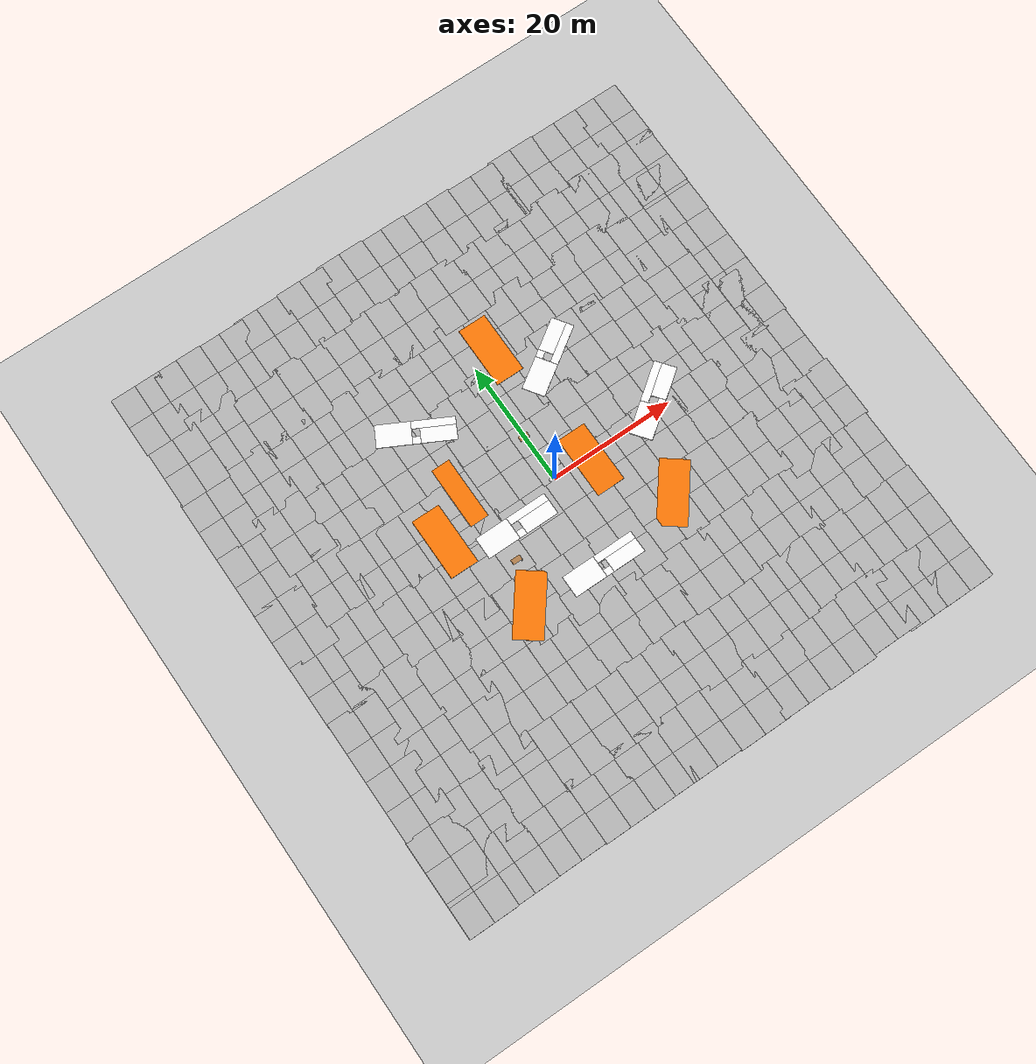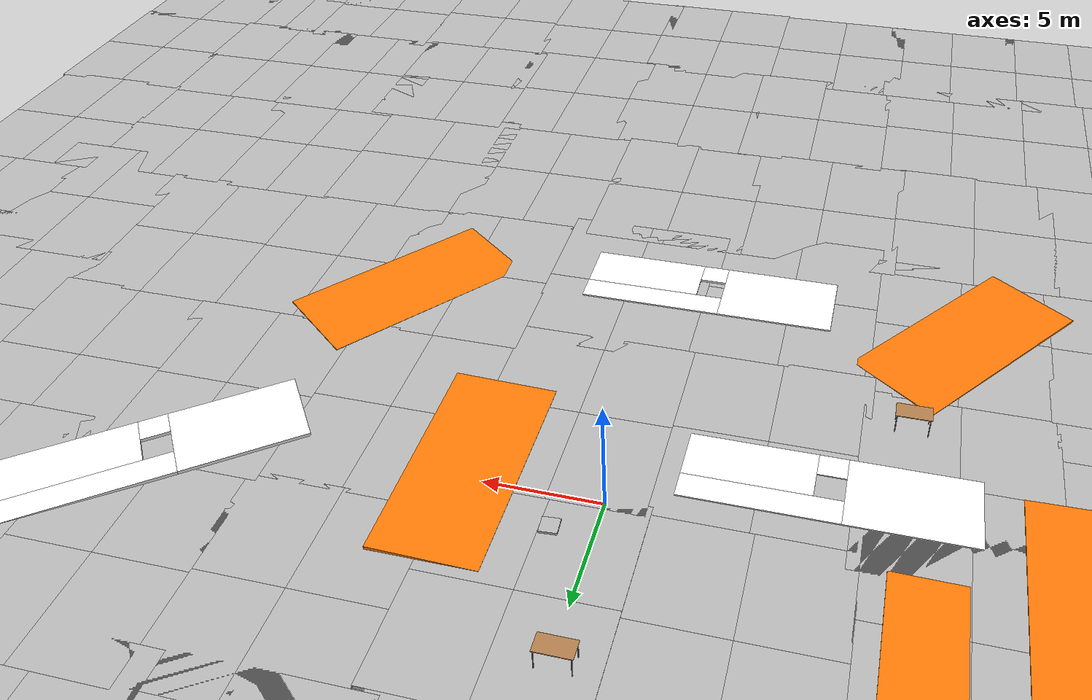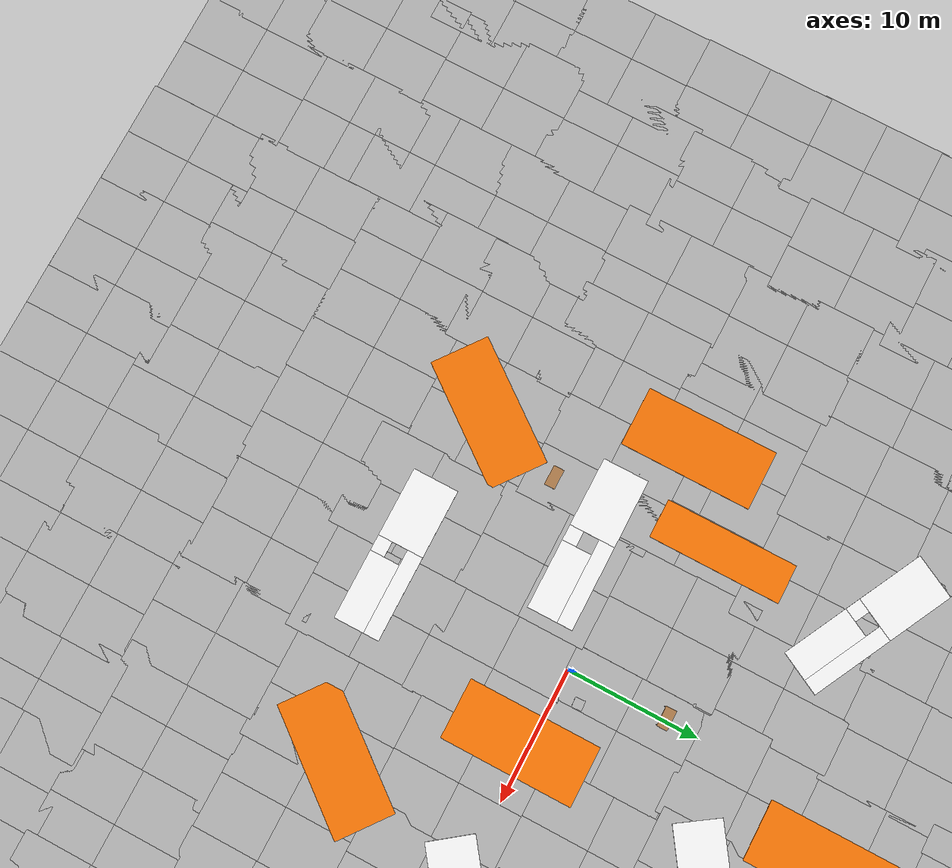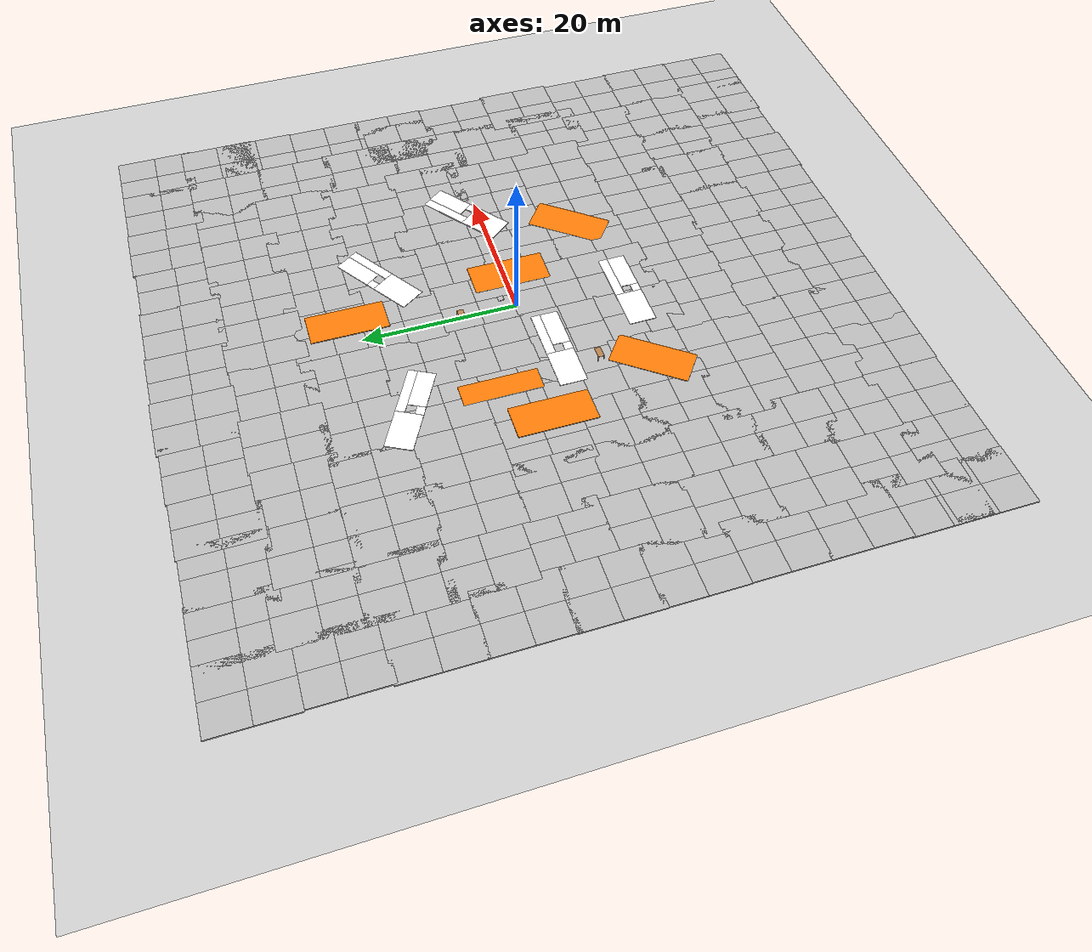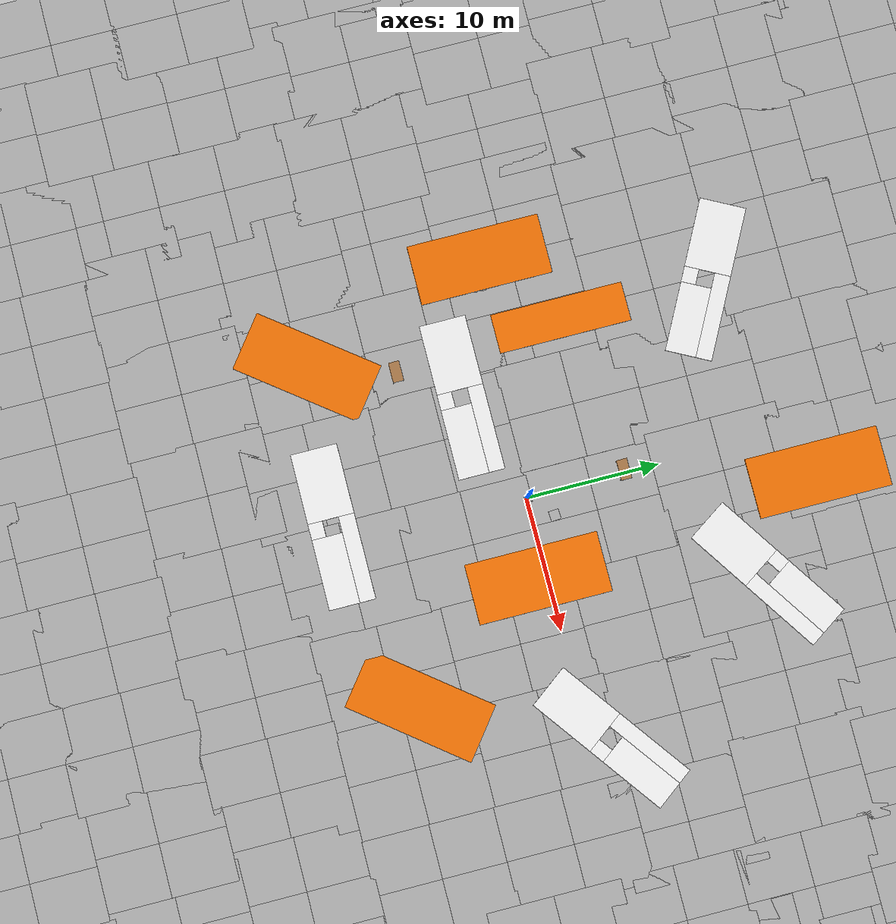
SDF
<sdf version="1.5">
 <world name="default">
  <light name="sun" type="directional">
   <pose>0 0 10 0 -0 0</pose>
   <diffuse>0.8 0.8 0.8 1</diffuse>
   <specular>0.1 0.1 0.1 1</specular>
   <attenuation>
    <range>1000</range>
    <constant>0.9</constant>
    <linear>0.01</linear>
    <quadratic>0.001</quadratic>
   </attenuation>
   <direction>-0.5 0.5 -1</direction>
  </light>
  <model name="ground_plane">
   <static>1</static>
   <link name="link">
    <collision name="collision">
     <geometry><plane><normal>0 0 1</normal><size>100 100</size></plane></geometry>
     <surface><friction><ode><mu>100</mu><mu2>50</mu2></ode></friction></surface>
    </collision>
    <visual name="visual">
     <cast_shadows>0</cast_shadows>
     <geometry><plane><normal>0 0 1</normal><size>100 100</size></plane></geometry>
     <material>
      <script><uri>file://media/materials/scripts/gazebo.material</uri><name>Gazebo/Grey</name></script>
     </material>
    </visual>
   </link>
  </model>
  <atmosphere type="adiabatic"/>
  <physics name="default_physics" default="0" type="ode">
   <max_step_size>0.001</max_step_size>
   <real_time_factor>1</real_time_factor>
   <real_time_update_rate>1000</real_time_update_rate>
   <gravity>0 0 -9.8</gravity>
   <magnetic_field>6e-06 2.3e-05 -4.2e-05</magnetic_field>
  </physics>
  <scene><ambient>0.4 0.4 0.4 1</ambient><background>0.7 0.7 0.7 1</background><shadows>1</shadows></scene>
  <spherical_coordinates>
   <surface_model>EARTH_WGS84</surface_model>
   <latitude_deg>0</latitude_deg>
   <longitude_deg>0</longitude_deg>
   <elevation>0</elevation>
   <heading_deg>0</heading_deg>
  </spherical_coordinates>
  <model name="mud_box">
   <static>1</static>
   <link name="link">
    <collision name="collision"><geometry><box><size>8 10 0.2</size></box></geometry></collision>
    <visual name="visual_1">
     <pose>-2 2.5 0 0 -0 0</pose>
     <cast_shadows>0</cast_shadows>
     <geometry><box><size>4 5 0.2</size></box></geometry>
     <material>
      <script>
       <uri>model://mud_box/materials/scripts</uri>
       <uri>model://mud_box/materials/textures</uri>
       <name>vrc/mud</name>
      </script>
     </material>
    </visual>
    <visual name="visual_2">
     <pose>2 2.5 0 0 -0 0</pose>
     <cast_shadows>0</cast_shadows>
     <geometry><box><size>4 5 0.2</size></box></geometry>
     <material>
      <script>
       <uri>model://mud_box/materials/scripts</uri>
       <uri>model://mud_box/materials/textures</uri>
       <name>vrc/mud</name>
      </script>
     </material>
    </visual>
    <visual name="visual_3">
     <pose>2 -2.5 0 0 -0 0</pose>
     <cast_shadows>0</cast_shadows>
     <geometry><box><size>4 5 0.2</size></box></geometry>
     <material>
      <script>
       <uri>model://mud_box/materials/scripts</uri>
       <uri>model://mud_box/materials/textures</uri>
       <name>vrc/mud</name>
      </script>
     </material>
    </visual>
    <visual name="visual_4">
     <pose>-2 -2.5 0 0 -0 0</pose>
     <cast_shadows>0</cast_shadows>
     <geometry><box><size>4 5 0.2</size></box></geometry>
     <material>
      <script>
       <uri>model://mud_box/materials/scripts</uri>
       <uri>model://mud_box/materials/textures</uri>
       <name>vrc/mud</name>
      </script>
     </material>
    </visual>
   </link>
   <pose>-5.68226 -4.79877 0 0 -0 0</pose>
  </model>
  <model name="mud_box_0">
   <static>1</static>
   <link name="link">
    <collision name="collision"><geometry><box><size>8 10 0.2</size></box></geometry></collision>
    <visual name="visual_1">
     <pose>-2 2.5 0 0 -0 0</pose>
     <cast_shadows>0</cast_shadows>
     <geometry><box><size>4 5 0.2</size></box></geometry>
     <material>
      <script>
       <uri>model://mud_box/materials/scripts</uri>
       <uri>model://mud_box/materials/textures</uri>
       <name>vrc/mud</name>
      </script>
     </material>
    </visual>
    <visual name="visual_2">
     <pose>2 2.5 0 0 -0 0</pose>
     <cast_shadows>0</cast_shadows>
     <geometry><box><size>4 5 0.2</size></box></geometry>
     <material>
      <script>
       <uri>model://mud_box/materials/scripts</uri>
       <uri>model://mud_box/materials/textures</uri>
       <name>vrc/mud</name>
      </script>
     </material>
    </visual>
    <visual name="visual_3">
     <pose>2 -2.5 0 0 -0 0</pose>
     <cast_shadows>0</cast_shadows>
     <geometry><box><size>4 5 0.2</size></box></geometry>
     <material>
      <script>
       <uri>model://mud_box/materials/scripts</uri>
       <uri>model://mud_box/materials/textures</uri>
       <name>vrc/mud</name>
      </script>
     </material>
    </visual>
    <visual name="visual_4">
     <pose>-2 -2.5 0 0 -0 0</pose>
     <cast_shadows>0</cast_shadows>
     <geometry><box><size>4 5 0.2</size></box></geometry>
     <material>
      <script>
       <uri>model://mud_box/materials/scripts</uri>
       <uri>model://mud_box/materials/textures</uri>
       <name>vrc/mud</name>
      </script>
     </material>
    </visual>
   </link>
   <pose>-5.88818 5.07948 0 0 -0 0</pose>
  </model>
  <model name="mud_box_1">
   <static>1</static>
   <link name="link">
    <collision name="collision"><geometry><box><size>8 10 0.2</size></box></geometry></collision>
    <visual name="visual_1">
     <pose>-2 2.5 0 0 -0 0</pose>
     <cast_shadows>0</cast_shadows>
     <geometry><box><size>4 5 0.2</size></box></geometry>
     <material>
      <script>
       <uri>model://mud_box/materials/scripts</uri>
       <uri>model://mud_box/materials/textures</uri>
       <name>vrc/mud</name>
      </script>
     </material>
    </visual>
    <visual name="visual_2">
     <pose>2 2.5 0 0 -0 0</pose>
     <cast_shadows>0</cast_shadows>
     <geometry><box><size>4 5 0.2</size></box></geometry>
     <material>
      <script>
       <uri>model://mud_box/materials/scripts</uri>
       <uri>model://mud_box/materials/textures</uri>
       <name>vrc/mud</name>
      </script>
     </material>
    </visual>
    <visual name="visual_3">
     <pose>2 -2.5 0 0 -0 0</pose>
     <cast_shadows>0</cast_shadows>
     <geometry><box><size>4 5 0.2</size></box></geometry>
     <material>
      <script>
       <uri>model://mud_box/materials/scripts</uri>
       <uri>model://mud_box/materials/textures</uri>
       <name>vrc/mud</name>
      </script>
     </material>
    </visual>
    <visual name="visual_4">
     <pose>-2 -2.5 0 0 -0 0</pose>
     <cast_shadows>0</cast_shadows>
     <geometry><box><size>4 5 0.2</size></box></geometry>
     <material>
      <script>
       <uri>model://mud_box/materials/scripts</uri>
       <uri>model://mud_box/materials/textures</uri>
       <name>vrc/mud</name>
      </script>
     </material>
    </visual>
   </link>
   <pose>-5.37597 -14.6349 0 0 -0 0</pose>
  </model>
  <model name="mud_box_3">
   <static>1</static>
   <link name="link">
    <collision name="collision"><geometry><box><size>8 10 0.2</size></box></geometry></collision>
    <visual name="visual_1">
     <pose>-2 2.5 0 0 -0 0</pose>
     <cast_shadows>0</cast_shadows>
     <geometry><box><size>4 5 0.2</size></box></geometry>
     <material>
      <script>
       <uri>model://mud_box/materials/scripts</uri>
       <uri>model://mud_box/materials/textures</uri>
       <name>vrc/mud</name>
      </script>
     </material>
    </visual>
    <visual name="visual_2">
     <pose>2 2.5 0 0 -0 0</pose>
     <cast_shadows>0</cast_shadows>
     <geometry><box><size>4 5 0.2</size></box></geometry>
     <material>
      <script>
       <uri>model://mud_box/materials/scripts</uri>
       <uri>model://mud_box/materials/textures</uri>
       <name>vrc/mud</name>
      </script>
     </material>
    </visual>
    <visual name="visual_3">
     <pose>2 -2.5 0 0 -0 0</pose>
     <cast_shadows>0</cast_shadows>
     <geometry><box><size>4 5 0.2</size></box></geometry>
     <material>
      <script>
       <uri>model://mud_box/materials/scripts</uri>
       <uri>model://mud_box/materials/textures</uri>
       <name>vrc/mud</name>
      </script>
     </material>
    </visual>
    <visual name="visual_4">
     <pose>-2 -2.5 0 0 -0 0</pose>
     <cast_shadows>0</cast_shadows>
     <geometry><box><size>4 5 0.2</size></box></geometry>
     <material>
      <script>
       <uri>model://mud_box/materials/scripts</uri>
       <uri>model://mud_box/materials/textures</uri>
       <name>vrc/mud</name>
      </script>
     </material>
    </visual>
   </link>
   <pose>2.11529 4.79269 0 0 -0 0</pose>
  </model>
  <model name="mud_box_4">
   <static>1</static>
   <link name="link">
    <collision name="collision"><geometry><box><size>8 10 0.2</size></box></geometry></collision>
    <visual name="visual_1">
     <pose>-2 2.5 0 0 -0 0</pose>
     <cast_shadows>0</cast_shadows>
     <geometry><box><size>4 5 0.2</size></box></geometry>
     <material>
      <script>
       <uri>model://mud_box/materials/scripts</uri>
       <uri>model://mud_box/materials/textures</uri>
       <name>vrc/mud</name>
      </script>
     </material>
    </visual>
    <visual name="visual_2">
     <pose>2 2.5 0 0 -0 0</pose>
     <cast_shadows>0</cast_shadows>
     <geometry><box><size>4 5 0.2</size></box></geometry>
     <material>
      <script>
       <uri>model://mud_box/materials/scripts</uri>
       <uri>model://mud_box/materials/textures</uri>
       <name>vrc/mud</name>
      </script>
     </material>
    </visual>
    <visual name="visual_3">
     <pose>2 -2.5 0 0 -0 0</pose>
     <cast_shadows>0</cast_shadows>
     <geometry><box><size>4 5 0.2</size></box></geometry>
     <material>
      <script>
       <uri>model://mud_box/materials/scripts</uri>
       <uri>model://mud_box/materials/textures</uri>
       <name>vrc/mud</name>
      </script>
     </material>
    </visual>
    <visual name="visual_4">
     <pose>-2 -2.5 0 0 -0 0</pose>
     <cast_shadows>0</cast_shadows>
     <geometry><box><size>4 5 0.2</size></box></geometry>
     <material>
      <script>
       <uri>model://mud_box/materials/scripts</uri>
       <uri>model://mud_box/materials/textures</uri>
       <name>vrc/mud</name>
      </script>
     </material>
    </visual>
   </link>
   <pose>10.1818 -3.15087 0 0 -0 0</pose>
  </model>
  <model name="mud_box_5">
   <static>1</static>
   <link name="link">
    <collision name="collision"><geometry><box><size>8 10 0.2</size></box></geometry></collision>
    <visual name="visual_1">
     <pose>-2 2.5 0 0 -0 0</pose>
     <cast_shadows>0</cast_shadows>
     <geometry><box><size>4 5 0.2</size></box></geometry>
     <material>
      <script>
       <uri>model://mud_box/materials/scripts</uri>
       <uri>model://mud_box/materials/textures</uri>
       <name>vrc/mud</name>
      </script>
     </material>
    </visual>
    <visual name="visual_2">
     <pose>2 2.5 0 0 -0 0</pose>
     <cast_shadows>0</cast_shadows>
     <geometry><box><size>4 5 0.2</size></box></geometry>
     <material>
      <script>
       <uri>model://mud_box/materials/scripts</uri>
       <uri>model://mud_box/materials/textures</uri>
       <name>vrc/mud</name>
      </script>
     </material>
    </visual>
    <visual name="visual_3">
     <pose>2 -2.5 0 0 -0 0</pose>
     <cast_shadows>0</cast_shadows>
     <geometry><box><size>4 5 0.2</size></box></geometry>
     <material>
      <script>
       <uri>model://mud_box/materials/scripts</uri>
       <uri>model://mud_box/materials/textures</uri>
       <name>vrc/mud</name>
      </script>
     </material>
    </visual>
    <visual name="visual_4">
     <pose>-2 -2.5 0 0 -0 0</pose>
     <cast_shadows>0</cast_shadows>
     <geometry><box><size>4 5 0.2</size></box></geometry>
     <material>
      <script>
       <uri>model://mud_box/materials/scripts</uri>
       <uri>model://mud_box/materials/textures</uri>
       <name>vrc/mud</name>
      </script>
     </material>
    </visual>
   </link>
   <pose>10.0851 6.64151 0 0 -0 0</pose>
  </model>
  <model name="mud_box_6">
   <static>1</static>
   <link name="link">
    <collision name="collision"><geometry><box><size>8 10 0.2</size></box></geometry></collision>
    <visual name="visual_1">
     <pose>-2 2.5 0 0 -0 0</pose>
     <cast_shadows>0</cast_shadows>
     <geometry><box><size>4 5 0.2</size></box></geometry>
     <material>
      <script>
       <uri>model://mud_box/materials/scripts</uri>
       <uri>model://mud_box/materials/textures</uri>
       <name>vrc/mud</name>
      </script>
     </material>
    </visual>
    <visual name="visual_2">
     <pose>2 2.5 0 0 -0 0</pose>
     <cast_shadows>0</cast_shadows>
     <geometry><box><size>4 5 0.2</size></box></geometry>
     <material>
      <script>
       <uri>model://mud_box/materials/scripts</uri>
       <uri>model://mud_box/materials/textures</uri>
       <name>vrc/mud</name>
      </script>
     </material>
    </visual>
    <visual name="visual_3">
     <pose>2 -2.5 0 0 -0 0</pose>
     <cast_shadows>0</cast_shadows>
     <geometry><box><size>4 5 0.2</size></box></geometry>
     <material>
      <script>
       <uri>model://mud_box/materials/scripts</uri>
       <uri>model://mud_box/materials/textures</uri>
       <name>vrc/mud</name>
      </script>
     </material>
    </visual>
    <visual name="visual_4">
     <pose>-2 -2.5 0 0 -0 0</pose>
     <cast_shadows>0</cast_shadows>
     <geometry><box><size>4 5 0.2</size></box></geometry>
     <material>
      <script>
       <uri>model://mud_box/materials/scripts</uri>
       <uri>model://mud_box/materials/textures</uri>
       <name>vrc/mud</name>
      </script>
     </material>
    </visual>
   </link>
   <pose>10.2281 -13.0017 0 0 -0 0</pose>
  </model>
  <model name="mud_box_7">
   <static>1</static>
   <link name="link">
    <collision name="collision"><geometry><box><size>8 10 0.2</size></box></geometry></collision>
    <visual name="visual_1">
     <pose>-2 2.5 0 0 -0 0</pose>
     <cast_shadows>0</cast_shadows>
     <geometry><box><size>4 5 0.2</size></box></geometry>
     <material>
      <script>
       <uri>model://mud_box/materials/scripts</uri>
       <uri>model://mud_box/materials/textures</uri>
       <name>vrc/mud</name>
      </script>
     </material>
    </visual>
    <visual name="visual_2">
     <pose>2 2.5 0 0 -0 0</pose>
     <cast_shadows>0</cast_shadows>
     <geometry><box><size>4 5 0.2</size></box></geometry>
     <material>
      <script>
       <uri>model://mud_box/materials/scripts</uri>
       <uri>model://mud_box/materials/textures</uri>
       <name>vrc/mud</name>
      </script>
     </material>
    </visual>
    <visual name="visual_3">
     <pose>2 -2.5 0 0 -0 0</pose>
     <cast_shadows>0</cast_shadows>
     <geometry><box><size>4 5 0.2</size></box></geometry>
     <material>
      <script>
       <uri>model://mud_box/materials/scripts</uri>
       <uri>model://mud_box/materials/textures</uri>
       <name>vrc/mud</name>
      </script>
     </material>
    </visual>
    <visual name="visual_4">
     <pose>-2 -2.5 0 0 -0 0</pose>
     <cast_shadows>0</cast_shadows>
     <geometry><box><size>4 5 0.2</size></box></geometry>
     <material>
      <script>
       <uri>model://mud_box/materials/scripts</uri>
       <uri>model://mud_box/materials/textures</uri>
       <name>vrc/mud</name>
      </script>
     </material>
    </visual>
   </link>
   <pose>2.3022 -13.8279 0 0 -0 0</pose>
  </model>
  <model name="mud_box_8">
   <static>1</static>
   <link name="link">
    <collision name="collision"><geometry><box><size>8 10 0.2</size></box></geometry></collision>
    <visual name="visual_1">
     <pose>-2 2.5 0 0 -0 0</pose>
     <cast_shadows>0</cast_shadows>
     <geometry><box><size>4 5 0.2</size></box></geometry>
     <material>
      <script>
       <uri>model://mud_box/materials/scripts</uri>
       <uri>model://mud_box/materials/textures</uri>
       <name>vrc/mud</name>
      </script>
     </material>
    </visual>
    <visual name="visual_2">
     <pose>2 2.5 0 0 -0 0</pose>
     <cast_shadows>0</cast_shadows>
     <geometry><box><size>4 5 0.2</size></box></geometry>
     <material>
      <script>
       <uri>model://mud_box/materials/scripts</uri>
       <uri>model://mud_box/materials/textures</uri>
       <name>vrc/mud</name>
      </script>
     </material>
    </visual>
    <visual name="visual_3">
     <pose>2 -2.5 0 0 -0 0</pose>
     <cast_shadows>0</cast_shadows>
     <geometry><box><size>4 5 0.2</size></box></geometry>
     <material>
      <script>
       <uri>model://mud_box/materials/scripts</uri>
       <uri>model://mud_box/materials/textures</uri>
       <name>vrc/mud</name>
      </script>
     </material>
    </visual>
    <visual name="visual_4">
     <pose>-2 -2.5 0 0 -0 0</pose>
     <cast_shadows>0</cast_shadows>
     <geometry><box><size>4 5 0.2</size></box></geometry>
     <material>
      <script>
       <uri>model://mud_box/materials/scripts</uri>
       <uri>model://mud_box/materials/textures</uri>
       <name>vrc/mud</name>
      </script>
     </material>
    </visual>
   </link>
   <pose>2.3135 -4.65178 0 0 -0 0</pose>
  </model>
  <model name="mud_box_9">
   <static>1</static>
   <link name="link">
    <collision name="collision"><geometry><box><size>8 10 0.2</size></box></geometry></collision>
    <visual name="visual_1">
     <pose>-2 2.5 0 0 -0 0</pose>
     <cast_shadows>0</cast_shadows>
     <geometry><box><size>4 5 0.2</size></box></geometry>
     <material>
      <script>
       <uri>model://mud_box/materials/scripts</uri>
       <uri>model://mud_box/materials/textures</uri>
       <name>vrc/mud</name>
      </script>
     </material>
    </visual>
    <visual name="visual_2">
     <pose>2 2.5 0 0 -0 0</pose>
     <cast_shadows>0</cast_shadows>
     <geometry><box><size>4 5 0.2</size></box></geometry>
     <material>
      <script>
       <uri>model://mud_box/materials/scripts</uri>
       <uri>model://mud_box/materials/textures</uri>
       <name>vrc/mud</name>
      </script>
     </material>
    </visual>
    <visual name="visual_3">
     <pose>2 -2.5 0 0 -0 0</pose>
     <cast_shadows>0</cast_shadows>
     <geometry><box><size>4 5 0.2</size></box></geometry>
     <material>
      <script>
       <uri>model://mud_box/materials/scripts</uri>
       <uri>model://mud_box/materials/textures</uri>
       <name>vrc/mud</name>
      </script>
     </material>
    </visual>
    <visual name="visual_4">
     <pose>-2 -2.5 0 0 -0 0</pose>
     <cast_shadows>0</cast_shadows>
     <geometry><box><size>4 5 0.2</size></box></geometry>
     <material>
      <script>
       <uri>model://mud_box/materials/scripts</uri>
       <uri>model://mud_box/materials/textures</uri>
       <name>vrc/mud</name>
      </script>
     </material>
    </visual>
   </link>
   <pose>-13.1885 -13.7453 0 0 -0 0</pose>
  </model>
  <model name="mud_box_10">
   <static>1</static>
   <link name="link">
    <collision name="collision"><geometry><box><size>8 10 0.2</size></box></geometry></collision>
    <visual name="visual_1">
     <pose>-2 2.5 0 0 -0 0</pose>
     <cast_shadows>0</cast_shadows>
     <geometry><box><size>4 5 0.2</size></box></geometry>
     <material>
      <script>
       <uri>model://mud_box/materials/scripts</uri>
       <uri>model://mud_box/materials/textures</uri>
       <name>vrc/mud</name>
      </script>
     </material>
    </visual>
    <visual name="visual_2">
     <pose>2 2.5 0 0 -0 0</pose>
     <cast_shadows>0</cast_shadows>
     <geometry><box><size>4 5 0.2</size></box></geometry>
     <material>
      <script>
       <uri>model://mud_box/materials/scripts</uri>
       <uri>model://mud_box/materials/textures</uri>
       <name>vrc/mud</name>
      </script>
     </material>
    </visual>
    <visual name="visual_3">
     <pose>2 -2.5 0 0 -0 0</pose>
     <cast_shadows>0</cast_shadows>
     <geometry><box><size>4 5 0.2</size></box></geometry>
     <material>
      <script>
       <uri>model://mud_box/materials/scripts</uri>
       <uri>model://mud_box/materials/textures</uri>
       <name>vrc/mud</name>
      </script>
     </material>
    </visual>
    <visual name="visual_4">
     <pose>-2 -2.5 0 0 -0 0</pose>
     <cast_shadows>0</cast_shadows>
     <geometry><box><size>4 5 0.2</size></box></geometry>
     <material>
      <script>
       <uri>model://mud_box/materials/scripts</uri>
       <uri>model://mud_box/materials/textures</uri>
       <name>vrc/mud</name>
      </script>
     </material>
    </visual>
   </link>
   <pose>-13.3232 -3.93027 0 0 -0 0</pose>
  </model>
  <model name="mud_box_11">
   <static>1</static>
   <link name="link">
    <collision name="collision"><geometry><box><size>8 10 0.2</size></box></geometry></collision>
    <visual name="visual_1">
     <pose>-2 2.5 0 0 -0 0</pose>
     <cast_shadows>0</cast_shadows>
     <geometry><box><size>4 5 0.2</size></box></geometry>
     <material>
      <script>
       <uri>model://mud_box/materials/scripts</uri>
       <uri>model://mud_box/materials/textures</uri>
       <name>vrc/mud</name>
      </script>
     </material>
    </visual>
    <visual name="visual_2">
     <pose>2 2.5 0 0 -0 0</pose>
     <cast_shadows>0</cast_shadows>
     <geometry><box><size>4 5 0.2</size></box></geometry>
     <material>
      <script>
       <uri>model://mud_box/materials/scripts</uri>
       <uri>model://mud_box/materials/textures</uri>
       <name>vrc/mud</name>
      </script>
     </material>
    </visual>
    <visual name="visual_3">
     <pose>2 -2.5 0 0 -0 0</pose>
     <cast_shadows>0</cast_shadows>
     <geometry><box><size>4 5 0.2</size></box></geometry>
     <material>
      <script>
       <uri>model://mud_box/materials/scripts</uri>
       <uri>model://mud_box/materials/textures</uri>
       <name>vrc/mud</name>
      </script>
     </material>
    </visual>
    <visual name="visual_4">
     <pose>-2 -2.5 0 0 -0 0</pose>
     <cast_shadows>0</cast_shadows>
     <geometry><box><size>4 5 0.2</size></box></geometry>
     <material>
      <script>
       <uri>model://mud_box/materials/scripts</uri>
       <uri>model://mud_box/materials/textures</uri>
       <name>vrc/mud</name>
      </script>
     </material>
    </visual>
   </link>
   <pose>-13.8399 3.21916 0 0 -0 0</pose>
  </model>
  <model name="mud_box_12">
   <static>1</static>
   <link name="link">
    <collision name="collision"><geometry><box><size>8 10 0.2</size></box></geometry></collision>
    <visual name="visual_1">
     <pose>-2 2.5 0 0 -0 0</pose>
     <cast_shadows>0</cast_shadows>
     <geometry><box><size>4 5 0.2</size></box></geometry>
     <material>
      <script>
       <uri>model://mud_box/materials/scripts</uri>
       <uri>model://mud_box/materials/textures</uri>
       <name>vrc/mud</name>
      </script>
     </material>
    </visual>
    <visual name="visual_2">
     <pose>2 2.5 0 0 -0 0</pose>
     <cast_shadows>0</cast_shadows>
     <geometry><box><size>4 5 0.2</size></box></geometry>
     <material>
      <script>
       <uri>model://mud_box/materials/scripts</uri>
       <uri>model://mud_box/materials/textures</uri>
       <name>vrc/mud</name>
      </script>
     </material>
    </visual>
    <visual name="visual_3">
     <pose>2 -2.5 0 0 -0 0</pose>
     <cast_shadows>0</cast_shadows>
     <geometry><box><size>4 5 0.2</size></box></geometry>
     <material>
      <script>
       <uri>model://mud_box/materials/scripts</uri>
       <uri>model://mud_box/materials/textures</uri>
       <name>vrc/mud</name>
      </script>
     </material>
    </visual>
    <visual name="visual_4">
     <pose>-2 -2.5 0 0 -0 0</pose>
     <cast_shadows>0</cast_shadows>
     <geometry><box><size>4 5 0.2</size></box></geometry>
     <material>
      <script>
       <uri>model://mud_box/materials/scripts</uri>
       <uri>model://mud_box/materials/textures</uri>
       <name>vrc/mud</name>
      </script>
     </material>
    </visual>
   </link>
   <pose>9.03571 14.9161 0 0 -0 0</pose>
  </model>
  <model name="mud_box_13">
   <static>1</static>
   <link name="link">
    <collision name="collision"><geometry><box><size>8 10 0.2</size></box></geometry></collision>
    <visual name="visual_1">
     <pose>-2 2.5 0 0 -0 0</pose>
     <cast_shadows>0</cast_shadows>
     <geometry><box><size>4 5 0.2</size></box></geometry>
     <material>
      <script>
       <uri>model://mud_box/materials/scripts</uri>
       <uri>model://mud_box/materials/textures</uri>
       <name>vrc/mud</name>
      </script>
     </material>
    </visual>
    <visual name="visual_2">
     <pose>2 2.5 0 0 -0 0</pose>
     <cast_shadows>0</cast_shadows>
     <geometry><box><size>4 5 0.2</size></box></geometry>
     <material>
      <script>
       <uri>model://mud_box/materials/scripts</uri>
       <uri>model://mud_box/materials/textures</uri>
       <name>vrc/mud</name>
      </script>
     </material>
    </visual>
    <visual name="visual_3">
     <pose>2 -2.5 0 0 -0 0</pose>
     <cast_shadows>0</cast_shadows>
     <geometry><box><size>4 5 0.2</size></box></geometry>
     <material>
      <script>
       <uri>model://mud_box/materials/scripts</uri>
       <uri>model://mud_box/materials/textures</uri>
       <name>vrc/mud</name>
      </script>
     </material>
    </visual>
    <visual name="visual_4">
     <pose>-2 -2.5 0 0 -0 0</pose>
     <cast_shadows>0</cast_shadows>
     <geometry><box><size>4 5 0.2</size></box></geometry>
     <material>
      <script>
       <uri>model://mud_box/materials/scripts</uri>
       <uri>model://mud_box/materials/textures</uri>
       <name>vrc/mud</name>
      </script>
     </material>
    </visual>
   </link>
   <pose>1.62983 14.5106 0 0 -0 0</pose>
  </model>
  <model name="mud_box_14">
   <static>1</static>
   <link name="link">
    <collision name="collision"><geometry><box><size>8 10 0.2</size></box></geometry></collision>
    <visual name="visual_1">
     <pose>-2 2.5 0 0 -0 0</pose>
     <cast_shadows>0</cast_shadows>
     <geometry><box><size>4 5 0.2</size></box></geometry>
     <material>
      <script>
       <uri>model://mud_box/materials/scripts</uri>
       <uri>model://mud_box/materials/textures</uri>
       <name>vrc/mud</name>
      </script>
     </material>
    </visual>
    <visual name="visual_2">
     <pose>2 2.5 0 0 -0 0</pose>
     <cast_shadows>0</cast_shadows>
     <geometry><box><size>4 5 0.2</size></box></geometry>
     <material>
      <script>
       <uri>model://mud_box/materials/scripts</uri>
       <uri>model://mud_box/materials/textures</uri>
       <name>vrc/mud</name>
      </script>
     </material>
    </visual>
    <visual name="visual_3">
     <pose>2 -2.5 0 0 -0 0</pose>
     <cast_shadows>0</cast_shadows>
     <geometry><box><size>4 5 0.2</size></box></geometry>
     <material>
      <script>
       <uri>model://mud_box/materials/scripts</uri>
       <uri>model://mud_box/materials/textures</uri>
       <name>vrc/mud</name>
      </script>
     </material>
    </visual>
    <visual name="visual_4">
     <pose>-2 -2.5 0 0 -0 0</pose>
     <cast_shadows>0</cast_shadows>
     <geometry><box><size>4 5 0.2</size></box></geometry>
     <material>
      <script>
       <uri>model://mud_box/materials/scripts</uri>
       <uri>model://mud_box/materials/textures</uri>
       <name>vrc/mud</name>
      </script>
     </material>
    </visual>
   </link>
   <pose>-5.79195 13.6955 0 0 -0 0</pose>
  </model>
  <model name="mud_box_15">
   <static>1</static>
   <link name="link">
    <collision name="collision"><geometry><box><size>8 10 0.2</size></box></geometry></collision>
    <visual name="visual_1">
     <pose>-2 2.5 0 0 -0 0</pose>
     <cast_shadows>0</cast_shadows>
     <geometry><box><size>4 5 0.2</size></box></geometry>
     <material>
      <script>
       <uri>model://mud_box/materials/scripts</uri>
       <uri>model://mud_box/materials/textures</uri>
       <name>vrc/mud</name>
      </script>
     </material>
    </visual>
    <visual name="visual_2">
     <pose>2 2.5 0 0 -0 0</pose>
     <cast_shadows>0</cast_shadows>
     <geometry><box><size>4 5 0.2</size></box></geometry>
     <material>
      <script>
       <uri>model://mud_box/materials/scripts</uri>
       <uri>model://mud_box/materials/textures</uri>
       <name>vrc/mud</name>
      </script>
     </material>
    </visual>
    <visual name="visual_3">
     <pose>2 -2.5 0 0 -0 0</pose>
     <cast_shadows>0</cast_shadows>
     <geometry><box><size>4 5 0.2</size></box></geometry>
     <material>
      <script>
       <uri>model://mud_box/materials/scripts</uri>
       <uri>model://mud_box/materials/textures</uri>
       <name>vrc/mud</name>
      </script>
     </material>
    </visual>
    <visual name="visual_4">
     <pose>-2 -2.5 0 0 -0 0</pose>
     <cast_shadows>0</cast_shadows>
     <geometry><box><size>4 5 0.2</size></box></geometry>
     <material>
      <script>
       <uri>model://mud_box/materials/scripts</uri>
       <uri>model://mud_box/materials/textures</uri>
       <name>vrc/mud</name>
      </script>
     </material>
    </visual>
   </link>
   <pose>-12.6627 13.0185 0 0 -0 0</pose>
  </model>
  <model name="window2">
   <pose>-1.52133 -12.523 0.093793 1.55967 -0 0</pose>
   <link name="Wall_0">
    <visual name="Wall_0_Visual_0">
     <pose>-3.2425 0 1.75 0 -0 0</pose>
     <geometry><box><size>5.265 0.15 3.5</size></box></geometry>
     <material>
      <script>
       <uri>model://window_door/materials/scripts</uri>
       <uri>model://window_door/materials/textures</uri>
       <name>Wall/NiceWall</name>
      </script>
      <ambient>1 1 1 1</ambient>
     </material>
    </visual>
    <collision name="Wall_0_Collision_0">
     <geometry><box><size>5.265 0.15 3.5</size></box></geometry>
     <pose>-3.2425 0 1.75 0 -0 0</pose>
    </collision>
    <visual name="Wall_0_Visual_1">
     <pose>2.6325 0 0.6 0 -0 0</pose>
     <geometry><box><size>6.485 0.15 1.2</size></box></geometry>
     <material>
      <script>
       <uri>model://window_door/materials/scripts</uri>
       <uri>model://window_door/materials/textures</uri>
       <name>Wall/NiceWall</name>
      </script>
      <ambient>1 1 1 1</ambient>
     </material>
    </visual>
    <collision name="Wall_0_Collision_1">
     <geometry><box><size>6.485 0.15 1.2</size></box></geometry>
     <pose>2.6325 0 0.6 0 -0 0</pose>
    </collision>
    <visual name="Wall_0_Visual_2">
     <pose>3.2325 0 2.35 0 -0 0</pose>
     <geometry><box><size>5.285 0.15 2.3</size></box></geometry>
     <material>
      <script>
       <uri>model://window_door/materials/scripts</uri>
       <uri>model://window_door/materials/textures</uri>
       <name>Wall/NiceWall</name>
      </script>
      <ambient>1 1 1 1</ambient>
     </material>
    </visual>
    <collision name="Wall_0_Collision_2">
     <geometry><box><size>5.285 0.15 2.3</size></box></geometry>
     <pose>3.2325 0 2.35 0 -0 0</pose>
    </collision>
    <visual name="Wall_0_Visual_3">
     <pose>-0.01 0 2.95 0 -0 0</pose>
     <geometry><box><size>1.2 0.15 1.1</size></box></geometry>
     <material>
      <script>
       <uri>model://window_door/materials/scripts</uri>
       <uri>model://window_door/materials/textures</uri>
       <name>Wall/NiceWall</name>
      </script>
      <ambient>1 1 1 1</ambient>
     </material>
    </visual>
    <collision name="Wall_0_Collision_3">
     <geometry><box><size>1.2 0.15 1.1</size></box></geometry>
     <pose>-0.01 0 2.95 0 -0 0</pose>
    </collision>
   </link>
   <static>1</static>
  </model>
  <model name="window2_0">
   <pose>-8.39086 -0.992257 0.080248 1.57646 -0 0</pose>
   <link name="Wall_0">
    <visual name="Wall_0_Visual_0">
     <pose>-3.2425 0 1.75 0 -0 0</pose>
     <geometry><box><size>5.265 0.15 3.5</size></box></geometry>
     <material>
      <script>
       <uri>model://window_door/materials/scripts</uri>
       <uri>model://window_door/materials/textures</uri>
       <name>Wall/NiceWall</name>
      </script>
      <ambient>1 1 1 1</ambient>
     </material>
    </visual>
    <collision name="Wall_0_Collision_0">
     <geometry><box><size>5.265 0.15 3.5</size></box></geometry>
     <pose>-3.2425 0 1.75 0 -0 0</pose>
    </collision>
    <visual name="Wall_0_Visual_1">
     <pose>2.6325 0 0.6 0 -0 0</pose>
     <geometry><box><size>6.485 0.15 1.2</size></box></geometry>
     <material>
      <script>
       <uri>model://window_door/materials/scripts</uri>
       <uri>model://window_door/materials/textures</uri>
       <name>Wall/NiceWall</name>
      </script>
      <ambient>1 1 1 1</ambient>
     </material>
    </visual>
    <collision name="Wall_0_Collision_1">
     <geometry><box><size>6.485 0.15 1.2</size></box></geometry>
     <pose>2.6325 0 0.6 0 -0 0</pose>
    </collision>
    <visual name="Wall_0_Visual_2">
     <pose>3.2325 0 2.35 0 -0 0</pose>
     <geometry><box><size>5.285 0.15 2.3</size></box></geometry>
     <material>
      <script>
       <uri>model://window_door/materials/scripts</uri>
       <uri>model://window_door/materials/textures</uri>
       <name>Wall/NiceWall</name>
      </script>
      <ambient>1 1 1 1</ambient>
     </material>
    </visual>
    <collision name="Wall_0_Collision_2">
     <geometry><box><size>5.285 0.15 2.3</size></box></geometry>
     <pose>3.2325 0 2.35 0 -0 0</pose>
    </collision>
    <visual name="Wall_0_Visual_3">
     <pose>-0.01 0 2.95 0 -0 0</pose>
     <geometry><box><size>1.2 0.15 1.1</size></box></geometry>
     <material>
      <script>
       <uri>model://window_door/materials/scripts</uri>
       <uri>model://window_door/materials/textures</uri>
       <name>Wall/NiceWall</name>
      </script>
      <ambient>1 1 1 1</ambient>
     </material>
    </visual>
    <collision name="Wall_0_Collision_3">
     <geometry><box><size>1.2 0.15 1.1</size></box></geometry>
     <pose>-0.01 0 2.95 0 -0 0</pose>
    </collision>
   </link>
   <static>1</static>
  </model>
  <model name="window2_1">
   <pose>10.7008 14.1735 0.086177 -1.57506 0.00287 0.592291</pose>
   <link name="Wall_0">
    <visual name="Wall_0_Visual_0">
     <pose>-3.2425 0 1.75 0 -0 0</pose>
     <geometry><box><size>5.265 0.15 3.5</size></box></geometry>
     <material>
      <script>
       <uri>model://window_door/materials/scripts</uri>
       <uri>model://window_door/materials/textures</uri>
       <name>Wall/NiceWall</name>
      </script>
      <ambient>1 1 1 1</ambient>
     </material>
    </visual>
    <collision name="Wall_0_Collision_0">
     <geometry><box><size>5.265 0.15 3.5</size></box></geometry>
     <pose>-3.2425 0 1.75 0 -0 0</pose>
    </collision>
    <visual name="Wall_0_Visual_1">
     <pose>2.6325 0 0.6 0 -0 0</pose>
     <geometry><box><size>6.485 0.15 1.2</size></box></geometry>
     <material>
      <script>
       <uri>model://window_door/materials/scripts</uri>
       <uri>model://window_door/materials/textures</uri>
       <name>Wall/NiceWall</name>
      </script>
      <ambient>1 1 1 1</ambient>
     </material>
    </visual>
    <collision name="Wall_0_Collision_1">
     <geometry><box><size>6.485 0.15 1.2</size></box></geometry>
     <pose>2.6325 0 0.6 0 -0 0</pose>
    </collision>
    <visual name="Wall_0_Visual_2">
     <pose>3.2325 0 2.35 0 -0 0</pose>
     <geometry><box><size>5.285 0.15 2.3</size></box></geometry>
     <material>
      <script>
       <uri>model://window_door/materials/scripts</uri>
       <uri>model://window_door/materials/textures</uri>
       <name>Wall/NiceWall</name>
      </script>
      <ambient>1 1 1 1</ambient>
     </material>
    </visual>
    <collision name="Wall_0_Collision_2">
     <geometry><box><size>5.285 0.15 2.3</size></box></geometry>
     <pose>3.2325 0 2.35 0 -0 0</pose>
    </collision>
    <visual name="Wall_0_Visual_3">
     <pose>-0.01 0 2.95 0 -0 0</pose>
     <geometry><box><size>1.2 0.15 1.1</size></box></geometry>
     <material>
      <script>
       <uri>model://window_door/materials/scripts</uri>
       <uri>model://window_door/materials/textures</uri>
       <name>Wall/NiceWall</name>
      </script>
      <ambient>1 1 1 1</ambient>
     </material>
    </visual>
    <collision name="Wall_0_Collision_3">
     <geometry><box><size>1.2 0.15 1.1</size></box></geometry>
     <pose>-0.01 0 2.95 0 -0 0</pose>
    </collision>
   </link>
   <static>1</static>
  </model>
  <model name="wall">
   <pose>-15.3228 5.82852 0 -2e-05 1.55454 -2.4e-05</pose>
   <link name="Wall_0">
    <collision name="Wall_0_Collision">
     <geometry><box><size>10 0.15 4.5</size></box></geometry>
     <pose>0 0 2.25 0 -0 0</pose>
    </collision>
    <visual name="Wall_0_Visual">
     <pose>0 0 2.25 0 -0 0</pose>
     <geometry><box><size>10 0.15 4.5</size></box></geometry>
     <material>
      <script>
       <uri>model://wall/materials/scripts</uri>
       <uri>model://wall/materials/textures</uri>
       <name>Wall/NiceWall</name>
      </script>
      <ambient>0.996078 0.47451 0.0196078 1</ambient>
     </material>
    </visual>
    <pose>0 -0 0 0 0 -1.5708</pose>
   </link>
   <static>1</static>
  </model>
  <model name="wall_0">
   <pose>8.10955 -0.669266 0.170192 3.14158 -1.54059 -3.14159</pose>
   <link name="Wall_0">
    <collision name="Wall_0_Collision">
     <geometry><box><size>10 0.15 4.5</size></box></geometry>
     <pose>0 0 2.25 0 -0 0</pose>
    </collision>
    <visual name="Wall_0_Visual">
     <pose>0 0 2.25 0 -0 0</pose>
     <geometry><box><size>10 0.15 4.5</size></box></geometry>
     <material>
      <script>
       <uri>model://wall/materials/scripts</uri>
       <uri>model://wall/materials/textures</uri>
       <name>Wall/NiceWall</name>
      </script>
      <ambient>0.996078 0.47451 0.0196078 1</ambient>
     </material>
    </visual>
    <pose>0 -0 0 0 0 -1.5708</pose>
   </link>
   <static>1</static>
  </model>
  <model name="wall_1">
   <pose>-11.618 -14.6108 0.054009 -0.653823 -1.56052 7.4e-05</pose>
   <link name="Wall_0">
    <collision name="Wall_0_Collision">
     <geometry><box><size>10 0.15 4.5</size></box></geometry>
     <pose>0 0 2.25 0 -0 0</pose>
    </collision>
    <visual name="Wall_0_Visual">
     <pose>0 0 2.25 0 -0 0</pose>
     <geometry><box><size>10 0.15 4.5</size></box></geometry>
     <material>
      <script>
       <uri>model://wall/materials/scripts</uri>
       <uri>model://wall/materials/textures</uri>
       <name>Wall/NiceWall</name>
      </script>
      <ambient>0.996078 0.47451 0.0196078 1</ambient>
     </material>
    </visual>
    <pose>0 -0 0 0 0 -1.5708</pose>
   </link>
   <static>1</static>
  </model>
  <model name="wall_2">
   <pose>14.4557 -12.7036 0.049201 2.47818 -1.56676 -3.14083</pose>
   <link name="Wall_0">
    <collision name="Wall_0_Collision">
     <geometry><box><size>10 0.15 4.5</size></box></geometry>
     <pose>0 0 2.25 0 -0 0</pose>
    </collision>
    <visual name="Wall_0_Visual">
     <pose>0 0 2.25 0 -0 0</pose>
     <geometry><box><size>10 0.15 4.5</size></box></geometry>
     <material>
      <script>
       <uri>model://wall/materials/scripts</uri>
       <uri>model://wall/materials/textures</uri>
       <name>Wall/NiceWall</name>
      </script>
      <ambient>0.996078 0.47451 0.0196078 1</ambient>
     </material>
    </visual>
    <pose>0 -0 0 0 0 -1.5708</pose>
   </link>
   <static>1</static>
  </model>
  <model name="table">
   <static>1</static>
   <link name="link">
    <collision name="surface">
     <pose>0 0 1 0 -0 0</pose>
     <geometry><box><size>1.5 0.8 0.03</size></box></geometry>
     <surface><friction><ode><mu>0.6</mu><mu2>0.6</mu2></ode></friction></surface>
    </collision>
    <visual name="visual1">
     <pose>0 0 1 0 -0 0</pose>
     <geometry><box><size>1.5 0.8 0.03</size></box></geometry>
     <material>
      <script><uri>file://media/materials/scripts/gazebo.material</uri><name>Gazebo/Wood</name></script>
     </material>
    </visual>
    <collision name="front_left_leg">
     <pose>0.68 0.38 0.5 0 -0 0</pose>
     <geometry><cylinder><radius>0.02</radius><length>1</length></cylinder></geometry>
    </collision>
    <visual name="front_left_leg">
     <pose>0.68 0.38 0.5 0 -0 0</pose>
     <geometry><cylinder><radius>0.02</radius><length>1</length></cylinder></geometry>
     <material>
      <script><uri>file://media/materials/scripts/gazebo.material</uri><name>Gazebo/Grey</name></script>
     </material>
    </visual>
    <collision name="front_right_leg">
     <pose>0.68 -0.38 0.5 0 -0 0</pose>
     <geometry><cylinder><radius>0.02</radius><length>1</length></cylinder></geometry>
    </collision>
    <visual name="front_right_leg">
     <pose>0.68 -0.38 0.5 0 -0 0</pose>
     <geometry><cylinder><radius>0.02</radius><length>1</length></cylinder></geometry>
     <material>
      <script><uri>file://media/materials/scripts/gazebo.material</uri><name>Gazebo/Grey</name></script>
     </material>
    </visual>
    <collision name="back_right_leg">
     <pose>-0.68 -0.38 0.5 0 -0 0</pose>
     <geometry><cylinder><radius>0.02</radius><length>1</length></cylinder></geometry>
    </collision>
    <visual name="back_right_leg">
     <pose>-0.68 -0.38 0.5 0 -0 0</pose>
     <geometry><cylinder><radius>0.02</radius><length>1</length></cylinder></geometry>
     <material>
      <script><uri>file://media/materials/scripts/gazebo.material</uri><name>Gazebo/Grey</name></script>
     </material>
    </visual>
    <collision name="back_left_leg">
     <pose>-0.68 0.38 0.5 0 -0 0</pose>
     <geometry><cylinder><radius>0.02</radius><length>1</length></cylinder></geometry>
    </collision>
    <visual name="back_left_leg">
     <pose>-0.68 0.38 0.5 0 -0 0</pose>
     <geometry><cylinder><radius>0.02</radius><length>1</length></cylinder></geometry>
     <material>
      <script><uri>file://media/materials/scripts/gazebo.material</uri><name>Gazebo/Grey</name></script>
     </material>
    </visual>
   </link>
   <pose>-11.3262 -6.97566 0 0 -0 0</pose>
  </model>
  <model name="mud_box_2">
   <static>1</static>
   <link name="link">
    <collision name="collision"><geometry><box><size>8 10 0.2</size></box></geometry></collision>
    <visual name="visual_1">
     <pose>-2 2.5 0 0 -0 0</pose>
     <cast_shadows>0</cast_shadows>
     <geometry><box><size>4 5 0.2</size></box></geometry>
     <material>
      <script>
       <uri>model://mud_box/materials/scripts</uri>
       <uri>model://mud_box/materials/textures</uri>
       <name>vrc/mud</name>
      </script>
     </material>
    </visual>
    <visual name="visual_2">
     <pose>2 2.5 0 0 -0 0</pose>
     <cast_shadows>0</cast_shadows>
     <geometry><box><size>4 5 0.2</size></box></geometry>
     <material>
      <script>
       <uri>model://mud_box/materials/scripts</uri>
       <uri>model://mud_box/materials/textures</uri>
       <name>vrc/mud</name>
      </script>
     </material>
    </visual>
    <visual name="visual_3">
     <pose>2 -2.5 0 0 -0 0</pose>
     <cast_shadows>0</cast_shadows>
     <geometry><box><size>4 5 0.2</size></box></geometry>
     <material>
      <script>
       <uri>model://mud_box/materials/scripts</uri>
       <uri>model://mud_box/materials/textures</uri>
       <name>vrc/mud</name>
      </script>
     </material>
    </visual>
    <visual name="visual_4">
     <pose>-2 -2.5 0 0 -0 0</pose>
     <cast_shadows>0</cast_shadows>
     <geometry><box><size>4 5 0.2</size></box></geometry>
     <material>
      <script>
       <uri>model://mud_box/materials/scripts</uri>
       <uri>model://mud_box/materials/textures</uri>
       <name>vrc/mud</name>
      </script>
     </material>
    </visual>
   </link>
   <pose>-20.4385 12.9971 0 0 -0 0</pose>
  </model>
  <model name="mud_box_16">
   <static>1</static>
   <link name="link">
    <collision name="collision"><geometry><box><size>8 10 0.2</size></box></geometry></collision>
    <visual name="visual_1">
     <pose>-2 2.5 0 0 -0 0</pose>
     <cast_shadows>0</cast_shadows>
     <geometry><box><size>4 5 0.2</size></box></geometry>
     <material>
      <script>
       <uri>model://mud_box/materials/scripts</uri>
       <uri>model://mud_box/materials/textures</uri>
       <name>vrc/mud</name>
      </script>
     </material>
    </visual>
    <visual name="visual_2">
     <pose>2 2.5 0 0 -0 0</pose>
     <cast_shadows>0</cast_shadows>
     <geometry><box><size>4 5 0.2</size></box></geometry>
     <material>
      <script>
       <uri>model://mud_box/materials/scripts</uri>
       <uri>model://mud_box/materials/textures</uri>
       <name>vrc/mud</name>
      </script>
     </material>
    </visual>
    <visual name="visual_3">
     <pose>2 -2.5 0 0 -0 0</pose>
     <cast_shadows>0</cast_shadows>
     <geometry><box><size>4 5 0.2</size></box></geometry>
     <material>
      <script>
       <uri>model://mud_box/materials/scripts</uri>
       <uri>model://mud_box/materials/textures</uri>
       <name>vrc/mud</name>
      </script>
     </material>
    </visual>
    <visual name="visual_4">
     <pose>-2 -2.5 0 0 -0 0</pose>
     <cast_shadows>0</cast_shadows>
     <geometry><box><size>4 5 0.2</size></box></geometry>
     <material>
      <script>
       <uri>model://mud_box/materials/scripts</uri>
       <uri>model://mud_box/materials/textures</uri>
       <name>vrc/mud</name>
      </script>
     </material>
    </visual>
   </link>
   <pose>-21.3729 3.04393 0 0 -0 0</pose>
  </model>
  <model name="mud_box_17">
   <static>1</static>
   <link name="link">
    <collision name="collision"><geometry><box><size>8 10 0.2</size></box></geometry></collision>
    <visual name="visual_1">
     <pose>-2 2.5 0 0 -0 0</pose>
     <cast_shadows>0</cast_shadows>
     <geometry><box><size>4 5 0.2</size></box></geometry>
     <material>
      <script>
       <uri>model://mud_box/materials/scripts</uri>
       <uri>model://mud_box/materials/textures</uri>
       <name>vrc/mud</name>
      </script>
     </material>
    </visual>
    <visual name="visual_2">
     <pose>2 2.5 0 0 -0 0</pose>
     <cast_shadows>0</cast_shadows>
     <geometry><box><size>4 5 0.2</size></box></geometry>
     <material>
      <script>
       <uri>model://mud_box/materials/scripts</uri>
       <uri>model://mud_box/materials/textures</uri>
       <name>vrc/mud</name>
      </script>
     </material>
    </visual>
    <visual name="visual_3">
     <pose>2 -2.5 0 0 -0 0</pose>
     <cast_shadows>0</cast_shadows>
     <geometry><box><size>4 5 0.2</size></box></geometry>
     <material>
      <script>
       <uri>model://mud_box/materials/scripts</uri>
       <uri>model://mud_box/materials/textures</uri>
       <name>vrc/mud</name>
      </script>
     </material>
    </visual>
    <visual name="visual_4">
     <pose>-2 -2.5 0 0 -0 0</pose>
     <cast_shadows>0</cast_shadows>
     <geometry><box><size>4 5 0.2</size></box></geometry>
     <material>
      <script>
       <uri>model://mud_box/materials/scripts</uri>
       <uri>model://mud_box/materials/textures</uri>
       <name>vrc/mud</name>
      </script>
     </material>
    </visual>
   </link>
   <pose>-21.1882 -6.44237 0 0 -0 0</pose>
  </model>
  <model name="mud_box_18">
   <static>1</static>
   <link name="link">
    <collision name="collision"><geometry><box><size>8 10 0.2</size></box></geometry></collision>
    <visual name="visual_1">
     <pose>-2 2.5 0 0 -0 0</pose>
     <cast_shadows>0</cast_shadows>
     <geometry><box><size>4 5 0.2</size></box></geometry>
     <material>
      <script>
       <uri>model://mud_box/materials/scripts</uri>
       <uri>model://mud_box/materials/textures</uri>
       <name>vrc/mud</name>
      </script>
     </material>
    </visual>
    <visual name="visual_2">
     <pose>2 2.5 0 0 -0 0</pose>
     <cast_shadows>0</cast_shadows>
     <geometry><box><size>4 5 0.2</size></box></geometry>
     <material>
      <script>
       <uri>model://mud_box/materials/scripts</uri>
       <uri>model://mud_box/materials/textures</uri>
       <name>vrc/mud</name>
      </script>
     </material>
    </visual>
    <visual name="visual_3">
     <pose>2 -2.5 0 0 -0 0</pose>
     <cast_shadows>0</cast_shadows>
     <geometry><box><size>4 5 0.2</size></box></geometry>
     <material>
      <script>
       <uri>model://mud_box/materials/scripts</uri>
       <uri>model://mud_box/materials/textures</uri>
       <name>vrc/mud</name>
      </script>
     </material>
    </visual>
    <visual name="visual_4">
     <pose>-2 -2.5 0 0 -0 0</pose>
     <cast_shadows>0</cast_shadows>
     <geometry><box><size>4 5 0.2</size></box></geometry>
     <material>
      <script>
       <uri>model://mud_box/materials/scripts</uri>
       <uri>model://mud_box/materials/textures</uri>
       <name>vrc/mud</name>
      </script>
     </material>
    </visual>
   </link>
   <pose>-20.9947 -13.6813 0 0 -0 0</pose>
  </model>
  <model name="mud_box_19">
   <static>1</static>
   <link name="link">
    <collision name="collision"><geometry><box><size>8 10 0.2</size></box></geometry></collision>
    <visual name="visual_1">
     <pose>-2 2.5 0 0 -0 0</pose>
     <cast_shadows>0</cast_shadows>
     <geometry><box><size>4 5 0.2</size></box></geometry>
     <material>
      <script>
       <uri>model://mud_box/materials/scripts</uri>
       <uri>model://mud_box/materials/textures</uri>
       <name>vrc/mud</name>
      </script>
     </material>
    </visual>
    <visual name="visual_2">
     <pose>2 2.5 0 0 -0 0</pose>
     <cast_shadows>0</cast_shadows>
     <geometry><box><size>4 5 0.2</size></box></geometry>
     <material>
      <script>
       <uri>model://mud_box/materials/scripts</uri>
       <uri>model://mud_box/materials/textures</uri>
       <name>vrc/mud</name>
      </script>
     </material>
    </visual>
    <visual name="visual_3">
     <pose>2 -2.5 0 0 -0 0</pose>
     <cast_shadows>0</cast_shadows>
     <geometry><box><size>4 5 0.2</size></box></geometry>
     <material>
      <script>
       <uri>model://mud_box/materials/scripts</uri>
       <uri>model://mud_box/materials/textures</uri>
       <name>vrc/mud</name>
      </script>
     </material>
    </visual>
    <visual name="visual_4">
     <pose>-2 -2.5 0 0 -0 0</pose>
     <cast_shadows>0</cast_shadows>
     <geometry><box><size>4 5 0.2</size></box></geometry>
     <material>
      <script>
       <uri>model://mud_box/materials/scripts</uri>
       <uri>model://mud_box/materials/textures</uri>
       <name>vrc/mud</name>
      </script>
     </material>
    </visual>
   </link>
   <pose>17.056 -12.7839 0 0 -0 0</pose>
  </model>
  <model name="mud_box_20">
   <static>1</static>
   <link name="link">
    <collision name="collision"><geometry><box><size>8 10 0.2</size></box></geometry></collision>
    <visual name="visual_1">
     <pose>-2 2.5 0 0 -0 0</pose>
     <cast_shadows>0</cast_shadows>
     <geometry><box><size>4 5 0.2</size></box></geometry>
     <material>
      <script>
       <uri>model://mud_box/materials/scripts</uri>
       <uri>model://mud_box/materials/textures</uri>
       <name>vrc/mud</name>
      </script>
     </material>
    </visual>
    <visual name="visual_2">
     <pose>2 2.5 0 0 -0 0</pose>
     <cast_shadows>0</cast_shadows>
     <geometry><box><size>4 5 0.2</size></box></geometry>
     <material>
      <script>
       <uri>model://mud_box/materials/scripts</uri>
       <uri>model://mud_box/materials/textures</uri>
       <name>vrc/mud</name>
      </script>
     </material>
    </visual>
    <visual name="visual_3">
     <pose>2 -2.5 0 0 -0 0</pose>
     <cast_shadows>0</cast_shadows>
     <geometry><box><size>4 5 0.2</size></box></geometry>
     <material>
      <script>
       <uri>model://mud_box/materials/scripts</uri>
       <uri>model://mud_box/materials/textures</uri>
       <name>vrc/mud</name>
      </script>
     </material>
    </visual>
    <visual name="visual_4">
     <pose>-2 -2.5 0 0 -0 0</pose>
     <cast_shadows>0</cast_shadows>
     <geometry><box><size>4 5 0.2</size></box></geometry>
     <material>
      <script>
       <uri>model://mud_box/materials/scripts</uri>
       <uri>model://mud_box/materials/textures</uri>
       <name>vrc/mud</name>
      </script>
     </material>
    </visual>
   </link>
   <pose>17.6784 -2.87806 0 0 -0 0</pose>
  </model>
  <model name="mud_box_21">
   <static>1</static>
   <link name="link">
    <collision name="collision"><geometry><box><size>8 10 0.2</size></box></geometry></collision>
    <visual name="visual_1">
     <pose>-2 2.5 0 0 -0 0</pose>
     <cast_shadows>0</cast_shadows>
     <geometry><box><size>4 5 0.2</size></box></geometry>
     <material>
      <script>
       <uri>model://mud_box/materials/scripts</uri>
       <uri>model://mud_box/materials/textures</uri>
       <name>vrc/mud</name>
      </script>
     </material>
    </visual>
    <visual name="visual_2">
     <pose>2 2.5 0 0 -0 0</pose>
     <cast_shadows>0</cast_shadows>
     <geometry><box><size>4 5 0.2</size></box></geometry>
     <material>
      <script>
       <uri>model://mud_box/materials/scripts</uri>
       <uri>model://mud_box/materials/textures</uri>
       <name>vrc/mud</name>
      </script>
     </material>
    </visual>
    <visual name="visual_3">
     <pose>2 -2.5 0 0 -0 0</pose>
     <cast_shadows>0</cast_shadows>
     <geometry><box><size>4 5 0.2</size></box></geometry>
     <material>
      <script>
       <uri>model://mud_box/materials/scripts</uri>
       <uri>model://mud_box/materials/textures</uri>
       <name>vrc/mud</name>
      </script>
     </material>
    </visual>
    <visual name="visual_4">
     <pose>-2 -2.5 0 0 -0 0</pose>
     <cast_shadows>0</cast_shadows>
     <geometry><box><size>4 5 0.2</size></box></geometry>
     <material>
      <script>
       <uri>model://mud_box/materials/scripts</uri>
       <uri>model://mud_box/materials/textures</uri>
       <name>vrc/mud</name>
      </script>
     </material>
    </visual>
   </link>
   <pose>17.8105 6.82073 0 0 -0 0</pose>
  </model>
  <model name="mud_box_22">
   <static>1</static>
   <link name="link">
    <collision name="collision"><geometry><box><size>8 10 0.2</size></box></geometry></collision>
    <visual name="visual_1">
     <pose>-2 2.5 0 0 -0 0</pose>
     <cast_shadows>0</cast_shadows>
     <geometry><box><size>4 5 0.2</size></box></geometry>
     <material>
      <script>
       <uri>model://mud_box/materials/scripts</uri>
       <uri>model://mud_box/materials/textures</uri>
       <name>vrc/mud</name>
      </script>
     </material>
    </visual>
    <visual name="visual_2">
     <pose>2 2.5 0 0 -0 0</pose>
     <cast_shadows>0</cast_shadows>
     <geometry><box><size>4 5 0.2</size></box></geometry>
     <material>
      <script>
       <uri>model://mud_box/materials/scripts</uri>
       <uri>model://mud_box/materials/textures</uri>
       <name>vrc/mud</name>
      </script>
     </material>
    </visual>
    <visual name="visual_3">
     <pose>2 -2.5 0 0 -0 0</pose>
     <cast_shadows>0</cast_shadows>
     <geometry><box><size>4 5 0.2</size></box></geometry>
     <material>
      <script>
       <uri>model://mud_box/materials/scripts</uri>
       <uri>model://mud_box/materials/textures</uri>
       <name>vrc/mud</name>
      </script>
     </material>
    </visual>
    <visual name="visual_4">
     <pose>-2 -2.5 0 0 -0 0</pose>
     <cast_shadows>0</cast_shadows>
     <geometry><box><size>4 5 0.2</size></box></geometry>
     <material>
      <script>
       <uri>model://mud_box/materials/scripts</uri>
       <uri>model://mud_box/materials/textures</uri>
       <name>vrc/mud</name>
      </script>
     </material>
    </visual>
   </link>
   <pose>16.8214 15.0075 0 0 -0 0</pose>
  </model>
  <model name="mud_box_23">
   <static>1</static>
   <link name="link">
    <collision name="collision"><geometry><box><size>8 10 0.2</size></box></geometry></collision>
    <visual name="visual_1">
     <pose>-2 2.5 0 0 -0 0</pose>
     <cast_shadows>0</cast_shadows>
     <geometry><box><size>4 5 0.2</size></box></geometry>
     <material>
      <script>
       <uri>model://mud_box/materials/scripts</uri>
       <uri>model://mud_box/materials/textures</uri>
       <name>vrc/mud</name>
      </script>
     </material>
    </visual>
    <visual name="visual_2">
     <pose>2 2.5 0 0 -0 0</pose>
     <cast_shadows>0</cast_shadows>
     <geometry><box><size>4 5 0.2</size></box></geometry>
     <material>
      <script>
       <uri>model://mud_box/materials/scripts</uri>
       <uri>model://mud_box/materials/textures</uri>
       <name>vrc/mud</name>
      </script>
     </material>
    </visual>
    <visual name="visual_3">
     <pose>2 -2.5 0 0 -0 0</pose>
     <cast_shadows>0</cast_shadows>
     <geometry><box><size>4 5 0.2</size></box></geometry>
     <material>
      <script>
       <uri>model://mud_box/materials/scripts</uri>
       <uri>model://mud_box/materials/textures</uri>
       <name>vrc/mud</name>
      </script>
     </material>
    </visual>
    <visual name="visual_4">
     <pose>-2 -2.5 0 0 -0 0</pose>
     <cast_shadows>0</cast_shadows>
     <geometry><box><size>4 5 0.2</size></box></geometry>
     <material>
      <script>
       <uri>model://mud_box/materials/scripts</uri>
       <uri>model://mud_box/materials/textures</uri>
       <name>vrc/mud</name>
      </script>
     </material>
    </visual>
   </link>
   <pose>-20.8902 22.7863 0 0 -0 0</pose>
  </model>
  <model name="mud_box_24">
   <static>1</static>
   <link name="link">
    <collision name="collision"><geometry><box><size>8 10 0.2</size></box></geometry></collision>
    <visual name="visual_1">
     <pose>-2 2.5 0 0 -0 0</pose>
     <cast_shadows>0</cast_shadows>
     <geometry><box><size>4 5 0.2</size></box></geometry>
     <material>
      <script>
       <uri>model://mud_box/materials/scripts</uri>
       <uri>model://mud_box/materials/textures</uri>
       <name>vrc/mud</name>
      </script>
     </material>
    </visual>
    <visual name="visual_2">
     <pose>2 2.5 0 0 -0 0</pose>
     <cast_shadows>0</cast_shadows>
     <geometry><box><size>4 5 0.2</size></box></geometry>
     <material>
      <script>
       <uri>model://mud_box/materials/scripts</uri>
       <uri>model://mud_box/materials/textures</uri>
       <name>vrc/mud</name>
      </script>
     </material>
    </visual>
    <visual name="visual_3">
     <pose>2 -2.5 0 0 -0 0</pose>
     <cast_shadows>0</cast_shadows>
     <geometry><box><size>4 5 0.2</size></box></geometry>
     <material>
      <script>
       <uri>model://mud_box/materials/scripts</uri>
       <uri>model://mud_box/materials/textures</uri>
       <name>vrc/mud</name>
      </script>
     </material>
    </visual>
    <visual name="visual_4">
     <pose>-2 -2.5 0 0 -0 0</pose>
     <cast_shadows>0</cast_shadows>
     <geometry><box><size>4 5 0.2</size></box></geometry>
     <material>
      <script>
       <uri>model://mud_box/materials/scripts</uri>
       <uri>model://mud_box/materials/textures</uri>
       <name>vrc/mud</name>
      </script>
     </material>
    </visual>
   </link>
   <pose>-13.3675 22.7407 0 0 -0 0</pose>
  </model>
  <model name="mud_box_25">
   <static>1</static>
   <link name="link">
    <collision name="collision"><geometry><box><size>8 10 0.2</size></box></geometry></collision>
    <visual name="visual_1">
     <pose>-2 2.5 0 0 -0 0</pose>
     <cast_shadows>0</cast_shadows>
     <geometry><box><size>4 5 0.2</size></box></geometry>
     <material>
      <script>
       <uri>model://mud_box/materials/scripts</uri>
       <uri>model://mud_box/materials/textures</uri>
       <name>vrc/mud</name>
      </script>
     </material>
    </visual>
    <visual name="visual_2">
     <pose>2 2.5 0 0 -0 0</pose>
     <cast_shadows>0</cast_shadows>
     <geometry><box><size>4 5 0.2</size></box></geometry>
     <material>
      <script>
       <uri>model://mud_box/materials/scripts</uri>
       <uri>model://mud_box/materials/textures</uri>
       <name>vrc/mud</name>
      </script>
     </material>
    </visual>
    <visual name="visual_3">
     <pose>2 -2.5 0 0 -0 0</pose>
     <cast_shadows>0</cast_shadows>
     <geometry><box><size>4 5 0.2</size></box></geometry>
     <material>
      <script>
       <uri>model://mud_box/materials/scripts</uri>
       <uri>model://mud_box/materials/textures</uri>
       <name>vrc/mud</name>
      </script>
     </material>
    </visual>
    <visual name="visual_4">
     <pose>-2 -2.5 0 0 -0 0</pose>
     <cast_shadows>0</cast_shadows>
     <geometry><box><size>4 5 0.2</size></box></geometry>
     <material>
      <script>
       <uri>model://mud_box/materials/scripts</uri>
       <uri>model://mud_box/materials/textures</uri>
       <name>vrc/mud</name>
      </script>
     </material>
    </visual>
   </link>
   <pose>-5.41878 23.2581 0 0 -0 0</pose>
  </model>
  <model name="mud_box_26">
   <static>1</static>
   <link name="link">
    <collision name="collision"><geometry><box><size>8 10 0.2</size></box></geometry></collision>
    <visual name="visual_1">
     <pose>-2 2.5 0 0 -0 0</pose>
     <cast_shadows>0</cast_shadows>
     <geometry><box><size>4 5 0.2</size></box></geometry>
     <material>
      <script>
       <uri>model://mud_box/materials/scripts</uri>
       <uri>model://mud_box/materials/textures</uri>
       <name>vrc/mud</name>
      </script>
     </material>
    </visual>
    <visual name="visual_2">
     <pose>2 2.5 0 0 -0 0</pose>
     <cast_shadows>0</cast_shadows>
     <geometry><box><size>4 5 0.2</size></box></geometry>
     <material>
      <script>
       <uri>model://mud_box/materials/scripts</uri>
       <uri>model://mud_box/materials/textures</uri>
       <name>vrc/mud</name>
      </script>
     </material>
    </visual>
    <visual name="visual_3">
     <pose>2 -2.5 0 0 -0 0</pose>
     <cast_shadows>0</cast_shadows>
     <geometry><box><size>4 5 0.2</size></box></geometry>
     <material>
      <script>
       <uri>model://mud_box/materials/scripts</uri>
       <uri>model://mud_box/materials/textures</uri>
       <name>vrc/mud</name>
      </script>
     </material>
    </visual>
    <visual name="visual_4">
     <pose>-2 -2.5 0 0 -0 0</pose>
     <cast_shadows>0</cast_shadows>
     <geometry><box><size>4 5 0.2</size></box></geometry>
     <material>
      <script>
       <uri>model://mud_box/materials/scripts</uri>
       <uri>model://mud_box/materials/textures</uri>
       <name>vrc/mud</name>
      </script>
     </material>
    </visual>
   </link>
   <pose>2.29695 23.4573 0 0 -0 0</pose>
  </model>
  <model name="mud_box_27">
   <static>1</static>
   <link name="link">
    <collision name="collision"><geometry><box><size>8 10 0.2</size></box></geometry></collision>
    <visual name="visual_1">
     <pose>-2 2.5 0 0 -0 0</pose>
     <cast_shadows>0</cast_shadows>
     <geometry><box><size>4 5 0.2</size></box></geometry>
     <material>
      <script>
       <uri>model://mud_box/materials/scripts</uri>
       <uri>model://mud_box/materials/textures</uri>
       <name>vrc/mud</name>
      </script>
     </material>
    </visual>
    <visual name="visual_2">
     <pose>2 2.5 0 0 -0 0</pose>
     <cast_shadows>0</cast_shadows>
     <geometry><box><size>4 5 0.2</size></box></geometry>
     <material>
      <script>
       <uri>model://mud_box/materials/scripts</uri>
       <uri>model://mud_box/materials/textures</uri>
       <name>vrc/mud</name>
      </script>
     </material>
    </visual>
    <visual name="visual_3">
     <pose>2 -2.5 0 0 -0 0</pose>
     <cast_shadows>0</cast_shadows>
     <geometry><box><size>4 5 0.2</size></box></geometry>
     <material>
      <script>
       <uri>model://mud_box/materials/scripts</uri>
       <uri>model://mud_box/materials/textures</uri>
       <name>vrc/mud</name>
      </script>
     </material>
    </visual>
    <visual name="visual_4">
     <pose>-2 -2.5 0 0 -0 0</pose>
     <cast_shadows>0</cast_shadows>
     <geometry><box><size>4 5 0.2</size></box></geometry>
     <material>
      <script>
       <uri>model://mud_box/materials/scripts</uri>
       <uri>model://mud_box/materials/textures</uri>
       <name>vrc/mud</name>
      </script>
     </material>
    </visual>
   </link>
   <pose>10.2203 23.5008 0 0 -0 0</pose>
  </model>
  <model name="mud_box_28">
   <static>1</static>
   <link name="link">
    <collision name="collision"><geometry><box><size>8 10 0.2</size></box></geometry></collision>
    <visual name="visual_1">
     <pose>-2 2.5 0 0 -0 0</pose>
     <cast_shadows>0</cast_shadows>
     <geometry><box><size>4 5 0.2</size></box></geometry>
     <material>
      <script>
       <uri>model://mud_box/materials/scripts</uri>
       <uri>model://mud_box/materials/textures</uri>
       <name>vrc/mud</name>
      </script>
     </material>
    </visual>
    <visual name="visual_2">
     <pose>2 2.5 0 0 -0 0</pose>
     <cast_shadows>0</cast_shadows>
     <geometry><box><size>4 5 0.2</size></box></geometry>
     <material>
      <script>
       <uri>model://mud_box/materials/scripts</uri>
       <uri>model://mud_box/materials/textures</uri>
       <name>vrc/mud</name>
      </script>
     </material>
    </visual>
    <visual name="visual_3">
     <pose>2 -2.5 0 0 -0 0</pose>
     <cast_shadows>0</cast_shadows>
     <geometry><box><size>4 5 0.2</size></box></geometry>
     <material>
      <script>
       <uri>model://mud_box/materials/scripts</uri>
       <uri>model://mud_box/materials/textures</uri>
       <name>vrc/mud</name>
      </script>
     </material>
    </visual>
    <visual name="visual_4">
     <pose>-2 -2.5 0 0 -0 0</pose>
     <cast_shadows>0</cast_shadows>
     <geometry><box><size>4 5 0.2</size></box></geometry>
     <material>
      <script>
       <uri>model://mud_box/materials/scripts</uri>
       <uri>model://mud_box/materials/textures</uri>
       <name>vrc/mud</name>
      </script>
     </material>
    </visual>
   </link>
   <pose>17.9076 23.5387 0 0 -0 0</pose>
  </model>
  <model name="mud_box_29">
   <static>1</static>
   <link name="link">
    <collision name="collision"><geometry><box><size>8 10 0.2</size></box></geometry></collision>
    <visual name="visual_1">
     <pose>-2 2.5 0 0 -0 0</pose>
     <cast_shadows>0</cast_shadows>
     <geometry><box><size>4 5 0.2</size></box></geometry>
     <material>
      <script>
       <uri>model://mud_box/materials/scripts</uri>
       <uri>model://mud_box/materials/textures</uri>
       <name>vrc/mud</name>
      </script>
     </material>
    </visual>
    <visual name="visual_2">
     <pose>2 2.5 0 0 -0 0</pose>
     <cast_shadows>0</cast_shadows>
     <geometry><box><size>4 5 0.2</size></box></geometry>
     <material>
      <script>
       <uri>model://mud_box/materials/scripts</uri>
       <uri>model://mud_box/materials/textures</uri>
       <name>vrc/mud</name>
      </script>
     </material>
    </visual>
    <visual name="visual_3">
     <pose>2 -2.5 0 0 -0 0</pose>
     <cast_shadows>0</cast_shadows>
     <geometry><box><size>4 5 0.2</size></box></geometry>
     <material>
      <script>
       <uri>model://mud_box/materials/scripts</uri>
       <uri>model://mud_box/materials/textures</uri>
       <name>vrc/mud</name>
      </script>
     </material>
    </visual>
    <visual name="visual_4">
     <pose>-2 -2.5 0 0 -0 0</pose>
     <cast_shadows>0</cast_shadows>
     <geometry><box><size>4 5 0.2</size></box></geometry>
     <material>
      <script>
       <uri>model://mud_box/materials/scripts</uri>
       <uri>model://mud_box/materials/textures</uri>
       <name>vrc/mud</name>
      </script>
     </material>
    </visual>
   </link>
   <pose>25.4664 23.5733 0 0 -0 0</pose>
  </model>
  <model name="mud_box_30">
   <static>1</static>
   <link name="link">
    <collision name="collision"><geometry><box><size>8 10 0.2</size></box></geometry></collision>
    <visual name="visual_1">
     <pose>-2 2.5 0 0 -0 0</pose>
     <cast_shadows>0</cast_shadows>
     <geometry><box><size>4 5 0.2</size></box></geometry>
     <material>
      <script>
       <uri>model://mud_box/materials/scripts</uri>
       <uri>model://mud_box/materials/textures</uri>
       <name>vrc/mud</name>
      </script>
     </material>
    </visual>
    <visual name="visual_2">
     <pose>2 2.5 0 0 -0 0</pose>
     <cast_shadows>0</cast_shadows>
     <geometry><box><size>4 5 0.2</size></box></geometry>
     <material>
      <script>
       <uri>model://mud_box/materials/scripts</uri>
       <uri>model://mud_box/materials/textures</uri>
       <name>vrc/mud</name>
      </script>
     </material>
    </visual>
    <visual name="visual_3">
     <pose>2 -2.5 0 0 -0 0</pose>
     <cast_shadows>0</cast_shadows>
     <geometry><box><size>4 5 0.2</size></box></geometry>
     <material>
      <script>
       <uri>model://mud_box/materials/scripts</uri>
       <uri>model://mud_box/materials/textures</uri>
       <name>vrc/mud</name>
      </script>
     </material>
    </visual>
    <visual name="visual_4">
     <pose>-2 -2.5 0 0 -0 0</pose>
     <cast_shadows>0</cast_shadows>
     <geometry><box><size>4 5 0.2</size></box></geometry>
     <material>
      <script>
       <uri>model://mud_box/materials/scripts</uri>
       <uri>model://mud_box/materials/textures</uri>
       <name>vrc/mud</name>
      </script>
     </material>
    </visual>
   </link>
   <pose>24.6825 14.6232 0 0 -0 0</pose>
  </model>
  <model name="mud_box_31">
   <static>1</static>
   <link name="link">
    <collision name="collision"><geometry><box><size>8 10 0.2</size></box></geometry></collision>
    <visual name="visual_1">
     <pose>-2 2.5 0 0 -0 0</pose>
     <cast_shadows>0</cast_shadows>
     <geometry><box><size>4 5 0.2</size></box></geometry>
     <material>
      <script>
       <uri>model://mud_box/materials/scripts</uri>
       <uri>model://mud_box/materials/textures</uri>
       <name>vrc/mud</name>
      </script>
     </material>
    </visual>
    <visual name="visual_2">
     <pose>2 2.5 0 0 -0 0</pose>
     <cast_shadows>0</cast_shadows>
     <geometry><box><size>4 5 0.2</size></box></geometry>
     <material>
      <script>
       <uri>model://mud_box/materials/scripts</uri>
       <uri>model://mud_box/materials/textures</uri>
       <name>vrc/mud</name>
      </script>
     </material>
    </visual>
    <visual name="visual_3">
     <pose>2 -2.5 0 0 -0 0</pose>
     <cast_shadows>0</cast_shadows>
     <geometry><box><size>4 5 0.2</size></box></geometry>
     <material>
      <script>
       <uri>model://mud_box/materials/scripts</uri>
       <uri>model://mud_box/materials/textures</uri>
       <name>vrc/mud</name>
      </script>
     </material>
    </visual>
    <visual name="visual_4">
     <pose>-2 -2.5 0 0 -0 0</pose>
     <cast_shadows>0</cast_shadows>
     <geometry><box><size>4 5 0.2</size></box></geometry>
     <material>
      <script>
       <uri>model://mud_box/materials/scripts</uri>
       <uri>model://mud_box/materials/textures</uri>
       <name>vrc/mud</name>
      </script>
     </material>
    </visual>
   </link>
   <pose>25.5048 5.37168 0 0 -0 0</pose>
  </model>
  <model name="mud_box_32">
   <static>1</static>
   <link name="link">
    <collision name="collision"><geometry><box><size>8 10 0.2</size></box></geometry></collision>
    <visual name="visual_1">
     <pose>-2 2.5 0 0 -0 0</pose>
     <cast_shadows>0</cast_shadows>
     <geometry><box><size>4 5 0.2</size></box></geometry>
     <material>
      <script>
       <uri>model://mud_box/materials/scripts</uri>
       <uri>model://mud_box/materials/textures</uri>
       <name>vrc/mud</name>
      </script>
     </material>
    </visual>
    <visual name="visual_2">
     <pose>2 2.5 0 0 -0 0</pose>
     <cast_shadows>0</cast_shadows>
     <geometry><box><size>4 5 0.2</size></box></geometry>
     <material>
      <script>
       <uri>model://mud_box/materials/scripts</uri>
       <uri>model://mud_box/materials/textures</uri>
       <name>vrc/mud</name>
      </script>
     </material>
    </visual>
    <visual name="visual_3">
     <pose>2 -2.5 0 0 -0 0</pose>
     <cast_shadows>0</cast_shadows>
     <geometry><box><size>4 5 0.2</size></box></geometry>
     <material>
      <script>
       <uri>model://mud_box/materials/scripts</uri>
       <uri>model://mud_box/materials/textures</uri>
       <name>vrc/mud</name>
      </script>
     </material>
    </visual>
    <visual name="visual_4">
     <pose>-2 -2.5 0 0 -0 0</pose>
     <cast_shadows>0</cast_shadows>
     <geometry><box><size>4 5 0.2</size></box></geometry>
     <material>
      <script>
       <uri>model://mud_box/materials/scripts</uri>
       <uri>model://mud_box/materials/textures</uri>
       <name>vrc/mud</name>
      </script>
     </material>
    </visual>
   </link>
   <pose>25.024 -3.03907 0 0 -0 0</pose>
  </model>
  <model name="mud_box_33">
   <static>1</static>
   <link name="link">
    <collision name="collision"><geometry><box><size>8 10 0.2</size></box></geometry></collision>
    <visual name="visual_1">
     <pose>-2 2.5 0 0 -0 0</pose>
     <cast_shadows>0</cast_shadows>
     <geometry><box><size>4 5 0.2</size></box></geometry>
     <material>
      <script>
       <uri>model://mud_box/materials/scripts</uri>
       <uri>model://mud_box/materials/textures</uri>
       <name>vrc/mud</name>
      </script>
     </material>
    </visual>
    <visual name="visual_2">
     <pose>2 2.5 0 0 -0 0</pose>
     <cast_shadows>0</cast_shadows>
     <geometry><box><size>4 5 0.2</size></box></geometry>
     <material>
      <script>
       <uri>model://mud_box/materials/scripts</uri>
       <uri>model://mud_box/materials/textures</uri>
       <name>vrc/mud</name>
      </script>
     </material>
    </visual>
    <visual name="visual_3">
     <pose>2 -2.5 0 0 -0 0</pose>
     <cast_shadows>0</cast_shadows>
     <geometry><box><size>4 5 0.2</size></box></geometry>
     <material>
      <script>
       <uri>model://mud_box/materials/scripts</uri>
       <uri>model://mud_box/materials/textures</uri>
       <name>vrc/mud</name>
      </script>
     </material>
    </visual>
    <visual name="visual_4">
     <pose>-2 -2.5 0 0 -0 0</pose>
     <cast_shadows>0</cast_shadows>
     <geometry><box><size>4 5 0.2</size></box></geometry>
     <material>
      <script>
       <uri>model://mud_box/materials/scripts</uri>
       <uri>model://mud_box/materials/textures</uri>
       <name>vrc/mud</name>
      </script>
     </material>
    </visual>
   </link>
   <pose>25.0395 -12.8492 0 0 -0 0</pose>
  </model>
  <model name="mud_box_34">
   <static>1</static>
   <link name="link">
    <collision name="collision"><geometry><box><size>8 10 0.2</size></box></geometry></collision>
    <visual name="visual_1">
     <pose>-2 2.5 0 0 -0 0</pose>
     <cast_shadows>0</cast_shadows>
     <geometry><box><size>4 5 0.2</size></box></geometry>
     <material>
      <script>
       <uri>model://mud_box/materials/scripts</uri>
       <uri>model://mud_box/materials/textures</uri>
       <name>vrc/mud</name>
      </script>
     </material>
    </visual>
    <visual name="visual_2">
     <pose>2 2.5 0 0 -0 0</pose>
     <cast_shadows>0</cast_shadows>
     <geometry><box><size>4 5 0.2</size></box></geometry>
     <material>
      <script>
       <uri>model://mud_box/materials/scripts</uri>
       <uri>model://mud_box/materials/textures</uri>
       <name>vrc/mud</name>
      </script>
     </material>
    </visual>
    <visual name="visual_3">
     <pose>2 -2.5 0 0 -0 0</pose>
     <cast_shadows>0</cast_shadows>
     <geometry><box><size>4 5 0.2</size></box></geometry>
     <material>
      <script>
       <uri>model://mud_box/materials/scripts</uri>
       <uri>model://mud_box/materials/textures</uri>
       <name>vrc/mud</name>
      </script>
     </material>
    </visual>
    <visual name="visual_4">
     <pose>-2 -2.5 0 0 -0 0</pose>
     <cast_shadows>0</cast_shadows>
     <geometry><box><size>4 5 0.2</size></box></geometry>
     <material>
      <script>
       <uri>model://mud_box/materials/scripts</uri>
       <uri>model://mud_box/materials/textures</uri>
       <name>vrc/mud</name>
      </script>
     </material>
    </visual>
   </link>
   <pose>-21.0368 -22.7308 0 0 -0 0</pose>
  </model>
  <model name="mud_box_35">
   <static>1</static>
   <link name="link">
    <collision name="collision"><geometry><box><size>8 10 0.2</size></box></geometry></collision>
    <visual name="visual_1">
     <pose>-2 2.5 0 0 -0 0</pose>
     <cast_shadows>0</cast_shadows>
     <geometry><box><size>4 5 0.2</size></box></geometry>
     <material>
      <script>
       <uri>model://mud_box/materials/scripts</uri>
       <uri>model://mud_box/materials/textures</uri>
       <name>vrc/mud</name>
      </script>
     </material>
    </visual>
    <visual name="visual_2">
     <pose>2 2.5 0 0 -0 0</pose>
     <cast_shadows>0</cast_shadows>
     <geometry><box><size>4 5 0.2</size></box></geometry>
     <material>
      <script>
       <uri>model://mud_box/materials/scripts</uri>
       <uri>model://mud_box/materials/textures</uri>
       <name>vrc/mud</name>
      </script>
     </material>
    </visual>
    <visual name="visual_3">
     <pose>2 -2.5 0 0 -0 0</pose>
     <cast_shadows>0</cast_shadows>
     <geometry><box><size>4 5 0.2</size></box></geometry>
     <material>
      <script>
       <uri>model://mud_box/materials/scripts</uri>
       <uri>model://mud_box/materials/textures</uri>
       <name>vrc/mud</name>
      </script>
     </material>
    </visual>
    <visual name="visual_4">
     <pose>-2 -2.5 0 0 -0 0</pose>
     <cast_shadows>0</cast_shadows>
     <geometry><box><size>4 5 0.2</size></box></geometry>
     <material>
      <script>
       <uri>model://mud_box/materials/scripts</uri>
       <uri>model://mud_box/materials/textures</uri>
       <name>vrc/mud</name>
      </script>
     </material>
    </visual>
   </link>
   <pose>-13.7492 -22.6999 0 0 -0 0</pose>
  </model>
  <model name="mud_box_36">
   <static>1</static>
   <link name="link">
    <collision name="collision"><geometry><box><size>8 10 0.2</size></box></geometry></collision>
    <visual name="visual_1">
     <pose>-2 2.5 0 0 -0 0</pose>
     <cast_shadows>0</cast_shadows>
     <geometry><box><size>4 5 0.2</size></box></geometry>
     <material>
      <script>
       <uri>model://mud_box/materials/scripts</uri>
       <uri>model://mud_box/materials/textures</uri>
       <name>vrc/mud</name>
      </script>
     </material>
    </visual>
    <visual name="visual_2">
     <pose>2 2.5 0 0 -0 0</pose>
     <cast_shadows>0</cast_shadows>
     <geometry><box><size>4 5 0.2</size></box></geometry>
     <material>
      <script>
       <uri>model://mud_box/materials/scripts</uri>
       <uri>model://mud_box/materials/textures</uri>
       <name>vrc/mud</name>
      </script>
     </material>
    </visual>
    <visual name="visual_3">
     <pose>2 -2.5 0 0 -0 0</pose>
     <cast_shadows>0</cast_shadows>
     <geometry><box><size>4 5 0.2</size></box></geometry>
     <material>
      <script>
       <uri>model://mud_box/materials/scripts</uri>
       <uri>model://mud_box/materials/textures</uri>
       <name>vrc/mud</name>
      </script>
     </material>
    </visual>
    <visual name="visual_4">
     <pose>-2 -2.5 0 0 -0 0</pose>
     <cast_shadows>0</cast_shadows>
     <geometry><box><size>4 5 0.2</size></box></geometry>
     <material>
      <script>
       <uri>model://mud_box/materials/scripts</uri>
       <uri>model://mud_box/materials/textures</uri>
       <name>vrc/mud</name>
      </script>
     </material>
    </visual>
   </link>
   <pose>-6.00686 -22.6178 0 0 -0 0</pose>
  </model>
  <model name="mud_box_37">
   <static>1</static>
   <link name="link">
    <collision name="collision"><geometry><box><size>8 10 0.2</size></box></geometry></collision>
    <visual name="visual_1">
     <pose>-2 2.5 0 0 -0 0</pose>
     <cast_shadows>0</cast_shadows>
     <geometry><box><size>4 5 0.2</size></box></geometry>
     <material>
      <script>
       <uri>model://mud_box/materials/scripts</uri>
       <uri>model://mud_box/materials/textures</uri>
       <name>vrc/mud</name>
      </script>
     </material>
    </visual>
    <visual name="visual_2">
     <pose>2 2.5 0 0 -0 0</pose>
     <cast_shadows>0</cast_shadows>
     <geometry><box><size>4 5 0.2</size></box></geometry>
     <material>
      <script>
       <uri>model://mud_box/materials/scripts</uri>
       <uri>model://mud_box/materials/textures</uri>
       <name>vrc/mud</name>
      </script>
     </material>
    </visual>
    <visual name="visual_3">
     <pose>2 -2.5 0 0 -0 0</pose>
     <cast_shadows>0</cast_shadows>
     <geometry><box><size>4 5 0.2</size></box></geometry>
     <material>
      <script>
       <uri>model://mud_box/materials/scripts</uri>
       <uri>model://mud_box/materials/textures</uri>
       <name>vrc/mud</name>
      </script>
     </material>
    </visual>
    <visual name="visual_4">
     <pose>-2 -2.5 0 0 -0 0</pose>
     <cast_shadows>0</cast_shadows>
     <geometry><box><size>4 5 0.2</size></box></geometry>
     <material>
      <script>
       <uri>model://mud_box/materials/scripts</uri>
       <uri>model://mud_box/materials/textures</uri>
       <name>vrc/mud</name>
      </script>
     </material>
    </visual>
   </link>
   <pose>1.57421 -22.5801 0 0 -0 0</pose>
  </model>
  <model name="mud_box_38">
   <static>1</static>
   <link name="link">
    <collision name="collision"><geometry><box><size>8 10 0.2</size></box></geometry></collision>
    <visual name="visual_1">
     <pose>-2 2.5 0 0 -0 0</pose>
     <cast_shadows>0</cast_shadows>
     <geometry><box><size>4 5 0.2</size></box></geometry>
     <material>
      <script>
       <uri>model://mud_box/materials/scripts</uri>
       <uri>model://mud_box/materials/textures</uri>
       <name>vrc/mud</name>
      </script>
     </material>
    </visual>
    <visual name="visual_2">
     <pose>2 2.5 0 0 -0 0</pose>
     <cast_shadows>0</cast_shadows>
     <geometry><box><size>4 5 0.2</size></box></geometry>
     <material>
      <script>
       <uri>model://mud_box/materials/scripts</uri>
       <uri>model://mud_box/materials/textures</uri>
       <name>vrc/mud</name>
      </script>
     </material>
    </visual>
    <visual name="visual_3">
     <pose>2 -2.5 0 0 -0 0</pose>
     <cast_shadows>0</cast_shadows>
     <geometry><box><size>4 5 0.2</size></box></geometry>
     <material>
      <script>
       <uri>model://mud_box/materials/scripts</uri>
       <uri>model://mud_box/materials/textures</uri>
       <name>vrc/mud</name>
      </script>
     </material>
    </visual>
    <visual name="visual_4">
     <pose>-2 -2.5 0 0 -0 0</pose>
     <cast_shadows>0</cast_shadows>
     <geometry><box><size>4 5 0.2</size></box></geometry>
     <material>
      <script>
       <uri>model://mud_box/materials/scripts</uri>
       <uri>model://mud_box/materials/textures</uri>
       <name>vrc/mud</name>
      </script>
     </material>
    </visual>
   </link>
   <pose>9.09898 -22.7735 0 0 -0 0</pose>
  </model>
  <model name="mud_box_39">
   <static>1</static>
   <link name="link">
    <collision name="collision"><geometry><box><size>8 10 0.2</size></box></geometry></collision>
    <visual name="visual_1">
     <pose>-2 2.5 0 0 -0 0</pose>
     <cast_shadows>0</cast_shadows>
     <geometry><box><size>4 5 0.2</size></box></geometry>
     <material>
      <script>
       <uri>model://mud_box/materials/scripts</uri>
       <uri>model://mud_box/materials/textures</uri>
       <name>vrc/mud</name>
      </script>
     </material>
    </visual>
    <visual name="visual_2">
     <pose>2 2.5 0 0 -0 0</pose>
     <cast_shadows>0</cast_shadows>
     <geometry><box><size>4 5 0.2</size></box></geometry>
     <material>
      <script>
       <uri>model://mud_box/materials/scripts</uri>
       <uri>model://mud_box/materials/textures</uri>
       <name>vrc/mud</name>
      </script>
     </material>
    </visual>
    <visual name="visual_3">
     <pose>2 -2.5 0 0 -0 0</pose>
     <cast_shadows>0</cast_shadows>
     <geometry><box><size>4 5 0.2</size></box></geometry>
     <material>
      <script>
       <uri>model://mud_box/materials/scripts</uri>
       <uri>model://mud_box/materials/textures</uri>
       <name>vrc/mud</name>
      </script>
     </material>
    </visual>
    <visual name="visual_4">
     <pose>-2 -2.5 0 0 -0 0</pose>
     <cast_shadows>0</cast_shadows>
     <geometry><box><size>4 5 0.2</size></box></geometry>
     <material>
      <script>
       <uri>model://mud_box/materials/scripts</uri>
       <uri>model://mud_box/materials/textures</uri>
       <name>vrc/mud</name>
      </script>
     </material>
    </visual>
   </link>
   <pose>16.1595 -22.6727 0 0 -0 0</pose>
  </model>
  <model name="mud_box_40">
   <static>1</static>
   <link name="link">
    <collision name="collision"><geometry><box><size>8 10 0.2</size></box></geometry></collision>
    <visual name="visual_1">
     <pose>-2 2.5 0 0 -0 0</pose>
     <cast_shadows>0</cast_shadows>
     <geometry><box><size>4 5 0.2</size></box></geometry>
     <material>
      <script>
       <uri>model://mud_box/materials/scripts</uri>
       <uri>model://mud_box/materials/textures</uri>
       <name>vrc/mud</name>
      </script>
     </material>
    </visual>
    <visual name="visual_2">
     <pose>2 2.5 0 0 -0 0</pose>
     <cast_shadows>0</cast_shadows>
     <geometry><box><size>4 5 0.2</size></box></geometry>
     <material>
      <script>
       <uri>model://mud_box/materials/scripts</uri>
       <uri>model://mud_box/materials/textures</uri>
       <name>vrc/mud</name>
      </script>
     </material>
    </visual>
    <visual name="visual_3">
     <pose>2 -2.5 0 0 -0 0</pose>
     <cast_shadows>0</cast_shadows>
     <geometry><box><size>4 5 0.2</size></box></geometry>
     <material>
      <script>
       <uri>model://mud_box/materials/scripts</uri>
       <uri>model://mud_box/materials/textures</uri>
       <name>vrc/mud</name>
      </script>
     </material>
    </visual>
    <visual name="visual_4">
     <pose>-2 -2.5 0 0 -0 0</pose>
     <cast_shadows>0</cast_shadows>
     <geometry><box><size>4 5 0.2</size></box></geometry>
     <material>
      <script>
       <uri>model://mud_box/materials/scripts</uri>
       <uri>model://mud_box/materials/textures</uri>
       <name>vrc/mud</name>
      </script>
     </material>
    </visual>
   </link>
   <pose>23.4726 -22.525 0 0 -0 0</pose>
  </model>
  <model name="mud_box_41">
   <static>1</static>
   <link name="link">
    <collision name="collision"><geometry><box><size>8 10 0.2</size></box></geometry></collision>
    <visual name="visual_1">
     <pose>-2 2.5 0 0 -0 0</pose>
     <cast_shadows>0</cast_shadows>
     <geometry><box><size>4 5 0.2</size></box></geometry>
     <material>
      <script>
       <uri>model://mud_box/materials/scripts</uri>
       <uri>model://mud_box/materials/textures</uri>
       <name>vrc/mud</name>
      </script>
     </material>
    </visual>
    <visual name="visual_2">
     <pose>2 2.5 0 0 -0 0</pose>
     <cast_shadows>0</cast_shadows>
     <geometry><box><size>4 5 0.2</size></box></geometry>
     <material>
      <script>
       <uri>model://mud_box/materials/scripts</uri>
       <uri>model://mud_box/materials/textures</uri>
       <name>vrc/mud</name>
      </script>
     </material>
    </visual>
    <visual name="visual_3">
     <pose>2 -2.5 0 0 -0 0</pose>
     <cast_shadows>0</cast_shadows>
     <geometry><box><size>4 5 0.2</size></box></geometry>
     <material>
      <script>
       <uri>model://mud_box/materials/scripts</uri>
       <uri>model://mud_box/materials/textures</uri>
       <name>vrc/mud</name>
      </script>
     </material>
    </visual>
    <visual name="visual_4">
     <pose>-2 -2.5 0 0 -0 0</pose>
     <cast_shadows>0</cast_shadows>
     <geometry><box><size>4 5 0.2</size></box></geometry>
     <material>
      <script>
       <uri>model://mud_box/materials/scripts</uri>
       <uri>model://mud_box/materials/textures</uri>
       <name>vrc/mud</name>
      </script>
     </material>
    </visual>
   </link>
   <pose>-27.5432 22.7369 0 0 -0 0</pose>
  </model>
  <model name="mud_box_42">
   <static>1</static>
   <link name="link">
    <collision name="collision"><geometry><box><size>8 10 0.2</size></box></geometry></collision>
    <visual name="visual_1">
     <pose>-2 2.5 0 0 -0 0</pose>
     <cast_shadows>0</cast_shadows>
     <geometry><box><size>4 5 0.2</size></box></geometry>
     <material>
      <script>
       <uri>model://mud_box/materials/scripts</uri>
       <uri>model://mud_box/materials/textures</uri>
       <name>vrc/mud</name>
      </script>
     </material>
    </visual>
    <visual name="visual_2">
     <pose>2 2.5 0 0 -0 0</pose>
     <cast_shadows>0</cast_shadows>
     <geometry><box><size>4 5 0.2</size></box></geometry>
     <material>
      <script>
       <uri>model://mud_box/materials/scripts</uri>
       <uri>model://mud_box/materials/textures</uri>
       <name>vrc/mud</name>
      </script>
     </material>
    </visual>
    <visual name="visual_3">
     <pose>2 -2.5 0 0 -0 0</pose>
     <cast_shadows>0</cast_shadows>
     <geometry><box><size>4 5 0.2</size></box></geometry>
     <material>
      <script>
       <uri>model://mud_box/materials/scripts</uri>
       <uri>model://mud_box/materials/textures</uri>
       <name>vrc/mud</name>
      </script>
     </material>
    </visual>
    <visual name="visual_4">
     <pose>-2 -2.5 0 0 -0 0</pose>
     <cast_shadows>0</cast_shadows>
     <geometry><box><size>4 5 0.2</size></box></geometry>
     <material>
      <script>
       <uri>model://mud_box/materials/scripts</uri>
       <uri>model://mud_box/materials/textures</uri>
       <name>vrc/mud</name>
      </script>
     </material>
    </visual>
   </link>
   <pose>-27.5453 13.2273 0 0 -0 0</pose>
  </model>
  <model name="mud_box_43">
   <static>1</static>
   <link name="link">
    <collision name="collision"><geometry><box><size>8 10 0.2</size></box></geometry></collision>
    <visual name="visual_1">
     <pose>-2 2.5 0 0 -0 0</pose>
     <cast_shadows>0</cast_shadows>
     <geometry><box><size>4 5 0.2</size></box></geometry>
     <material>
      <script>
       <uri>model://mud_box/materials/scripts</uri>
       <uri>model://mud_box/materials/textures</uri>
       <name>vrc/mud</name>
      </script>
     </material>
    </visual>
    <visual name="visual_2">
     <pose>2 2.5 0 0 -0 0</pose>
     <cast_shadows>0</cast_shadows>
     <geometry><box><size>4 5 0.2</size></box></geometry>
     <material>
      <script>
       <uri>model://mud_box/materials/scripts</uri>
       <uri>model://mud_box/materials/textures</uri>
       <name>vrc/mud</name>
      </script>
     </material>
    </visual>
    <visual name="visual_3">
     <pose>2 -2.5 0 0 -0 0</pose>
     <cast_shadows>0</cast_shadows>
     <geometry><box><size>4 5 0.2</size></box></geometry>
     <material>
      <script>
       <uri>model://mud_box/materials/scripts</uri>
       <uri>model://mud_box/materials/textures</uri>
       <name>vrc/mud</name>
      </script>
     </material>
    </visual>
    <visual name="visual_4">
     <pose>-2 -2.5 0 0 -0 0</pose>
     <cast_shadows>0</cast_shadows>
     <geometry><box><size>4 5 0.2</size></box></geometry>
     <material>
      <script>
       <uri>model://mud_box/materials/scripts</uri>
       <uri>model://mud_box/materials/textures</uri>
       <name>vrc/mud</name>
      </script>
     </material>
    </visual>
   </link>
   <pose>-27.6462 3.40553 0 0 -0 0</pose>
  </model>
  <model name="mud_box_44">
   <static>1</static>
   <link name="link">
    <collision name="collision"><geometry><box><size>8 10 0.2</size></box></geometry></collision>
    <visual name="visual_1">
     <pose>-2 2.5 0 0 -0 0</pose>
     <cast_shadows>0</cast_shadows>
     <geometry><box><size>4 5 0.2</size></box></geometry>
     <material>
      <script>
       <uri>model://mud_box/materials/scripts</uri>
       <uri>model://mud_box/materials/textures</uri>
       <name>vrc/mud</name>
      </script>
     </material>
    </visual>
    <visual name="visual_2">
     <pose>2 2.5 0 0 -0 0</pose>
     <cast_shadows>0</cast_shadows>
     <geometry><box><size>4 5 0.2</size></box></geometry>
     <material>
      <script>
       <uri>model://mud_box/materials/scripts</uri>
       <uri>model://mud_box/materials/textures</uri>
       <name>vrc/mud</name>
      </script>
     </material>
    </visual>
    <visual name="visual_3">
     <pose>2 -2.5 0 0 -0 0</pose>
     <cast_shadows>0</cast_shadows>
     <geometry><box><size>4 5 0.2</size></box></geometry>
     <material>
      <script>
       <uri>model://mud_box/materials/scripts</uri>
       <uri>model://mud_box/materials/textures</uri>
       <name>vrc/mud</name>
      </script>
     </material>
    </visual>
    <visual name="visual_4">
     <pose>-2 -2.5 0 0 -0 0</pose>
     <cast_shadows>0</cast_shadows>
     <geometry><box><size>4 5 0.2</size></box></geometry>
     <material>
      <script>
       <uri>model://mud_box/materials/scripts</uri>
       <uri>model://mud_box/materials/textures</uri>
       <name>vrc/mud</name>
      </script>
     </material>
    </visual>
   </link>
   <pose>-27.7334 -6.24771 0 0 -0 0</pose>
  </model>
  <model name="mud_box_45">
   <static>1</static>
   <link name="link">
    <collision name="collision"><geometry><box><size>8 10 0.2</size></box></geometry></collision>
    <visual name="visual_1">
     <pose>-2 2.5 0 0 -0 0</pose>
     <cast_shadows>0</cast_shadows>
     <geometry><box><size>4 5 0.2</size></box></geometry>
     <material>
      <script>
       <uri>model://mud_box/materials/scripts</uri>
       <uri>model://mud_box/materials/textures</uri>
       <name>vrc/mud</name>
      </script>
     </material>
    </visual>
    <visual name="visual_2">
     <pose>2 2.5 0 0 -0 0</pose>
     <cast_shadows>0</cast_shadows>
     <geometry><box><size>4 5 0.2</size></box></geometry>
     <material>
      <script>
       <uri>model://mud_box/materials/scripts</uri>
       <uri>model://mud_box/materials/textures</uri>
       <name>vrc/mud</name>
      </script>
     </material>
    </visual>
    <visual name="visual_3">
     <pose>2 -2.5 0 0 -0 0</pose>
     <cast_shadows>0</cast_shadows>
     <geometry><box><size>4 5 0.2</size></box></geometry>
     <material>
      <script>
       <uri>model://mud_box/materials/scripts</uri>
       <uri>model://mud_box/materials/textures</uri>
       <name>vrc/mud</name>
      </script>
     </material>
    </visual>
    <visual name="visual_4">
     <pose>-2 -2.5 0 0 -0 0</pose>
     <cast_shadows>0</cast_shadows>
     <geometry><box><size>4 5 0.2</size></box></geometry>
     <material>
      <script>
       <uri>model://mud_box/materials/scripts</uri>
       <uri>model://mud_box/materials/textures</uri>
       <name>vrc/mud</name>
      </script>
     </material>
    </visual>
   </link>
   <pose>-27.7922 -15.9741 0 0 -0 0</pose>
  </model>
  <model name="mud_box_46">
   <static>1</static>
   <link name="link">
    <collision name="collision"><geometry><box><size>8 10 0.2</size></box></geometry></collision>
    <visual name="visual_1">
     <pose>-2 2.5 0 0 -0 0</pose>
     <cast_shadows>0</cast_shadows>
     <geometry><box><size>4 5 0.2</size></box></geometry>
     <material>
      <script>
       <uri>model://mud_box/materials/scripts</uri>
       <uri>model://mud_box/materials/textures</uri>
       <name>vrc/mud</name>
      </script>
     </material>
    </visual>
    <visual name="visual_2">
     <pose>2 2.5 0 0 -0 0</pose>
     <cast_shadows>0</cast_shadows>
     <geometry><box><size>4 5 0.2</size></box></geometry>
     <material>
      <script>
       <uri>model://mud_box/materials/scripts</uri>
       <uri>model://mud_box/materials/textures</uri>
       <name>vrc/mud</name>
      </script>
     </material>
    </visual>
    <visual name="visual_3">
     <pose>2 -2.5 0 0 -0 0</pose>
     <cast_shadows>0</cast_shadows>
     <geometry><box><size>4 5 0.2</size></box></geometry>
     <material>
      <script>
       <uri>model://mud_box/materials/scripts</uri>
       <uri>model://mud_box/materials/textures</uri>
       <name>vrc/mud</name>
      </script>
     </material>
    </visual>
    <visual name="visual_4">
     <pose>-2 -2.5 0 0 -0 0</pose>
     <cast_shadows>0</cast_shadows>
     <geometry><box><size>4 5 0.2</size></box></geometry>
     <material>
      <script>
       <uri>model://mud_box/materials/scripts</uri>
       <uri>model://mud_box/materials/textures</uri>
       <name>vrc/mud</name>
      </script>
     </material>
    </visual>
   </link>
   <pose>-27.7934 -25.2342 0 0 -0 0</pose>
  </model>
  <model name="mud_box_47">
   <static>1</static>
   <link name="link">
    <collision name="collision"><geometry><box><size>8 10 0.2</size></box></geometry></collision>
    <visual name="visual_1">
     <pose>-2 2.5 0 0 -0 0</pose>
     <cast_shadows>0</cast_shadows>
     <geometry><box><size>4 5 0.2</size></box></geometry>
     <material>
      <script>
       <uri>model://mud_box/materials/scripts</uri>
       <uri>model://mud_box/materials/textures</uri>
       <name>vrc/mud</name>
      </script>
     </material>
    </visual>
    <visual name="visual_2">
     <pose>2 2.5 0 0 -0 0</pose>
     <cast_shadows>0</cast_shadows>
     <geometry><box><size>4 5 0.2</size></box></geometry>
     <material>
      <script>
       <uri>model://mud_box/materials/scripts</uri>
       <uri>model://mud_box/materials/textures</uri>
       <name>vrc/mud</name>
      </script>
     </material>
    </visual>
    <visual name="visual_3">
     <pose>2 -2.5 0 0 -0 0</pose>
     <cast_shadows>0</cast_shadows>
     <geometry><box><size>4 5 0.2</size></box></geometry>
     <material>
      <script>
       <uri>model://mud_box/materials/scripts</uri>
       <uri>model://mud_box/materials/textures</uri>
       <name>vrc/mud</name>
      </script>
     </material>
    </visual>
    <visual name="visual_4">
     <pose>-2 -2.5 0 0 -0 0</pose>
     <cast_shadows>0</cast_shadows>
     <geometry><box><size>4 5 0.2</size></box></geometry>
     <material>
      <script>
       <uri>model://mud_box/materials/scripts</uri>
       <uri>model://mud_box/materials/textures</uri>
       <name>vrc/mud</name>
      </script>
     </material>
    </visual>
   </link>
   <pose>-27.7731 -32.3247 0 0 -0 0</pose>
  </model>
  <model name="mud_box_48">
   <static>1</static>
   <link name="link">
    <collision name="collision"><geometry><box><size>8 10 0.2</size></box></geometry></collision>
    <visual name="visual_1">
     <pose>-2 2.5 0 0 -0 0</pose>
     <cast_shadows>0</cast_shadows>
     <geometry><box><size>4 5 0.2</size></box></geometry>
     <material>
      <script>
       <uri>model://mud_box/materials/scripts</uri>
       <uri>model://mud_box/materials/textures</uri>
       <name>vrc/mud</name>
      </script>
     </material>
    </visual>
    <visual name="visual_2">
     <pose>2 2.5 0 0 -0 0</pose>
     <cast_shadows>0</cast_shadows>
     <geometry><box><size>4 5 0.2</size></box></geometry>
     <material>
      <script>
       <uri>model://mud_box/materials/scripts</uri>
       <uri>model://mud_box/materials/textures</uri>
       <name>vrc/mud</name>
      </script>
     </material>
    </visual>
    <visual name="visual_3">
     <pose>2 -2.5 0 0 -0 0</pose>
     <cast_shadows>0</cast_shadows>
     <geometry><box><size>4 5 0.2</size></box></geometry>
     <material>
      <script>
       <uri>model://mud_box/materials/scripts</uri>
       <uri>model://mud_box/materials/textures</uri>
       <name>vrc/mud</name>
      </script>
     </material>
    </visual>
    <visual name="visual_4">
     <pose>-2 -2.5 0 0 -0 0</pose>
     <cast_shadows>0</cast_shadows>
     <geometry><box><size>4 5 0.2</size></box></geometry>
     <material>
      <script>
       <uri>model://mud_box/materials/scripts</uri>
       <uri>model://mud_box/materials/textures</uri>
       <name>vrc/mud</name>
      </script>
     </material>
    </visual>
   </link>
   <pose>-19.9979 -32.5855 0 0 -0 0</pose>
  </model>
  <model name="mud_box_49">
   <static>1</static>
   <link name="link">
    <collision name="collision"><geometry><box><size>8 10 0.2</size></box></geometry></collision>
    <visual name="visual_1">
     <pose>-2 2.5 0 0 -0 0</pose>
     <cast_shadows>0</cast_shadows>
     <geometry><box><size>4 5 0.2</size></box></geometry>
     <material>
      <script>
       <uri>model://mud_box/materials/scripts</uri>
       <uri>model://mud_box/materials/textures</uri>
       <name>vrc/mud</name>
      </script>
     </material>
    </visual>
    <visual name="visual_2">
     <pose>2 2.5 0 0 -0 0</pose>
     <cast_shadows>0</cast_shadows>
     <geometry><box><size>4 5 0.2</size></box></geometry>
     <material>
      <script>
       <uri>model://mud_box/materials/scripts</uri>
       <uri>model://mud_box/materials/textures</uri>
       <name>vrc/mud</name>
      </script>
     </material>
    </visual>
    <visual name="visual_3">
     <pose>2 -2.5 0 0 -0 0</pose>
     <cast_shadows>0</cast_shadows>
     <geometry><box><size>4 5 0.2</size></box></geometry>
     <material>
      <script>
       <uri>model://mud_box/materials/scripts</uri>
       <uri>model://mud_box/materials/textures</uri>
       <name>vrc/mud</name>
      </script>
     </material>
    </visual>
    <visual name="visual_4">
     <pose>-2 -2.5 0 0 -0 0</pose>
     <cast_shadows>0</cast_shadows>
     <geometry><box><size>4 5 0.2</size></box></geometry>
     <material>
      <script>
       <uri>model://mud_box/materials/scripts</uri>
       <uri>model://mud_box/materials/textures</uri>
       <name>vrc/mud</name>
      </script>
     </material>
    </visual>
   </link>
   <pose>-12.4535 -32.5469 0 0 -0 0</pose>
  </model>
  <model name="mud_box_50">
   <static>1</static>
   <link name="link">
    <collision name="collision"><geometry><box><size>8 10 0.2</size></box></geometry></collision>
    <visual name="visual_1">
     <pose>-2 2.5 0 0 -0 0</pose>
     <cast_shadows>0</cast_shadows>
     <geometry><box><size>4 5 0.2</size></box></geometry>
     <material>
      <script>
       <uri>model://mud_box/materials/scripts</uri>
       <uri>model://mud_box/materials/textures</uri>
       <name>vrc/mud</name>
      </script>
     </material>
    </visual>
    <visual name="visual_2">
     <pose>2 2.5 0 0 -0 0</pose>
     <cast_shadows>0</cast_shadows>
     <geometry><box><size>4 5 0.2</size></box></geometry>
     <material>
      <script>
       <uri>model://mud_box/materials/scripts</uri>
       <uri>model://mud_box/materials/textures</uri>
       <name>vrc/mud</name>
      </script>
     </material>
    </visual>
    <visual name="visual_3">
     <pose>2 -2.5 0 0 -0 0</pose>
     <cast_shadows>0</cast_shadows>
     <geometry><box><size>4 5 0.2</size></box></geometry>
     <material>
      <script>
       <uri>model://mud_box/materials/scripts</uri>
       <uri>model://mud_box/materials/textures</uri>
       <name>vrc/mud</name>
      </script>
     </material>
    </visual>
    <visual name="visual_4">
     <pose>-2 -2.5 0 0 -0 0</pose>
     <cast_shadows>0</cast_shadows>
     <geometry><box><size>4 5 0.2</size></box></geometry>
     <material>
      <script>
       <uri>model://mud_box/materials/scripts</uri>
       <uri>model://mud_box/materials/textures</uri>
       <name>vrc/mud</name>
      </script>
     </material>
    </visual>
   </link>
   <pose>-4.67582 -32.3434 0 0 -0 0</pose>
  </model>
  <model name="mud_box_51">
   <static>1</static>
   <link name="link">
    <collision name="collision"><geometry><box><size>8 10 0.2</size></box></geometry></collision>
    <visual name="visual_1">
     <pose>-2 2.5 0 0 -0 0</pose>
     <cast_shadows>0</cast_shadows>
     <geometry><box><size>4 5 0.2</size></box></geometry>
     <material>
      <script>
       <uri>model://mud_box/materials/scripts</uri>
       <uri>model://mud_box/materials/textures</uri>
       <name>vrc/mud</name>
      </script>
     </material>
    </visual>
    <visual name="visual_2">
     <pose>2 2.5 0 0 -0 0</pose>
     <cast_shadows>0</cast_shadows>
     <geometry><box><size>4 5 0.2</size></box></geometry>
     <material>
      <script>
       <uri>model://mud_box/materials/scripts</uri>
       <uri>model://mud_box/materials/textures</uri>
       <name>vrc/mud</name>
      </script>
     </material>
    </visual>
    <visual name="visual_3">
     <pose>2 -2.5 0 0 -0 0</pose>
     <cast_shadows>0</cast_shadows>
     <geometry><box><size>4 5 0.2</size></box></geometry>
     <material>
      <script>
       <uri>model://mud_box/materials/scripts</uri>
       <uri>model://mud_box/materials/textures</uri>
       <name>vrc/mud</name>
      </script>
     </material>
    </visual>
    <visual name="visual_4">
     <pose>-2 -2.5 0 0 -0 0</pose>
     <cast_shadows>0</cast_shadows>
     <geometry><box><size>4 5 0.2</size></box></geometry>
     <material>
      <script>
       <uri>model://mud_box/materials/scripts</uri>
       <uri>model://mud_box/materials/textures</uri>
       <name>vrc/mud</name>
      </script>
     </material>
    </visual>
   </link>
   <pose>2.87625 -32.3048 0 0 -0 0</pose>
  </model>
  <model name="mud_box_52">
   <static>1</static>
   <link name="link">
    <collision name="collision"><geometry><box><size>8 10 0.2</size></box></geometry></collision>
    <visual name="visual_1">
     <pose>-2 2.5 0 0 -0 0</pose>
     <cast_shadows>0</cast_shadows>
     <geometry><box><size>4 5 0.2</size></box></geometry>
     <material>
      <script>
       <uri>model://mud_box/materials/scripts</uri>
       <uri>model://mud_box/materials/textures</uri>
       <name>vrc/mud</name>
      </script>
     </material>
    </visual>
    <visual name="visual_2">
     <pose>2 2.5 0 0 -0 0</pose>
     <cast_shadows>0</cast_shadows>
     <geometry><box><size>4 5 0.2</size></box></geometry>
     <material>
      <script>
       <uri>model://mud_box/materials/scripts</uri>
       <uri>model://mud_box/materials/textures</uri>
       <name>vrc/mud</name>
      </script>
     </material>
    </visual>
    <visual name="visual_3">
     <pose>2 -2.5 0 0 -0 0</pose>
     <cast_shadows>0</cast_shadows>
     <geometry><box><size>4 5 0.2</size></box></geometry>
     <material>
      <script>
       <uri>model://mud_box/materials/scripts</uri>
       <uri>model://mud_box/materials/textures</uri>
       <name>vrc/mud</name>
      </script>
     </material>
    </visual>
    <visual name="visual_4">
     <pose>-2 -2.5 0 0 -0 0</pose>
     <cast_shadows>0</cast_shadows>
     <geometry><box><size>4 5 0.2</size></box></geometry>
     <material>
      <script>
       <uri>model://mud_box/materials/scripts</uri>
       <uri>model://mud_box/materials/textures</uri>
       <name>vrc/mud</name>
      </script>
     </material>
    </visual>
   </link>
   <pose>10.3168 -32.2126 0 0 -0 0</pose>
  </model>
  <model name="mud_box_53">
   <static>1</static>
   <link name="link">
    <collision name="collision"><geometry><box><size>8 10 0.2</size></box></geometry></collision>
    <visual name="visual_1">
     <pose>-2 2.5 0 0 -0 0</pose>
     <cast_shadows>0</cast_shadows>
     <geometry><box><size>4 5 0.2</size></box></geometry>
     <material>
      <script>
       <uri>model://mud_box/materials/scripts</uri>
       <uri>model://mud_box/materials/textures</uri>
       <name>vrc/mud</name>
      </script>
     </material>
    </visual>
    <visual name="visual_2">
     <pose>2 2.5 0 0 -0 0</pose>
     <cast_shadows>0</cast_shadows>
     <geometry><box><size>4 5 0.2</size></box></geometry>
     <material>
      <script>
       <uri>model://mud_box/materials/scripts</uri>
       <uri>model://mud_box/materials/textures</uri>
       <name>vrc/mud</name>
      </script>
     </material>
    </visual>
    <visual name="visual_3">
     <pose>2 -2.5 0 0 -0 0</pose>
     <cast_shadows>0</cast_shadows>
     <geometry><box><size>4 5 0.2</size></box></geometry>
     <material>
      <script>
       <uri>model://mud_box/materials/scripts</uri>
       <uri>model://mud_box/materials/textures</uri>
       <name>vrc/mud</name>
      </script>
     </material>
    </visual>
    <visual name="visual_4">
     <pose>-2 -2.5 0 0 -0 0</pose>
     <cast_shadows>0</cast_shadows>
     <geometry><box><size>4 5 0.2</size></box></geometry>
     <material>
      <script>
       <uri>model://mud_box/materials/scripts</uri>
       <uri>model://mud_box/materials/textures</uri>
       <name>vrc/mud</name>
      </script>
     </material>
    </visual>
   </link>
   <pose>17.4804 -32.0057 0 0 -0 0</pose>
  </model>
  <model name="mud_box_54">
   <static>1</static>
   <link name="link">
    <collision name="collision"><geometry><box><size>8 10 0.2</size></box></geometry></collision>
    <visual name="visual_1">
     <pose>-2 2.5 0 0 -0 0</pose>
     <cast_shadows>0</cast_shadows>
     <geometry><box><size>4 5 0.2</size></box></geometry>
     <material>
      <script>
       <uri>model://mud_box/materials/scripts</uri>
       <uri>model://mud_box/materials/textures</uri>
       <name>vrc/mud</name>
      </script>
     </material>
    </visual>
    <visual name="visual_2">
     <pose>2 2.5 0 0 -0 0</pose>
     <cast_shadows>0</cast_shadows>
     <geometry><box><size>4 5 0.2</size></box></geometry>
     <material>
      <script>
       <uri>model://mud_box/materials/scripts</uri>
       <uri>model://mud_box/materials/textures</uri>
       <name>vrc/mud</name>
      </script>
     </material>
    </visual>
    <visual name="visual_3">
     <pose>2 -2.5 0 0 -0 0</pose>
     <cast_shadows>0</cast_shadows>
     <geometry><box><size>4 5 0.2</size></box></geometry>
     <material>
      <script>
       <uri>model://mud_box/materials/scripts</uri>
       <uri>model://mud_box/materials/textures</uri>
       <name>vrc/mud</name>
      </script>
     </material>
    </visual>
    <visual name="visual_4">
     <pose>-2 -2.5 0 0 -0 0</pose>
     <cast_shadows>0</cast_shadows>
     <geometry><box><size>4 5 0.2</size></box></geometry>
     <material>
      <script>
       <uri>model://mud_box/materials/scripts</uri>
       <uri>model://mud_box/materials/textures</uri>
       <name>vrc/mud</name>
      </script>
     </material>
    </visual>
   </link>
   <pose>23.7825 -31.7911 0 0 -0 0</pose>
  </model>
  <model name="mud_box_55">
   <static>1</static>
   <link name="link">
    <collision name="collision"><geometry><box><size>8 10 0.2</size></box></geometry></collision>
    <visual name="visual_1">
     <pose>-2 2.5 0 0 -0 0</pose>
     <cast_shadows>0</cast_shadows>
     <geometry><box><size>4 5 0.2</size></box></geometry>
     <material>
      <script>
       <uri>model://mud_box/materials/scripts</uri>
       <uri>model://mud_box/materials/textures</uri>
       <name>vrc/mud</name>
      </script>
     </material>
    </visual>
    <visual name="visual_2">
     <pose>2 2.5 0 0 -0 0</pose>
     <cast_shadows>0</cast_shadows>
     <geometry><box><size>4 5 0.2</size></box></geometry>
     <material>
      <script>
       <uri>model://mud_box/materials/scripts</uri>
       <uri>model://mud_box/materials/textures</uri>
       <name>vrc/mud</name>
      </script>
     </material>
    </visual>
    <visual name="visual_3">
     <pose>2 -2.5 0 0 -0 0</pose>
     <cast_shadows>0</cast_shadows>
     <geometry><box><size>4 5 0.2</size></box></geometry>
     <material>
      <script>
       <uri>model://mud_box/materials/scripts</uri>
       <uri>model://mud_box/materials/textures</uri>
       <name>vrc/mud</name>
      </script>
     </material>
    </visual>
    <visual name="visual_4">
     <pose>-2 -2.5 0 0 -0 0</pose>
     <cast_shadows>0</cast_shadows>
     <geometry><box><size>4 5 0.2</size></box></geometry>
     <material>
      <script>
       <uri>model://mud_box/materials/scripts</uri>
       <uri>model://mud_box/materials/textures</uri>
       <name>vrc/mud</name>
      </script>
     </material>
    </visual>
   </link>
   <pose>-27.6483 31.4865 0 0 -0 0</pose>
  </model>
  <model name="mud_box_56">
   <static>1</static>
   <link name="link">
    <collision name="collision"><geometry><box><size>8 10 0.2</size></box></geometry></collision>
    <visual name="visual_1">
     <pose>-2 2.5 0 0 -0 0</pose>
     <cast_shadows>0</cast_shadows>
     <geometry><box><size>4 5 0.2</size></box></geometry>
     <material>
      <script>
       <uri>model://mud_box/materials/scripts</uri>
       <uri>model://mud_box/materials/textures</uri>
       <name>vrc/mud</name>
      </script>
     </material>
    </visual>
    <visual name="visual_2">
     <pose>2 2.5 0 0 -0 0</pose>
     <cast_shadows>0</cast_shadows>
     <geometry><box><size>4 5 0.2</size></box></geometry>
     <material>
      <script>
       <uri>model://mud_box/materials/scripts</uri>
       <uri>model://mud_box/materials/textures</uri>
       <name>vrc/mud</name>
      </script>
     </material>
    </visual>
    <visual name="visual_3">
     <pose>2 -2.5 0 0 -0 0</pose>
     <cast_shadows>0</cast_shadows>
     <geometry><box><size>4 5 0.2</size></box></geometry>
     <material>
      <script>
       <uri>model://mud_box/materials/scripts</uri>
       <uri>model://mud_box/materials/textures</uri>
       <name>vrc/mud</name>
      </script>
     </material>
    </visual>
    <visual name="visual_4">
     <pose>-2 -2.5 0 0 -0 0</pose>
     <cast_shadows>0</cast_shadows>
     <geometry><box><size>4 5 0.2</size></box></geometry>
     <material>
      <script>
       <uri>model://mud_box/materials/scripts</uri>
       <uri>model://mud_box/materials/textures</uri>
       <name>vrc/mud</name>
      </script>
     </material>
    </visual>
   </link>
   <pose>-19.9401 31.5376 0 0 -0 0</pose>
  </model>
  <model name="mud_box_57">
   <static>1</static>
   <link name="link">
    <collision name="collision"><geometry><box><size>8 10 0.2</size></box></geometry></collision>
    <visual name="visual_1">
     <pose>-2 2.5 0 0 -0 0</pose>
     <cast_shadows>0</cast_shadows>
     <geometry><box><size>4 5 0.2</size></box></geometry>
     <material>
      <script>
       <uri>model://mud_box/materials/scripts</uri>
       <uri>model://mud_box/materials/textures</uri>
       <name>vrc/mud</name>
      </script>
     </material>
    </visual>
    <visual name="visual_2">
     <pose>2 2.5 0 0 -0 0</pose>
     <cast_shadows>0</cast_shadows>
     <geometry><box><size>4 5 0.2</size></box></geometry>
     <material>
      <script>
       <uri>model://mud_box/materials/scripts</uri>
       <uri>model://mud_box/materials/textures</uri>
       <name>vrc/mud</name>
      </script>
     </material>
    </visual>
    <visual name="visual_3">
     <pose>2 -2.5 0 0 -0 0</pose>
     <cast_shadows>0</cast_shadows>
     <geometry><box><size>4 5 0.2</size></box></geometry>
     <material>
      <script>
       <uri>model://mud_box/materials/scripts</uri>
       <uri>model://mud_box/materials/textures</uri>
       <name>vrc/mud</name>
      </script>
     </material>
    </visual>
    <visual name="visual_4">
     <pose>-2 -2.5 0 0 -0 0</pose>
     <cast_shadows>0</cast_shadows>
     <geometry><box><size>4 5 0.2</size></box></geometry>
     <material>
      <script>
       <uri>model://mud_box/materials/scripts</uri>
       <uri>model://mud_box/materials/textures</uri>
       <name>vrc/mud</name>
      </script>
     </material>
    </visual>
   </link>
   <pose>-12.2315 31.7256 0 0 -0 0</pose>
  </model>
  <model name="mud_box_58">
   <static>1</static>
   <link name="link">
    <collision name="collision"><geometry><box><size>8 10 0.2</size></box></geometry></collision>
    <visual name="visual_1">
     <pose>-2 2.5 0 0 -0 0</pose>
     <cast_shadows>0</cast_shadows>
     <geometry><box><size>4 5 0.2</size></box></geometry>
     <material>
      <script>
       <uri>model://mud_box/materials/scripts</uri>
       <uri>model://mud_box/materials/textures</uri>
       <name>vrc/mud</name>
      </script>
     </material>
    </visual>
    <visual name="visual_2">
     <pose>2 2.5 0 0 -0 0</pose>
     <cast_shadows>0</cast_shadows>
     <geometry><box><size>4 5 0.2</size></box></geometry>
     <material>
      <script>
       <uri>model://mud_box/materials/scripts</uri>
       <uri>model://mud_box/materials/textures</uri>
       <name>vrc/mud</name>
      </script>
     </material>
    </visual>
    <visual name="visual_3">
     <pose>2 -2.5 0 0 -0 0</pose>
     <cast_shadows>0</cast_shadows>
     <geometry><box><size>4 5 0.2</size></box></geometry>
     <material>
      <script>
       <uri>model://mud_box/materials/scripts</uri>
       <uri>model://mud_box/materials/textures</uri>
       <name>vrc/mud</name>
      </script>
     </material>
    </visual>
    <visual name="visual_4">
     <pose>-2 -2.5 0 0 -0 0</pose>
     <cast_shadows>0</cast_shadows>
     <geometry><box><size>4 5 0.2</size></box></geometry>
     <material>
      <script>
       <uri>model://mud_box/materials/scripts</uri>
       <uri>model://mud_box/materials/textures</uri>
       <name>vrc/mud</name>
      </script>
     </material>
    </visual>
   </link>
   <pose>-4.31397 31.6367 0 0 -0 0</pose>
  </model>
  <model name="mud_box_59">
   <static>1</static>
   <link name="link">
    <collision name="collision"><geometry><box><size>8 10 0.2</size></box></geometry></collision>
    <visual name="visual_1">
     <pose>-2 2.5 0 0 -0 0</pose>
     <cast_shadows>0</cast_shadows>
     <geometry><box><size>4 5 0.2</size></box></geometry>
     <material>
      <script>
       <uri>model://mud_box/materials/scripts</uri>
       <uri>model://mud_box/materials/textures</uri>
       <name>vrc/mud</name>
      </script>
     </material>
    </visual>
    <visual name="visual_2">
     <pose>2 2.5 0 0 -0 0</pose>
     <cast_shadows>0</cast_shadows>
     <geometry><box><size>4 5 0.2</size></box></geometry>
     <material>
      <script>
       <uri>model://mud_box/materials/scripts</uri>
       <uri>model://mud_box/materials/textures</uri>
       <name>vrc/mud</name>
      </script>
     </material>
    </visual>
    <visual name="visual_3">
     <pose>2 -2.5 0 0 -0 0</pose>
     <cast_shadows>0</cast_shadows>
     <geometry><box><size>4 5 0.2</size></box></geometry>
     <material>
      <script>
       <uri>model://mud_box/materials/scripts</uri>
       <uri>model://mud_box/materials/textures</uri>
       <name>vrc/mud</name>
      </script>
     </material>
    </visual>
    <visual name="visual_4">
     <pose>-2 -2.5 0 0 -0 0</pose>
     <cast_shadows>0</cast_shadows>
     <geometry><box><size>4 5 0.2</size></box></geometry>
     <material>
      <script>
       <uri>model://mud_box/materials/scripts</uri>
       <uri>model://mud_box/materials/textures</uri>
       <name>vrc/mud</name>
      </script>
     </material>
    </visual>
   </link>
   <pose>3.40075 31.7596 0 0 -0 0</pose>
  </model>
  <model name="mud_box_60">
   <static>1</static>
   <link name="link">
    <collision name="collision"><geometry><box><size>8 10 0.2</size></box></geometry></collision>
    <visual name="visual_1">
     <pose>-2 2.5 0 0 -0 0</pose>
     <cast_shadows>0</cast_shadows>
     <geometry><box><size>4 5 0.2</size></box></geometry>
     <material>
      <script>
       <uri>model://mud_box/materials/scripts</uri>
       <uri>model://mud_box/materials/textures</uri>
       <name>vrc/mud</name>
      </script>
     </material>
    </visual>
    <visual name="visual_2">
     <pose>2 2.5 0 0 -0 0</pose>
     <cast_shadows>0</cast_shadows>
     <geometry><box><size>4 5 0.2</size></box></geometry>
     <material>
      <script>
       <uri>model://mud_box/materials/scripts</uri>
       <uri>model://mud_box/materials/textures</uri>
       <name>vrc/mud</name>
      </script>
     </material>
    </visual>
    <visual name="visual_3">
     <pose>2 -2.5 0 0 -0 0</pose>
     <cast_shadows>0</cast_shadows>
     <geometry><box><size>4 5 0.2</size></box></geometry>
     <material>
      <script>
       <uri>model://mud_box/materials/scripts</uri>
       <uri>model://mud_box/materials/textures</uri>
       <name>vrc/mud</name>
      </script>
     </material>
    </visual>
    <visual name="visual_4">
     <pose>-2 -2.5 0 0 -0 0</pose>
     <cast_shadows>0</cast_shadows>
     <geometry><box><size>4 5 0.2</size></box></geometry>
     <material>
      <script>
       <uri>model://mud_box/materials/scripts</uri>
       <uri>model://mud_box/materials/textures</uri>
       <name>vrc/mud</name>
      </script>
     </material>
    </visual>
   </link>
   <pose>10.8531 31.8079 0 0 -0 0</pose>
  </model>
  <model name="mud_box_61">
   <static>1</static>
   <link name="link">
    <collision name="collision"><geometry><box><size>8 10 0.2</size></box></geometry></collision>
    <visual name="visual_1">
     <pose>-2 2.5 0 0 -0 0</pose>
     <cast_shadows>0</cast_shadows>
     <geometry><box><size>4 5 0.2</size></box></geometry>
     <material>
      <script>
       <uri>model://mud_box/materials/scripts</uri>
       <uri>model://mud_box/materials/textures</uri>
       <name>vrc/mud</name>
      </script>
     </material>
    </visual>
    <visual name="visual_2">
     <pose>2 2.5 0 0 -0 0</pose>
     <cast_shadows>0</cast_shadows>
     <geometry><box><size>4 5 0.2</size></box></geometry>
     <material>
      <script>
       <uri>model://mud_box/materials/scripts</uri>
       <uri>model://mud_box/materials/textures</uri>
       <name>vrc/mud</name>
      </script>
     </material>
    </visual>
    <visual name="visual_3">
     <pose>2 -2.5 0 0 -0 0</pose>
     <cast_shadows>0</cast_shadows>
     <geometry><box><size>4 5 0.2</size></box></geometry>
     <material>
      <script>
       <uri>model://mud_box/materials/scripts</uri>
       <uri>model://mud_box/materials/textures</uri>
       <name>vrc/mud</name>
      </script>
     </material>
    </visual>
    <visual name="visual_4">
     <pose>-2 -2.5 0 0 -0 0</pose>
     <cast_shadows>0</cast_shadows>
     <geometry><box><size>4 5 0.2</size></box></geometry>
     <material>
      <script>
       <uri>model://mud_box/materials/scripts</uri>
       <uri>model://mud_box/materials/textures</uri>
       <name>vrc/mud</name>
      </script>
     </material>
    </visual>
   </link>
   <pose>18.5742 31.8561 0 0 -0 0</pose>
  </model>
  <model name="mud_box_62">
   <static>1</static>
   <link name="link">
    <collision name="collision"><geometry><box><size>8 10 0.2</size></box></geometry></collision>
    <visual name="visual_1">
     <pose>-2 2.5 0 0 -0 0</pose>
     <cast_shadows>0</cast_shadows>
     <geometry><box><size>4 5 0.2</size></box></geometry>
     <material>
      <script>
       <uri>model://mud_box/materials/scripts</uri>
       <uri>model://mud_box/materials/textures</uri>
       <name>vrc/mud</name>
      </script>
     </material>
    </visual>
    <visual name="visual_2">
     <pose>2 2.5 0 0 -0 0</pose>
     <cast_shadows>0</cast_shadows>
     <geometry><box><size>4 5 0.2</size></box></geometry>
     <material>
      <script>
       <uri>model://mud_box/materials/scripts</uri>
       <uri>model://mud_box/materials/textures</uri>
       <name>vrc/mud</name>
      </script>
     </material>
    </visual>
    <visual name="visual_3">
     <pose>2 -2.5 0 0 -0 0</pose>
     <cast_shadows>0</cast_shadows>
     <geometry><box><size>4 5 0.2</size></box></geometry>
     <material>
      <script>
       <uri>model://mud_box/materials/scripts</uri>
       <uri>model://mud_box/materials/textures</uri>
       <name>vrc/mud</name>
      </script>
     </material>
    </visual>
    <visual name="visual_4">
     <pose>-2 -2.5 0 0 -0 0</pose>
     <cast_shadows>0</cast_shadows>
     <geometry><box><size>4 5 0.2</size></box></geometry>
     <material>
      <script>
       <uri>model://mud_box/materials/scripts</uri>
       <uri>model://mud_box/materials/textures</uri>
       <name>vrc/mud</name>
      </script>
     </material>
    </visual>
   </link>
   <pose>26.1645 31.9077 0 0 -0 0</pose>
  </model>
  <model name="mud_box_63">
   <static>1</static>
   <link name="link">
    <collision name="collision"><geometry><box><size>8 10 0.2</size></box></geometry></collision>
    <visual name="visual_1">
     <pose>-2 2.5 0 0 -0 0</pose>
     <cast_shadows>0</cast_shadows>
     <geometry><box><size>4 5 0.2</size></box></geometry>
     <material>
      <script>
       <uri>model://mud_box/materials/scripts</uri>
       <uri>model://mud_box/materials/textures</uri>
       <name>vrc/mud</name>
      </script>
     </material>
    </visual>
    <visual name="visual_2">
     <pose>2 2.5 0 0 -0 0</pose>
     <cast_shadows>0</cast_shadows>
     <geometry><box><size>4 5 0.2</size></box></geometry>
     <material>
      <script>
       <uri>model://mud_box/materials/scripts</uri>
       <uri>model://mud_box/materials/textures</uri>
       <name>vrc/mud</name>
      </script>
     </material>
    </visual>
    <visual name="visual_3">
     <pose>2 -2.5 0 0 -0 0</pose>
     <cast_shadows>0</cast_shadows>
     <geometry><box><size>4 5 0.2</size></box></geometry>
     <material>
      <script>
       <uri>model://mud_box/materials/scripts</uri>
       <uri>model://mud_box/materials/textures</uri>
       <name>vrc/mud</name>
      </script>
     </material>
    </visual>
    <visual name="visual_4">
     <pose>-2 -2.5 0 0 -0 0</pose>
     <cast_shadows>0</cast_shadows>
     <geometry><box><size>4 5 0.2</size></box></geometry>
     <material>
      <script>
       <uri>model://mud_box/materials/scripts</uri>
       <uri>model://mud_box/materials/textures</uri>
       <name>vrc/mud</name>
      </script>
     </material>
    </visual>
   </link>
   <pose>31.8855 31.8213 0 0 -0 0</pose>
  </model>
  <model name="mud_box_64">
   <static>1</static>
   <link name="link">
    <collision name="collision"><geometry><box><size>8 10 0.2</size></box></geometry></collision>
    <visual name="visual_1">
     <pose>-2 2.5 0 0 -0 0</pose>
     <cast_shadows>0</cast_shadows>
     <geometry><box><size>4 5 0.2</size></box></geometry>
     <material>
      <script>
       <uri>model://mud_box/materials/scripts</uri>
       <uri>model://mud_box/materials/textures</uri>
       <name>vrc/mud</name>
      </script>
     </material>
    </visual>
    <visual name="visual_2">
     <pose>2 2.5 0 0 -0 0</pose>
     <cast_shadows>0</cast_shadows>
     <geometry><box><size>4 5 0.2</size></box></geometry>
     <material>
      <script>
       <uri>model://mud_box/materials/scripts</uri>
       <uri>model://mud_box/materials/textures</uri>
       <name>vrc/mud</name>
      </script>
     </material>
    </visual>
    <visual name="visual_3">
     <pose>2 -2.5 0 0 -0 0</pose>
     <cast_shadows>0</cast_shadows>
     <geometry><box><size>4 5 0.2</size></box></geometry>
     <material>
      <script>
       <uri>model://mud_box/materials/scripts</uri>
       <uri>model://mud_box/materials/textures</uri>
       <name>vrc/mud</name>
      </script>
     </material>
    </visual>
    <visual name="visual_4">
     <pose>-2 -2.5 0 0 -0 0</pose>
     <cast_shadows>0</cast_shadows>
     <geometry><box><size>4 5 0.2</size></box></geometry>
     <material>
      <script>
       <uri>model://mud_box/materials/scripts</uri>
       <uri>model://mud_box/materials/textures</uri>
       <name>vrc/mud</name>
      </script>
     </material>
    </visual>
   </link>
   <pose>32.0376 22.235 0 0 -0 0</pose>
  </model>
  <model name="mud_box_65">
   <static>1</static>
   <link name="link">
    <collision name="collision"><geometry><box><size>8 10 0.2</size></box></geometry></collision>
    <visual name="visual_1">
     <pose>-2 2.5 0 0 -0 0</pose>
     <cast_shadows>0</cast_shadows>
     <geometry><box><size>4 5 0.2</size></box></geometry>
     <material>
      <script>
       <uri>model://mud_box/materials/scripts</uri>
       <uri>model://mud_box/materials/textures</uri>
       <name>vrc/mud</name>
      </script>
     </material>
    </visual>
    <visual name="visual_2">
     <pose>2 2.5 0 0 -0 0</pose>
     <cast_shadows>0</cast_shadows>
     <geometry><box><size>4 5 0.2</size></box></geometry>
     <material>
      <script>
       <uri>model://mud_box/materials/scripts</uri>
       <uri>model://mud_box/materials/textures</uri>
       <name>vrc/mud</name>
      </script>
     </material>
    </visual>
    <visual name="visual_3">
     <pose>2 -2.5 0 0 -0 0</pose>
     <cast_shadows>0</cast_shadows>
     <geometry><box><size>4 5 0.2</size></box></geometry>
     <material>
      <script>
       <uri>model://mud_box/materials/scripts</uri>
       <uri>model://mud_box/materials/textures</uri>
       <name>vrc/mud</name>
      </script>
     </material>
    </visual>
    <visual name="visual_4">
     <pose>-2 -2.5 0 0 -0 0</pose>
     <cast_shadows>0</cast_shadows>
     <geometry><box><size>4 5 0.2</size></box></geometry>
     <material>
      <script>
       <uri>model://mud_box/materials/scripts</uri>
       <uri>model://mud_box/materials/textures</uri>
       <name>vrc/mud</name>
      </script>
     </material>
    </visual>
   </link>
   <pose>32.2409 12.9553 0 0 -0 0</pose>
  </model>
  <model name="mud_box_66">
   <static>1</static>
   <link name="link">
    <collision name="collision"><geometry><box><size>8 10 0.2</size></box></geometry></collision>
    <visual name="visual_1">
     <pose>-2 2.5 0 0 -0 0</pose>
     <cast_shadows>0</cast_shadows>
     <geometry><box><size>4 5 0.2</size></box></geometry>
     <material>
      <script>
       <uri>model://mud_box/materials/scripts</uri>
       <uri>model://mud_box/materials/textures</uri>
       <name>vrc/mud</name>
      </script>
     </material>
    </visual>
    <visual name="visual_2">
     <pose>2 2.5 0 0 -0 0</pose>
     <cast_shadows>0</cast_shadows>
     <geometry><box><size>4 5 0.2</size></box></geometry>
     <material>
      <script>
       <uri>model://mud_box/materials/scripts</uri>
       <uri>model://mud_box/materials/textures</uri>
       <name>vrc/mud</name>
      </script>
     </material>
    </visual>
    <visual name="visual_3">
     <pose>2 -2.5 0 0 -0 0</pose>
     <cast_shadows>0</cast_shadows>
     <geometry><box><size>4 5 0.2</size></box></geometry>
     <material>
      <script>
       <uri>model://mud_box/materials/scripts</uri>
       <uri>model://mud_box/materials/textures</uri>
       <name>vrc/mud</name>
      </script>
     </material>
    </visual>
    <visual name="visual_4">
     <pose>-2 -2.5 0 0 -0 0</pose>
     <cast_shadows>0</cast_shadows>
     <geometry><box><size>4 5 0.2</size></box></geometry>
     <material>
      <script>
       <uri>model://mud_box/materials/scripts</uri>
       <uri>model://mud_box/materials/textures</uri>
       <name>vrc/mud</name>
      </script>
     </material>
    </visual>
   </link>
   <pose>32.2475 3.439 0 0 -0 0</pose>
  </model>
  <model name="mud_box_67">
   <static>1</static>
   <link name="link">
    <collision name="collision"><geometry><box><size>8 10 0.2</size></box></geometry></collision>
    <visual name="visual_1">
     <pose>-2 2.5 0 0 -0 0</pose>
     <cast_shadows>0</cast_shadows>
     <geometry><box><size>4 5 0.2</size></box></geometry>
     <material>
      <script>
       <uri>model://mud_box/materials/scripts</uri>
       <uri>model://mud_box/materials/textures</uri>
       <name>vrc/mud</name>
      </script>
     </material>
    </visual>
    <visual name="visual_2">
     <pose>2 2.5 0 0 -0 0</pose>
     <cast_shadows>0</cast_shadows>
     <geometry><box><size>4 5 0.2</size></box></geometry>
     <material>
      <script>
       <uri>model://mud_box/materials/scripts</uri>
       <uri>model://mud_box/materials/textures</uri>
       <name>vrc/mud</name>
      </script>
     </material>
    </visual>
    <visual name="visual_3">
     <pose>2 -2.5 0 0 -0 0</pose>
     <cast_shadows>0</cast_shadows>
     <geometry><box><size>4 5 0.2</size></box></geometry>
     <material>
      <script>
       <uri>model://mud_box/materials/scripts</uri>
       <uri>model://mud_box/materials/textures</uri>
       <name>vrc/mud</name>
      </script>
     </material>
    </visual>
    <visual name="visual_4">
     <pose>-2 -2.5 0 0 -0 0</pose>
     <cast_shadows>0</cast_shadows>
     <geometry><box><size>4 5 0.2</size></box></geometry>
     <material>
      <script>
       <uri>model://mud_box/materials/scripts</uri>
       <uri>model://mud_box/materials/textures</uri>
       <name>vrc/mud</name>
      </script>
     </material>
    </visual>
   </link>
   <pose>32.1972 -5.4097 0 0 -0 0</pose>
  </model>
  <model name="mud_box_68">
   <static>1</static>
   <link name="link">
    <collision name="collision"><geometry><box><size>8 10 0.2</size></box></geometry></collision>
    <visual name="visual_1">
     <pose>-2 2.5 0 0 -0 0</pose>
     <cast_shadows>0</cast_shadows>
     <geometry><box><size>4 5 0.2</size></box></geometry>
     <material>
      <script>
       <uri>model://mud_box/materials/scripts</uri>
       <uri>model://mud_box/materials/textures</uri>
       <name>vrc/mud</name>
      </script>
     </material>
    </visual>
    <visual name="visual_2">
     <pose>2 2.5 0 0 -0 0</pose>
     <cast_shadows>0</cast_shadows>
     <geometry><box><size>4 5 0.2</size></box></geometry>
     <material>
      <script>
       <uri>model://mud_box/materials/scripts</uri>
       <uri>model://mud_box/materials/textures</uri>
       <name>vrc/mud</name>
      </script>
     </material>
    </visual>
    <visual name="visual_3">
     <pose>2 -2.5 0 0 -0 0</pose>
     <cast_shadows>0</cast_shadows>
     <geometry><box><size>4 5 0.2</size></box></geometry>
     <material>
      <script>
       <uri>model://mud_box/materials/scripts</uri>
       <uri>model://mud_box/materials/textures</uri>
       <name>vrc/mud</name>
      </script>
     </material>
    </visual>
    <visual name="visual_4">
     <pose>-2 -2.5 0 0 -0 0</pose>
     <cast_shadows>0</cast_shadows>
     <geometry><box><size>4 5 0.2</size></box></geometry>
     <material>
      <script>
       <uri>model://mud_box/materials/scripts</uri>
       <uri>model://mud_box/materials/textures</uri>
       <name>vrc/mud</name>
      </script>
     </material>
    </visual>
   </link>
   <pose>32.3862 -14.6411 0 0 -0 0</pose>
  </model>
  <model name="mud_box_69">
   <static>1</static>
   <link name="link">
    <collision name="collision"><geometry><box><size>8 10 0.2</size></box></geometry></collision>
    <visual name="visual_1">
     <pose>-2 2.5 0 0 -0 0</pose>
     <cast_shadows>0</cast_shadows>
     <geometry><box><size>4 5 0.2</size></box></geometry>
     <material>
      <script>
       <uri>model://mud_box/materials/scripts</uri>
       <uri>model://mud_box/materials/textures</uri>
       <name>vrc/mud</name>
      </script>
     </material>
    </visual>
    <visual name="visual_2">
     <pose>2 2.5 0 0 -0 0</pose>
     <cast_shadows>0</cast_shadows>
     <geometry><box><size>4 5 0.2</size></box></geometry>
     <material>
      <script>
       <uri>model://mud_box/materials/scripts</uri>
       <uri>model://mud_box/materials/textures</uri>
       <name>vrc/mud</name>
      </script>
     </material>
    </visual>
    <visual name="visual_3">
     <pose>2 -2.5 0 0 -0 0</pose>
     <cast_shadows>0</cast_shadows>
     <geometry><box><size>4 5 0.2</size></box></geometry>
     <material>
      <script>
       <uri>model://mud_box/materials/scripts</uri>
       <uri>model://mud_box/materials/textures</uri>
       <name>vrc/mud</name>
      </script>
     </material>
    </visual>
    <visual name="visual_4">
     <pose>-2 -2.5 0 0 -0 0</pose>
     <cast_shadows>0</cast_shadows>
     <geometry><box><size>4 5 0.2</size></box></geometry>
     <material>
      <script>
       <uri>model://mud_box/materials/scripts</uri>
       <uri>model://mud_box/materials/textures</uri>
       <name>vrc/mud</name>
      </script>
     </material>
    </visual>
   </link>
   <pose>30.4846 -22.6187 0 0 -0 0</pose>
  </model>
  <model name="mud_box_70">
   <static>1</static>
   <link name="link">
    <collision name="collision"><geometry><box><size>8 10 0.2</size></box></geometry></collision>
    <visual name="visual_1">
     <pose>-2 2.5 0 0 -0 0</pose>
     <cast_shadows>0</cast_shadows>
     <geometry><box><size>4 5 0.2</size></box></geometry>
     <material>
      <script>
       <uri>model://mud_box/materials/scripts</uri>
       <uri>model://mud_box/materials/textures</uri>
       <name>vrc/mud</name>
      </script>
     </material>
    </visual>
    <visual name="visual_2">
     <pose>2 2.5 0 0 -0 0</pose>
     <cast_shadows>0</cast_shadows>
     <geometry><box><size>4 5 0.2</size></box></geometry>
     <material>
      <script>
       <uri>model://mud_box/materials/scripts</uri>
       <uri>model://mud_box/materials/textures</uri>
       <name>vrc/mud</name>
      </script>
     </material>
    </visual>
    <visual name="visual_3">
     <pose>2 -2.5 0 0 -0 0</pose>
     <cast_shadows>0</cast_shadows>
     <geometry><box><size>4 5 0.2</size></box></geometry>
     <material>
      <script>
       <uri>model://mud_box/materials/scripts</uri>
       <uri>model://mud_box/materials/textures</uri>
       <name>vrc/mud</name>
      </script>
     </material>
    </visual>
    <visual name="visual_4">
     <pose>-2 -2.5 0 0 -0 0</pose>
     <cast_shadows>0</cast_shadows>
     <geometry><box><size>4 5 0.2</size></box></geometry>
     <material>
      <script>
       <uri>model://mud_box/materials/scripts</uri>
       <uri>model://mud_box/materials/textures</uri>
       <name>vrc/mud</name>
      </script>
     </material>
    </visual>
   </link>
   <pose>30.7999 -31.8516 0 0 -0 0</pose>
  </model>
  <model name="mud_box_71">
   <static>1</static>
   <link name="link">
    <collision name="collision"><geometry><box><size>8 10 0.2</size></box></geometry></collision>
    <visual name="visual_1">
     <pose>-2 2.5 0 0 -0 0</pose>
     <cast_shadows>0</cast_shadows>
     <geometry><box><size>4 5 0.2</size></box></geometry>
     <material>
      <script>
       <uri>model://mud_box/materials/scripts</uri>
       <uri>model://mud_box/materials/textures</uri>
       <name>vrc/mud</name>
      </script>
     </material>
    </visual>
    <visual name="visual_2">
     <pose>2 2.5 0 0 -0 0</pose>
     <cast_shadows>0</cast_shadows>
     <geometry><box><size>4 5 0.2</size></box></geometry>
     <material>
      <script>
       <uri>model://mud_box/materials/scripts</uri>
       <uri>model://mud_box/materials/textures</uri>
       <name>vrc/mud</name>
      </script>
     </material>
    </visual>
    <visual name="visual_3">
     <pose>2 -2.5 0 0 -0 0</pose>
     <cast_shadows>0</cast_shadows>
     <geometry><box><size>4 5 0.2</size></box></geometry>
     <material>
      <script>
       <uri>model://mud_box/materials/scripts</uri>
       <uri>model://mud_box/materials/textures</uri>
       <name>vrc/mud</name>
      </script>
     </material>
    </visual>
    <visual name="visual_4">
     <pose>-2 -2.5 0 0 -0 0</pose>
     <cast_shadows>0</cast_shadows>
     <geometry><box><size>4 5 0.2</size></box></geometry>
     <material>
      <script>
       <uri>model://mud_box/materials/scripts</uri>
       <uri>model://mud_box/materials/textures</uri>
       <name>vrc/mud</name>
      </script>
     </material>
    </visual>
   </link>
   <pose>-27.6102 -41.2163 0 0 -0 0</pose>
  </model>
  <model name="mud_box_72">
   <static>1</static>
   <link name="link">
    <collision name="collision"><geometry><box><size>8 10 0.2</size></box></geometry></collision>
    <visual name="visual_1">
     <pose>-2 2.5 0 0 -0 0</pose>
     <cast_shadows>0</cast_shadows>
     <geometry><box><size>4 5 0.2</size></box></geometry>
     <material>
      <script>
       <uri>model://mud_box/materials/scripts</uri>
       <uri>model://mud_box/materials/textures</uri>
       <name>vrc/mud</name>
      </script>
     </material>
    </visual>
    <visual name="visual_2">
     <pose>2 2.5 0 0 -0 0</pose>
     <cast_shadows>0</cast_shadows>
     <geometry><box><size>4 5 0.2</size></box></geometry>
     <material>
      <script>
       <uri>model://mud_box/materials/scripts</uri>
       <uri>model://mud_box/materials/textures</uri>
       <name>vrc/mud</name>
      </script>
     </material>
    </visual>
    <visual name="visual_3">
     <pose>2 -2.5 0 0 -0 0</pose>
     <cast_shadows>0</cast_shadows>
     <geometry><box><size>4 5 0.2</size></box></geometry>
     <material>
      <script>
       <uri>model://mud_box/materials/scripts</uri>
       <uri>model://mud_box/materials/textures</uri>
       <name>vrc/mud</name>
      </script>
     </material>
    </visual>
    <visual name="visual_4">
     <pose>-2 -2.5 0 0 -0 0</pose>
     <cast_shadows>0</cast_shadows>
     <geometry><box><size>4 5 0.2</size></box></geometry>
     <material>
      <script>
       <uri>model://mud_box/materials/scripts</uri>
       <uri>model://mud_box/materials/textures</uri>
       <name>vrc/mud</name>
      </script>
     </material>
    </visual>
   </link>
   <pose>-19.6086 -41.3766 0 0 -0 0</pose>
  </model>
  <model name="mud_box_73">
   <static>1</static>
   <link name="link">
    <collision name="collision"><geometry><box><size>8 10 0.2</size></box></geometry></collision>
    <visual name="visual_1">
     <pose>-2 2.5 0 0 -0 0</pose>
     <cast_shadows>0</cast_shadows>
     <geometry><box><size>4 5 0.2</size></box></geometry>
     <material>
      <script>
       <uri>model://mud_box/materials/scripts</uri>
       <uri>model://mud_box/materials/textures</uri>
       <name>vrc/mud</name>
      </script>
     </material>
    </visual>
    <visual name="visual_2">
     <pose>2 2.5 0 0 -0 0</pose>
     <cast_shadows>0</cast_shadows>
     <geometry><box><size>4 5 0.2</size></box></geometry>
     <material>
      <script>
       <uri>model://mud_box/materials/scripts</uri>
       <uri>model://mud_box/materials/textures</uri>
       <name>vrc/mud</name>
      </script>
     </material>
    </visual>
    <visual name="visual_3">
     <pose>2 -2.5 0 0 -0 0</pose>
     <cast_shadows>0</cast_shadows>
     <geometry><box><size>4 5 0.2</size></box></geometry>
     <material>
      <script>
       <uri>model://mud_box/materials/scripts</uri>
       <uri>model://mud_box/materials/textures</uri>
       <name>vrc/mud</name>
      </script>
     </material>
    </visual>
    <visual name="visual_4">
     <pose>-2 -2.5 0 0 -0 0</pose>
     <cast_shadows>0</cast_shadows>
     <geometry><box><size>4 5 0.2</size></box></geometry>
     <material>
      <script>
       <uri>model://mud_box/materials/scripts</uri>
       <uri>model://mud_box/materials/textures</uri>
       <name>vrc/mud</name>
      </script>
     </material>
    </visual>
   </link>
   <pose>-12.1781 -41.3912 0 0 -0 0</pose>
  </model>
  <model name="mud_box_74">
   <static>1</static>
   <link name="link">
    <collision name="collision"><geometry><box><size>8 10 0.2</size></box></geometry></collision>
    <visual name="visual_1">
     <pose>-2 2.5 0 0 -0 0</pose>
     <cast_shadows>0</cast_shadows>
     <geometry><box><size>4 5 0.2</size></box></geometry>
     <material>
      <script>
       <uri>model://mud_box/materials/scripts</uri>
       <uri>model://mud_box/materials/textures</uri>
       <name>vrc/mud</name>
      </script>
     </material>
    </visual>
    <visual name="visual_2">
     <pose>2 2.5 0 0 -0 0</pose>
     <cast_shadows>0</cast_shadows>
     <geometry><box><size>4 5 0.2</size></box></geometry>
     <material>
      <script>
       <uri>model://mud_box/materials/scripts</uri>
       <uri>model://mud_box/materials/textures</uri>
       <name>vrc/mud</name>
      </script>
     </material>
    </visual>
    <visual name="visual_3">
     <pose>2 -2.5 0 0 -0 0</pose>
     <cast_shadows>0</cast_shadows>
     <geometry><box><size>4 5 0.2</size></box></geometry>
     <material>
      <script>
       <uri>model://mud_box/materials/scripts</uri>
       <uri>model://mud_box/materials/textures</uri>
       <name>vrc/mud</name>
      </script>
     </material>
    </visual>
    <visual name="visual_4">
     <pose>-2 -2.5 0 0 -0 0</pose>
     <cast_shadows>0</cast_shadows>
     <geometry><box><size>4 5 0.2</size></box></geometry>
     <material>
      <script>
       <uri>model://mud_box/materials/scripts</uri>
       <uri>model://mud_box/materials/textures</uri>
       <name>vrc/mud</name>
      </script>
     </material>
    </visual>
   </link>
   <pose>-5.10155 -41.4095 0 0 -0 0</pose>
  </model>
  <model name="mud_box_75">
   <static>1</static>
   <link name="link">
    <collision name="collision"><geometry><box><size>8 10 0.2</size></box></geometry></collision>
    <visual name="visual_1">
     <pose>-2 2.5 0 0 -0 0</pose>
     <cast_shadows>0</cast_shadows>
     <geometry><box><size>4 5 0.2</size></box></geometry>
     <material>
      <script>
       <uri>model://mud_box/materials/scripts</uri>
       <uri>model://mud_box/materials/textures</uri>
       <name>vrc/mud</name>
      </script>
     </material>
    </visual>
    <visual name="visual_2">
     <pose>2 2.5 0 0 -0 0</pose>
     <cast_shadows>0</cast_shadows>
     <geometry><box><size>4 5 0.2</size></box></geometry>
     <material>
      <script>
       <uri>model://mud_box/materials/scripts</uri>
       <uri>model://mud_box/materials/textures</uri>
       <name>vrc/mud</name>
      </script>
     </material>
    </visual>
    <visual name="visual_3">
     <pose>2 -2.5 0 0 -0 0</pose>
     <cast_shadows>0</cast_shadows>
     <geometry><box><size>4 5 0.2</size></box></geometry>
     <material>
      <script>
       <uri>model://mud_box/materials/scripts</uri>
       <uri>model://mud_box/materials/textures</uri>
       <name>vrc/mud</name>
      </script>
     </material>
    </visual>
    <visual name="visual_4">
     <pose>-2 -2.5 0 0 -0 0</pose>
     <cast_shadows>0</cast_shadows>
     <geometry><box><size>4 5 0.2</size></box></geometry>
     <material>
      <script>
       <uri>model://mud_box/materials/scripts</uri>
       <uri>model://mud_box/materials/textures</uri>
       <name>vrc/mud</name>
      </script>
     </material>
    </visual>
   </link>
   <pose>2.88113 -41.5718 0 0 -0 0</pose>
  </model>
  <model name="mud_box_76">
   <static>1</static>
   <link name="link">
    <collision name="collision"><geometry><box><size>8 10 0.2</size></box></geometry></collision>
    <visual name="visual_1">
     <pose>-2 2.5 0 0 -0 0</pose>
     <cast_shadows>0</cast_shadows>
     <geometry><box><size>4 5 0.2</size></box></geometry>
     <material>
      <script>
       <uri>model://mud_box/materials/scripts</uri>
       <uri>model://mud_box/materials/textures</uri>
       <name>vrc/mud</name>
      </script>
     </material>
    </visual>
    <visual name="visual_2">
     <pose>2 2.5 0 0 -0 0</pose>
     <cast_shadows>0</cast_shadows>
     <geometry><box><size>4 5 0.2</size></box></geometry>
     <material>
      <script>
       <uri>model://mud_box/materials/scripts</uri>
       <uri>model://mud_box/materials/textures</uri>
       <name>vrc/mud</name>
      </script>
     </material>
    </visual>
    <visual name="visual_3">
     <pose>2 -2.5 0 0 -0 0</pose>
     <cast_shadows>0</cast_shadows>
     <geometry><box><size>4 5 0.2</size></box></geometry>
     <material>
      <script>
       <uri>model://mud_box/materials/scripts</uri>
       <uri>model://mud_box/materials/textures</uri>
       <name>vrc/mud</name>
      </script>
     </material>
    </visual>
    <visual name="visual_4">
     <pose>-2 -2.5 0 0 -0 0</pose>
     <cast_shadows>0</cast_shadows>
     <geometry><box><size>4 5 0.2</size></box></geometry>
     <material>
      <script>
       <uri>model://mud_box/materials/scripts</uri>
       <uri>model://mud_box/materials/textures</uri>
       <name>vrc/mud</name>
      </script>
     </material>
    </visual>
   </link>
   <pose>10.3122 -41.521 0 0 -0 0</pose>
  </model>
  <model name="mud_box_77">
   <static>1</static>
   <link name="link">
    <collision name="collision"><geometry><box><size>8 10 0.2</size></box></geometry></collision>
    <visual name="visual_1">
     <pose>-2 2.5 0 0 -0 0</pose>
     <cast_shadows>0</cast_shadows>
     <geometry><box><size>4 5 0.2</size></box></geometry>
     <material>
      <script>
       <uri>model://mud_box/materials/scripts</uri>
       <uri>model://mud_box/materials/textures</uri>
       <name>vrc/mud</name>
      </script>
     </material>
    </visual>
    <visual name="visual_2">
     <pose>2 2.5 0 0 -0 0</pose>
     <cast_shadows>0</cast_shadows>
     <geometry><box><size>4 5 0.2</size></box></geometry>
     <material>
      <script>
       <uri>model://mud_box/materials/scripts</uri>
       <uri>model://mud_box/materials/textures</uri>
       <name>vrc/mud</name>
      </script>
     </material>
    </visual>
    <visual name="visual_3">
     <pose>2 -2.5 0 0 -0 0</pose>
     <cast_shadows>0</cast_shadows>
     <geometry><box><size>4 5 0.2</size></box></geometry>
     <material>
      <script>
       <uri>model://mud_box/materials/scripts</uri>
       <uri>model://mud_box/materials/textures</uri>
       <name>vrc/mud</name>
      </script>
     </material>
    </visual>
    <visual name="visual_4">
     <pose>-2 -2.5 0 0 -0 0</pose>
     <cast_shadows>0</cast_shadows>
     <geometry><box><size>4 5 0.2</size></box></geometry>
     <material>
      <script>
       <uri>model://mud_box/materials/scripts</uri>
       <uri>model://mud_box/materials/textures</uri>
       <name>vrc/mud</name>
      </script>
     </material>
    </visual>
   </link>
   <pose>17.9506 -41.7023 0 0 -0 0</pose>
  </model>
  <model name="mud_box_78">
   <static>1</static>
   <link name="link">
    <collision name="collision"><geometry><box><size>8 10 0.2</size></box></geometry></collision>
    <visual name="visual_1">
     <pose>-2 2.5 0 0 -0 0</pose>
     <cast_shadows>0</cast_shadows>
     <geometry><box><size>4 5 0.2</size></box></geometry>
     <material>
      <script>
       <uri>model://mud_box/materials/scripts</uri>
       <uri>model://mud_box/materials/textures</uri>
       <name>vrc/mud</name>
      </script>
     </material>
    </visual>
    <visual name="visual_2">
     <pose>2 2.5 0 0 -0 0</pose>
     <cast_shadows>0</cast_shadows>
     <geometry><box><size>4 5 0.2</size></box></geometry>
     <material>
      <script>
       <uri>model://mud_box/materials/scripts</uri>
       <uri>model://mud_box/materials/textures</uri>
       <name>vrc/mud</name>
      </script>
     </material>
    </visual>
    <visual name="visual_3">
     <pose>2 -2.5 0 0 -0 0</pose>
     <cast_shadows>0</cast_shadows>
     <geometry><box><size>4 5 0.2</size></box></geometry>
     <material>
      <script>
       <uri>model://mud_box/materials/scripts</uri>
       <uri>model://mud_box/materials/textures</uri>
       <name>vrc/mud</name>
      </script>
     </material>
    </visual>
    <visual name="visual_4">
     <pose>-2 -2.5 0 0 -0 0</pose>
     <cast_shadows>0</cast_shadows>
     <geometry><box><size>4 5 0.2</size></box></geometry>
     <material>
      <script>
       <uri>model://mud_box/materials/scripts</uri>
       <uri>model://mud_box/materials/textures</uri>
       <name>vrc/mud</name>
      </script>
     </material>
    </visual>
   </link>
   <pose>25.8857 -41.2984 0 0 -0 0</pose>
  </model>
  <model name="mud_box_79">
   <static>1</static>
   <link name="link">
    <collision name="collision"><geometry><box><size>8 10 0.2</size></box></geometry></collision>
    <visual name="visual_1">
     <pose>-2 2.5 0 0 -0 0</pose>
     <cast_shadows>0</cast_shadows>
     <geometry><box><size>4 5 0.2</size></box></geometry>
     <material>
      <script>
       <uri>model://mud_box/materials/scripts</uri>
       <uri>model://mud_box/materials/textures</uri>
       <name>vrc/mud</name>
      </script>
     </material>
    </visual>
    <visual name="visual_2">
     <pose>2 2.5 0 0 -0 0</pose>
     <cast_shadows>0</cast_shadows>
     <geometry><box><size>4 5 0.2</size></box></geometry>
     <material>
      <script>
       <uri>model://mud_box/materials/scripts</uri>
       <uri>model://mud_box/materials/textures</uri>
       <name>vrc/mud</name>
      </script>
     </material>
    </visual>
    <visual name="visual_3">
     <pose>2 -2.5 0 0 -0 0</pose>
     <cast_shadows>0</cast_shadows>
     <geometry><box><size>4 5 0.2</size></box></geometry>
     <material>
      <script>
       <uri>model://mud_box/materials/scripts</uri>
       <uri>model://mud_box/materials/textures</uri>
       <name>vrc/mud</name>
      </script>
     </material>
    </visual>
    <visual name="visual_4">
     <pose>-2 -2.5 0 0 -0 0</pose>
     <cast_shadows>0</cast_shadows>
     <geometry><box><size>4 5 0.2</size></box></geometry>
     <material>
      <script>
       <uri>model://mud_box/materials/scripts</uri>
       <uri>model://mud_box/materials/textures</uri>
       <name>vrc/mud</name>
      </script>
     </material>
    </visual>
   </link>
   <pose>32.1451 -41.5522 0 0 -0 0</pose>
  </model>
  <model name="mud_box_80">
   <static>1</static>
   <link name="link">
    <collision name="collision"><geometry><box><size>8 10 0.2</size></box></geometry></collision>
    <visual name="visual_1">
     <pose>-2 2.5 0 0 -0 0</pose>
     <cast_shadows>0</cast_shadows>
     <geometry><box><size>4 5 0.2</size></box></geometry>
     <material>
      <script>
       <uri>model://mud_box/materials/scripts</uri>
       <uri>model://mud_box/materials/textures</uri>
       <name>vrc/mud</name>
      </script>
     </material>
    </visual>
    <visual name="visual_2">
     <pose>2 2.5 0 0 -0 0</pose>
     <cast_shadows>0</cast_shadows>
     <geometry><box><size>4 5 0.2</size></box></geometry>
     <material>
      <script>
       <uri>model://mud_box/materials/scripts</uri>
       <uri>model://mud_box/materials/textures</uri>
       <name>vrc/mud</name>
      </script>
     </material>
    </visual>
    <visual name="visual_3">
     <pose>2 -2.5 0 0 -0 0</pose>
     <cast_shadows>0</cast_shadows>
     <geometry><box><size>4 5 0.2</size></box></geometry>
     <material>
      <script>
       <uri>model://mud_box/materials/scripts</uri>
       <uri>model://mud_box/materials/textures</uri>
       <name>vrc/mud</name>
      </script>
     </material>
    </visual>
    <visual name="visual_4">
     <pose>-2 -2.5 0 0 -0 0</pose>
     <cast_shadows>0</cast_shadows>
     <geometry><box><size>4 5 0.2</size></box></geometry>
     <material>
      <script>
       <uri>model://mud_box/materials/scripts</uri>
       <uri>model://mud_box/materials/textures</uri>
       <name>vrc/mud</name>
      </script>
     </material>
    </visual>
   </link>
   <pose>38.4419 -41.5947 0 0 -0 0</pose>
  </model>
  <model name="mud_box_81">
   <static>1</static>
   <link name="link">
    <collision name="collision"><geometry><box><size>8 10 0.2</size></box></geometry></collision>
    <visual name="visual_1">
     <pose>-2 2.5 0 0 -0 0</pose>
     <cast_shadows>0</cast_shadows>
     <geometry><box><size>4 5 0.2</size></box></geometry>
     <material>
      <script>
       <uri>model://mud_box/materials/scripts</uri>
       <uri>model://mud_box/materials/textures</uri>
       <name>vrc/mud</name>
      </script>
     </material>
    </visual>
    <visual name="visual_2">
     <pose>2 2.5 0 0 -0 0</pose>
     <cast_shadows>0</cast_shadows>
     <geometry><box><size>4 5 0.2</size></box></geometry>
     <material>
      <script>
       <uri>model://mud_box/materials/scripts</uri>
       <uri>model://mud_box/materials/textures</uri>
       <name>vrc/mud</name>
      </script>
     </material>
    </visual>
    <visual name="visual_3">
     <pose>2 -2.5 0 0 -0 0</pose>
     <cast_shadows>0</cast_shadows>
     <geometry><box><size>4 5 0.2</size></box></geometry>
     <material>
      <script>
       <uri>model://mud_box/materials/scripts</uri>
       <uri>model://mud_box/materials/textures</uri>
       <name>vrc/mud</name>
      </script>
     </material>
    </visual>
    <visual name="visual_4">
     <pose>-2 -2.5 0 0 -0 0</pose>
     <cast_shadows>0</cast_shadows>
     <geometry><box><size>4 5 0.2</size></box></geometry>
     <material>
      <script>
       <uri>model://mud_box/materials/scripts</uri>
       <uri>model://mud_box/materials/textures</uri>
       <name>vrc/mud</name>
      </script>
     </material>
    </visual>
   </link>
   <pose>38.5246 -32.0162 0 0 -0 0</pose>
  </model>
  <model name="mud_box_82">
   <static>1</static>
   <link name="link">
    <collision name="collision"><geometry><box><size>8 10 0.2</size></box></geometry></collision>
    <visual name="visual_1">
     <pose>-2 2.5 0 0 -0 0</pose>
     <cast_shadows>0</cast_shadows>
     <geometry><box><size>4 5 0.2</size></box></geometry>
     <material>
      <script>
       <uri>model://mud_box/materials/scripts</uri>
       <uri>model://mud_box/materials/textures</uri>
       <name>vrc/mud</name>
      </script>
     </material>
    </visual>
    <visual name="visual_2">
     <pose>2 2.5 0 0 -0 0</pose>
     <cast_shadows>0</cast_shadows>
     <geometry><box><size>4 5 0.2</size></box></geometry>
     <material>
      <script>
       <uri>model://mud_box/materials/scripts</uri>
       <uri>model://mud_box/materials/textures</uri>
       <name>vrc/mud</name>
      </script>
     </material>
    </visual>
    <visual name="visual_3">
     <pose>2 -2.5 0 0 -0 0</pose>
     <cast_shadows>0</cast_shadows>
     <geometry><box><size>4 5 0.2</size></box></geometry>
     <material>
      <script>
       <uri>model://mud_box/materials/scripts</uri>
       <uri>model://mud_box/materials/textures</uri>
       <name>vrc/mud</name>
      </script>
     </material>
    </visual>
    <visual name="visual_4">
     <pose>-2 -2.5 0 0 -0 0</pose>
     <cast_shadows>0</cast_shadows>
     <geometry><box><size>4 5 0.2</size></box></geometry>
     <material>
      <script>
       <uri>model://mud_box/materials/scripts</uri>
       <uri>model://mud_box/materials/textures</uri>
       <name>vrc/mud</name>
      </script>
     </material>
    </visual>
   </link>
   <pose>38.3467 -22.2935 0 0 -0 0</pose>
  </model>
  <model name="mud_box_83">
   <static>1</static>
   <link name="link">
    <collision name="collision"><geometry><box><size>8 10 0.2</size></box></geometry></collision>
    <visual name="visual_1">
     <pose>-2 2.5 0 0 -0 0</pose>
     <cast_shadows>0</cast_shadows>
     <geometry><box><size>4 5 0.2</size></box></geometry>
     <material>
      <script>
       <uri>model://mud_box/materials/scripts</uri>
       <uri>model://mud_box/materials/textures</uri>
       <name>vrc/mud</name>
      </script>
     </material>
    </visual>
    <visual name="visual_2">
     <pose>2 2.5 0 0 -0 0</pose>
     <cast_shadows>0</cast_shadows>
     <geometry><box><size>4 5 0.2</size></box></geometry>
     <material>
      <script>
       <uri>model://mud_box/materials/scripts</uri>
       <uri>model://mud_box/materials/textures</uri>
       <name>vrc/mud</name>
      </script>
     </material>
    </visual>
    <visual name="visual_3">
     <pose>2 -2.5 0 0 -0 0</pose>
     <cast_shadows>0</cast_shadows>
     <geometry><box><size>4 5 0.2</size></box></geometry>
     <material>
      <script>
       <uri>model://mud_box/materials/scripts</uri>
       <uri>model://mud_box/materials/textures</uri>
       <name>vrc/mud</name>
      </script>
     </material>
    </visual>
    <visual name="visual_4">
     <pose>-2 -2.5 0 0 -0 0</pose>
     <cast_shadows>0</cast_shadows>
     <geometry><box><size>4 5 0.2</size></box></geometry>
     <material>
      <script>
       <uri>model://mud_box/materials/scripts</uri>
       <uri>model://mud_box/materials/textures</uri>
       <name>vrc/mud</name>
      </script>
     </material>
    </visual>
   </link>
   <pose>38.7278 -12.4392 0 0 -0 0</pose>
  </model>
  <model name="mud_box_84">
   <static>1</static>
   <link name="link">
    <collision name="collision"><geometry><box><size>8 10 0.2</size></box></geometry></collision>
    <visual name="visual_1">
     <pose>-2 2.5 0 0 -0 0</pose>
     <cast_shadows>0</cast_shadows>
     <geometry><box><size>4 5 0.2</size></box></geometry>
     <material>
      <script>
       <uri>model://mud_box/materials/scripts</uri>
       <uri>model://mud_box/materials/textures</uri>
       <name>vrc/mud</name>
      </script>
     </material>
    </visual>
    <visual name="visual_2">
     <pose>2 2.5 0 0 -0 0</pose>
     <cast_shadows>0</cast_shadows>
     <geometry><box><size>4 5 0.2</size></box></geometry>
     <material>
      <script>
       <uri>model://mud_box/materials/scripts</uri>
       <uri>model://mud_box/materials/textures</uri>
       <name>vrc/mud</name>
      </script>
     </material>
    </visual>
    <visual name="visual_3">
     <pose>2 -2.5 0 0 -0 0</pose>
     <cast_shadows>0</cast_shadows>
     <geometry><box><size>4 5 0.2</size></box></geometry>
     <material>
      <script>
       <uri>model://mud_box/materials/scripts</uri>
       <uri>model://mud_box/materials/textures</uri>
       <name>vrc/mud</name>
      </script>
     </material>
    </visual>
    <visual name="visual_4">
     <pose>-2 -2.5 0 0 -0 0</pose>
     <cast_shadows>0</cast_shadows>
     <geometry><box><size>4 5 0.2</size></box></geometry>
     <material>
      <script>
       <uri>model://mud_box/materials/scripts</uri>
       <uri>model://mud_box/materials/textures</uri>
       <name>vrc/mud</name>
      </script>
     </material>
    </visual>
   </link>
   <pose>38.3426 -2.83089 0 0 -0 0</pose>
  </model>
  <model name="mud_box_85">
   <static>1</static>
   <link name="link">
    <collision name="collision"><geometry><box><size>8 10 0.2</size></box></geometry></collision>
    <visual name="visual_1">
     <pose>-2 2.5 0 0 -0 0</pose>
     <cast_shadows>0</cast_shadows>
     <geometry><box><size>4 5 0.2</size></box></geometry>
     <material>
      <script>
       <uri>model://mud_box/materials/scripts</uri>
       <uri>model://mud_box/materials/textures</uri>
       <name>vrc/mud</name>
      </script>
     </material>
    </visual>
    <visual name="visual_2">
     <pose>2 2.5 0 0 -0 0</pose>
     <cast_shadows>0</cast_shadows>
     <geometry><box><size>4 5 0.2</size></box></geometry>
     <material>
      <script>
       <uri>model://mud_box/materials/scripts</uri>
       <uri>model://mud_box/materials/textures</uri>
       <name>vrc/mud</name>
      </script>
     </material>
    </visual>
    <visual name="visual_3">
     <pose>2 -2.5 0 0 -0 0</pose>
     <cast_shadows>0</cast_shadows>
     <geometry><box><size>4 5 0.2</size></box></geometry>
     <material>
      <script>
       <uri>model://mud_box/materials/scripts</uri>
       <uri>model://mud_box/materials/textures</uri>
       <name>vrc/mud</name>
      </script>
     </material>
    </visual>
    <visual name="visual_4">
     <pose>-2 -2.5 0 0 -0 0</pose>
     <cast_shadows>0</cast_shadows>
     <geometry><box><size>4 5 0.2</size></box></geometry>
     <material>
      <script>
       <uri>model://mud_box/materials/scripts</uri>
       <uri>model://mud_box/materials/textures</uri>
       <name>vrc/mud</name>
      </script>
     </material>
    </visual>
   </link>
   <pose>38.5571 6.9665 0 0 -0 0</pose>
  </model>
  <model name="mud_box_86">
   <static>1</static>
   <link name="link">
    <collision name="collision"><geometry><box><size>8 10 0.2</size></box></geometry></collision>
    <visual name="visual_1">
     <pose>-2 2.5 0 0 -0 0</pose>
     <cast_shadows>0</cast_shadows>
     <geometry><box><size>4 5 0.2</size></box></geometry>
     <material>
      <script>
       <uri>model://mud_box/materials/scripts</uri>
       <uri>model://mud_box/materials/textures</uri>
       <name>vrc/mud</name>
      </script>
     </material>
    </visual>
    <visual name="visual_2">
     <pose>2 2.5 0 0 -0 0</pose>
     <cast_shadows>0</cast_shadows>
     <geometry><box><size>4 5 0.2</size></box></geometry>
     <material>
      <script>
       <uri>model://mud_box/materials/scripts</uri>
       <uri>model://mud_box/materials/textures</uri>
       <name>vrc/mud</name>
      </script>
     </material>
    </visual>
    <visual name="visual_3">
     <pose>2 -2.5 0 0 -0 0</pose>
     <cast_shadows>0</cast_shadows>
     <geometry><box><size>4 5 0.2</size></box></geometry>
     <material>
      <script>
       <uri>model://mud_box/materials/scripts</uri>
       <uri>model://mud_box/materials/textures</uri>
       <name>vrc/mud</name>
      </script>
     </material>
    </visual>
    <visual name="visual_4">
     <pose>-2 -2.5 0 0 -0 0</pose>
     <cast_shadows>0</cast_shadows>
     <geometry><box><size>4 5 0.2</size></box></geometry>
     <material>
      <script>
       <uri>model://mud_box/materials/scripts</uri>
       <uri>model://mud_box/materials/textures</uri>
       <name>vrc/mud</name>
      </script>
     </material>
    </visual>
   </link>
   <pose>38.5888 16.4611 0 0 -0 0</pose>
  </model>
  <model name="mud_box_87">
   <static>1</static>
   <link name="link">
    <collision name="collision"><geometry><box><size>8 10 0.2</size></box></geometry></collision>
    <visual name="visual_1">
     <pose>-2 2.5 0 0 -0 0</pose>
     <cast_shadows>0</cast_shadows>
     <geometry><box><size>4 5 0.2</size></box></geometry>
     <material>
      <script>
       <uri>model://mud_box/materials/scripts</uri>
       <uri>model://mud_box/materials/textures</uri>
       <name>vrc/mud</name>
      </script>
     </material>
    </visual>
    <visual name="visual_2">
     <pose>2 2.5 0 0 -0 0</pose>
     <cast_shadows>0</cast_shadows>
     <geometry><box><size>4 5 0.2</size></box></geometry>
     <material>
      <script>
       <uri>model://mud_box/materials/scripts</uri>
       <uri>model://mud_box/materials/textures</uri>
       <name>vrc/mud</name>
      </script>
     </material>
    </visual>
    <visual name="visual_3">
     <pose>2 -2.5 0 0 -0 0</pose>
     <cast_shadows>0</cast_shadows>
     <geometry><box><size>4 5 0.2</size></box></geometry>
     <material>
      <script>
       <uri>model://mud_box/materials/scripts</uri>
       <uri>model://mud_box/materials/textures</uri>
       <name>vrc/mud</name>
      </script>
     </material>
    </visual>
    <visual name="visual_4">
     <pose>-2 -2.5 0 0 -0 0</pose>
     <cast_shadows>0</cast_shadows>
     <geometry><box><size>4 5 0.2</size></box></geometry>
     <material>
      <script>
       <uri>model://mud_box/materials/scripts</uri>
       <uri>model://mud_box/materials/textures</uri>
       <name>vrc/mud</name>
      </script>
     </material>
    </visual>
   </link>
   <pose>38.7106 26.4542 0 0 -0 0</pose>
  </model>
  <model name="mud_box_88">
   <static>1</static>
   <link name="link">
    <collision name="collision"><geometry><box><size>8 10 0.2</size></box></geometry></collision>
    <visual name="visual_1">
     <pose>-2 2.5 0 0 -0 0</pose>
     <cast_shadows>0</cast_shadows>
     <geometry><box><size>4 5 0.2</size></box></geometry>
     <material>
      <script>
       <uri>model://mud_box/materials/scripts</uri>
       <uri>model://mud_box/materials/textures</uri>
       <name>vrc/mud</name>
      </script>
     </material>
    </visual>
    <visual name="visual_2">
     <pose>2 2.5 0 0 -0 0</pose>
     <cast_shadows>0</cast_shadows>
     <geometry><box><size>4 5 0.2</size></box></geometry>
     <material>
      <script>
       <uri>model://mud_box/materials/scripts</uri>
       <uri>model://mud_box/materials/textures</uri>
       <name>vrc/mud</name>
      </script>
     </material>
    </visual>
    <visual name="visual_3">
     <pose>2 -2.5 0 0 -0 0</pose>
     <cast_shadows>0</cast_shadows>
     <geometry><box><size>4 5 0.2</size></box></geometry>
     <material>
      <script>
       <uri>model://mud_box/materials/scripts</uri>
       <uri>model://mud_box/materials/textures</uri>
       <name>vrc/mud</name>
      </script>
     </material>
    </visual>
    <visual name="visual_4">
     <pose>-2 -2.5 0 0 -0 0</pose>
     <cast_shadows>0</cast_shadows>
     <geometry><box><size>4 5 0.2</size></box></geometry>
     <material>
      <script>
       <uri>model://mud_box/materials/scripts</uri>
       <uri>model://mud_box/materials/textures</uri>
       <name>vrc/mud</name>
      </script>
     </material>
    </visual>
   </link>
   <pose>38.8311 32.0603 0 0 -0 0</pose>
  </model>
  <model name="mud_box_89">
   <static>1</static>
   <link name="link">
    <collision name="collision"><geometry><box><size>8 10 0.2</size></box></geometry></collision>
    <visual name="visual_1">
     <pose>-2 2.5 0 0 -0 0</pose>
     <cast_shadows>0</cast_shadows>
     <geometry><box><size>4 5 0.2</size></box></geometry>
     <material>
      <script>
       <uri>model://mud_box/materials/scripts</uri>
       <uri>model://mud_box/materials/textures</uri>
       <name>vrc/mud</name>
      </script>
     </material>
    </visual>
    <visual name="visual_2">
     <pose>2 2.5 0 0 -0 0</pose>
     <cast_shadows>0</cast_shadows>
     <geometry><box><size>4 5 0.2</size></box></geometry>
     <material>
      <script>
       <uri>model://mud_box/materials/scripts</uri>
       <uri>model://mud_box/materials/textures</uri>
       <name>vrc/mud</name>
      </script>
     </material>
    </visual>
    <visual name="visual_3">
     <pose>2 -2.5 0 0 -0 0</pose>
     <cast_shadows>0</cast_shadows>
     <geometry><box><size>4 5 0.2</size></box></geometry>
     <material>
      <script>
       <uri>model://mud_box/materials/scripts</uri>
       <uri>model://mud_box/materials/textures</uri>
       <name>vrc/mud</name>
      </script>
     </material>
    </visual>
    <visual name="visual_4">
     <pose>-2 -2.5 0 0 -0 0</pose>
     <cast_shadows>0</cast_shadows>
     <geometry><box><size>4 5 0.2</size></box></geometry>
     <material>
      <script>
       <uri>model://mud_box/materials/scripts</uri>
       <uri>model://mud_box/materials/textures</uri>
       <name>vrc/mud</name>
      </script>
     </material>
    </visual>
   </link>
   <pose>36.2873 6.23911 0 0 -0 0</pose>
  </model>
  <model name="mud_box_90">
   <static>1</static>
   <link name="link">
    <collision name="collision"><geometry><box><size>8 10 0.2</size></box></geometry></collision>
    <visual name="visual_1">
     <pose>-2 2.5 0 0 -0 0</pose>
     <cast_shadows>0</cast_shadows>
     <geometry><box><size>4 5 0.2</size></box></geometry>
     <material>
      <script>
       <uri>model://mud_box/materials/scripts</uri>
       <uri>model://mud_box/materials/textures</uri>
       <name>vrc/mud</name>
      </script>
     </material>
    </visual>
    <visual name="visual_2">
     <pose>2 2.5 0 0 -0 0</pose>
     <cast_shadows>0</cast_shadows>
     <geometry><box><size>4 5 0.2</size></box></geometry>
     <material>
      <script>
       <uri>model://mud_box/materials/scripts</uri>
       <uri>model://mud_box/materials/textures</uri>
       <name>vrc/mud</name>
      </script>
     </material>
    </visual>
    <visual name="visual_3">
     <pose>2 -2.5 0 0 -0 0</pose>
     <cast_shadows>0</cast_shadows>
     <geometry><box><size>4 5 0.2</size></box></geometry>
     <material>
      <script>
       <uri>model://mud_box/materials/scripts</uri>
       <uri>model://mud_box/materials/textures</uri>
       <name>vrc/mud</name>
      </script>
     </material>
    </visual>
    <visual name="visual_4">
     <pose>-2 -2.5 0 0 -0 0</pose>
     <cast_shadows>0</cast_shadows>
     <geometry><box><size>4 5 0.2</size></box></geometry>
     <material>
      <script>
       <uri>model://mud_box/materials/scripts</uri>
       <uri>model://mud_box/materials/textures</uri>
       <name>vrc/mud</name>
      </script>
     </material>
    </visual>
   </link>
   <pose>38.9467 40.8459 0 0 -0 0</pose>
  </model>
  <model name="mud_box_91">
   <static>1</static>
   <link name="link">
    <collision name="collision"><geometry><box><size>8 10 0.2</size></box></geometry></collision>
    <visual name="visual_1">
     <pose>-2 2.5 0 0 -0 0</pose>
     <cast_shadows>0</cast_shadows>
     <geometry><box><size>4 5 0.2</size></box></geometry>
     <material>
      <script>
       <uri>model://mud_box/materials/scripts</uri>
       <uri>model://mud_box/materials/textures</uri>
       <name>vrc/mud</name>
      </script>
     </material>
    </visual>
    <visual name="visual_2">
     <pose>2 2.5 0 0 -0 0</pose>
     <cast_shadows>0</cast_shadows>
     <geometry><box><size>4 5 0.2</size></box></geometry>
     <material>
      <script>
       <uri>model://mud_box/materials/scripts</uri>
       <uri>model://mud_box/materials/textures</uri>
       <name>vrc/mud</name>
      </script>
     </material>
    </visual>
    <visual name="visual_3">
     <pose>2 -2.5 0 0 -0 0</pose>
     <cast_shadows>0</cast_shadows>
     <geometry><box><size>4 5 0.2</size></box></geometry>
     <material>
      <script>
       <uri>model://mud_box/materials/scripts</uri>
       <uri>model://mud_box/materials/textures</uri>
       <name>vrc/mud</name>
      </script>
     </material>
    </visual>
    <visual name="visual_4">
     <pose>-2 -2.5 0 0 -0 0</pose>
     <cast_shadows>0</cast_shadows>
     <geometry><box><size>4 5 0.2</size></box></geometry>
     <material>
      <script>
       <uri>model://mud_box/materials/scripts</uri>
       <uri>model://mud_box/materials/textures</uri>
       <name>vrc/mud</name>
      </script>
     </material>
    </visual>
   </link>
   <pose>31.6128 40.8647 0 0 -0 0</pose>
  </model>
  <model name="mud_box_92">
   <static>1</static>
   <link name="link">
    <collision name="collision"><geometry><box><size>8 10 0.2</size></box></geometry></collision>
    <visual name="visual_1">
     <pose>-2 2.5 0 0 -0 0</pose>
     <cast_shadows>0</cast_shadows>
     <geometry><box><size>4 5 0.2</size></box></geometry>
     <material>
      <script>
       <uri>model://mud_box/materials/scripts</uri>
       <uri>model://mud_box/materials/textures</uri>
       <name>vrc/mud</name>
      </script>
     </material>
    </visual>
    <visual name="visual_2">
     <pose>2 2.5 0 0 -0 0</pose>
     <cast_shadows>0</cast_shadows>
     <geometry><box><size>4 5 0.2</size></box></geometry>
     <material>
      <script>
       <uri>model://mud_box/materials/scripts</uri>
       <uri>model://mud_box/materials/textures</uri>
       <name>vrc/mud</name>
      </script>
     </material>
    </visual>
    <visual name="visual_3">
     <pose>2 -2.5 0 0 -0 0</pose>
     <cast_shadows>0</cast_shadows>
     <geometry><box><size>4 5 0.2</size></box></geometry>
     <material>
      <script>
       <uri>model://mud_box/materials/scripts</uri>
       <uri>model://mud_box/materials/textures</uri>
       <name>vrc/mud</name>
      </script>
     </material>
    </visual>
    <visual name="visual_4">
     <pose>-2 -2.5 0 0 -0 0</pose>
     <cast_shadows>0</cast_shadows>
     <geometry><box><size>4 5 0.2</size></box></geometry>
     <material>
      <script>
       <uri>model://mud_box/materials/scripts</uri>
       <uri>model://mud_box/materials/textures</uri>
       <name>vrc/mud</name>
      </script>
     </material>
    </visual>
   </link>
   <pose>23.7232 40.9866 0 0 -0 0</pose>
  </model>
  <model name="mud_box_93">
   <static>1</static>
   <link name="link">
    <collision name="collision"><geometry><box><size>8 10 0.2</size></box></geometry></collision>
    <visual name="visual_1">
     <pose>-2 2.5 0 0 -0 0</pose>
     <cast_shadows>0</cast_shadows>
     <geometry><box><size>4 5 0.2</size></box></geometry>
     <material>
      <script>
       <uri>model://mud_box/materials/scripts</uri>
       <uri>model://mud_box/materials/textures</uri>
       <name>vrc/mud</name>
      </script>
     </material>
    </visual>
    <visual name="visual_2">
     <pose>2 2.5 0 0 -0 0</pose>
     <cast_shadows>0</cast_shadows>
     <geometry><box><size>4 5 0.2</size></box></geometry>
     <material>
      <script>
       <uri>model://mud_box/materials/scripts</uri>
       <uri>model://mud_box/materials/textures</uri>
       <name>vrc/mud</name>
      </script>
     </material>
    </visual>
    <visual name="visual_3">
     <pose>2 -2.5 0 0 -0 0</pose>
     <cast_shadows>0</cast_shadows>
     <geometry><box><size>4 5 0.2</size></box></geometry>
     <material>
      <script>
       <uri>model://mud_box/materials/scripts</uri>
       <uri>model://mud_box/materials/textures</uri>
       <name>vrc/mud</name>
      </script>
     </material>
    </visual>
    <visual name="visual_4">
     <pose>-2 -2.5 0 0 -0 0</pose>
     <cast_shadows>0</cast_shadows>
     <geometry><box><size>4 5 0.2</size></box></geometry>
     <material>
      <script>
       <uri>model://mud_box/materials/scripts</uri>
       <uri>model://mud_box/materials/textures</uri>
       <name>vrc/mud</name>
      </script>
     </material>
    </visual>
   </link>
   <pose>16.4749 40.7116 0 0 -0 0</pose>
  </model>
  <model name="mud_box_94">
   <static>1</static>
   <link name="link">
    <collision name="collision"><geometry><box><size>8 10 0.2</size></box></geometry></collision>
    <visual name="visual_1">
     <pose>-2 2.5 0 0 -0 0</pose>
     <cast_shadows>0</cast_shadows>
     <geometry><box><size>4 5 0.2</size></box></geometry>
     <material>
      <script>
       <uri>model://mud_box/materials/scripts</uri>
       <uri>model://mud_box/materials/textures</uri>
       <name>vrc/mud</name>
      </script>
     </material>
    </visual>
    <visual name="visual_2">
     <pose>2 2.5 0 0 -0 0</pose>
     <cast_shadows>0</cast_shadows>
     <geometry><box><size>4 5 0.2</size></box></geometry>
     <material>
      <script>
       <uri>model://mud_box/materials/scripts</uri>
       <uri>model://mud_box/materials/textures</uri>
       <name>vrc/mud</name>
      </script>
     </material>
    </visual>
    <visual name="visual_3">
     <pose>2 -2.5 0 0 -0 0</pose>
     <cast_shadows>0</cast_shadows>
     <geometry><box><size>4 5 0.2</size></box></geometry>
     <material>
      <script>
       <uri>model://mud_box/materials/scripts</uri>
       <uri>model://mud_box/materials/textures</uri>
       <name>vrc/mud</name>
      </script>
     </material>
    </visual>
    <visual name="visual_4">
     <pose>-2 -2.5 0 0 -0 0</pose>
     <cast_shadows>0</cast_shadows>
     <geometry><box><size>4 5 0.2</size></box></geometry>
     <material>
      <script>
       <uri>model://mud_box/materials/scripts</uri>
       <uri>model://mud_box/materials/textures</uri>
       <name>vrc/mud</name>
      </script>
     </material>
    </visual>
   </link>
   <pose>8.67838 40.9243 0 0 -0 0</pose>
  </model>
  <model name="mud_box_95">
   <static>1</static>
   <link name="link">
    <collision name="collision"><geometry><box><size>8 10 0.2</size></box></geometry></collision>
    <visual name="visual_1">
     <pose>-2 2.5 0 0 -0 0</pose>
     <cast_shadows>0</cast_shadows>
     <geometry><box><size>4 5 0.2</size></box></geometry>
     <material>
      <script>
       <uri>model://mud_box/materials/scripts</uri>
       <uri>model://mud_box/materials/textures</uri>
       <name>vrc/mud</name>
      </script>
     </material>
    </visual>
    <visual name="visual_2">
     <pose>2 2.5 0 0 -0 0</pose>
     <cast_shadows>0</cast_shadows>
     <geometry><box><size>4 5 0.2</size></box></geometry>
     <material>
      <script>
       <uri>model://mud_box/materials/scripts</uri>
       <uri>model://mud_box/materials/textures</uri>
       <name>vrc/mud</name>
      </script>
     </material>
    </visual>
    <visual name="visual_3">
     <pose>2 -2.5 0 0 -0 0</pose>
     <cast_shadows>0</cast_shadows>
     <geometry><box><size>4 5 0.2</size></box></geometry>
     <material>
      <script>
       <uri>model://mud_box/materials/scripts</uri>
       <uri>model://mud_box/materials/textures</uri>
       <name>vrc/mud</name>
      </script>
     </material>
    </visual>
    <visual name="visual_4">
     <pose>-2 -2.5 0 0 -0 0</pose>
     <cast_shadows>0</cast_shadows>
     <geometry><box><size>4 5 0.2</size></box></geometry>
     <material>
      <script>
       <uri>model://mud_box/materials/scripts</uri>
       <uri>model://mud_box/materials/textures</uri>
       <name>vrc/mud</name>
      </script>
     </material>
    </visual>
   </link>
   <pose>0.782146 41.1378 0 0 -0 0</pose>
  </model>
  <model name="mud_box_96">
   <static>1</static>
   <link name="link">
    <collision name="collision"><geometry><box><size>8 10 0.2</size></box></geometry></collision>
    <visual name="visual_1">
     <pose>-2 2.5 0 0 -0 0</pose>
     <cast_shadows>0</cast_shadows>
     <geometry><box><size>4 5 0.2</size></box></geometry>
     <material>
      <script>
       <uri>model://mud_box/materials/scripts</uri>
       <uri>model://mud_box/materials/textures</uri>
       <name>vrc/mud</name>
      </script>
     </material>
    </visual>
    <visual name="visual_2">
     <pose>2 2.5 0 0 -0 0</pose>
     <cast_shadows>0</cast_shadows>
     <geometry><box><size>4 5 0.2</size></box></geometry>
     <material>
      <script>
       <uri>model://mud_box/materials/scripts</uri>
       <uri>model://mud_box/materials/textures</uri>
       <name>vrc/mud</name>
      </script>
     </material>
    </visual>
    <visual name="visual_3">
     <pose>2 -2.5 0 0 -0 0</pose>
     <cast_shadows>0</cast_shadows>
     <geometry><box><size>4 5 0.2</size></box></geometry>
     <material>
      <script>
       <uri>model://mud_box/materials/scripts</uri>
       <uri>model://mud_box/materials/textures</uri>
       <name>vrc/mud</name>
      </script>
     </material>
    </visual>
    <visual name="visual_4">
     <pose>-2 -2.5 0 0 -0 0</pose>
     <cast_shadows>0</cast_shadows>
     <geometry><box><size>4 5 0.2</size></box></geometry>
     <material>
      <script>
       <uri>model://mud_box/materials/scripts</uri>
       <uri>model://mud_box/materials/textures</uri>
       <name>vrc/mud</name>
      </script>
     </material>
    </visual>
   </link>
   <pose>-6.45034 41.3328 0 0 -0 0</pose>
  </model>
  <model name="mud_box_97">
   <static>1</static>
   <link name="link">
    <collision name="collision"><geometry><box><size>8 10 0.2</size></box></geometry></collision>
    <visual name="visual_1">
     <pose>-2 2.5 0 0 -0 0</pose>
     <cast_shadows>0</cast_shadows>
     <geometry><box><size>4 5 0.2</size></box></geometry>
     <material>
      <script>
       <uri>model://mud_box/materials/scripts</uri>
       <uri>model://mud_box/materials/textures</uri>
       <name>vrc/mud</name>
      </script>
     </material>
    </visual>
    <visual name="visual_2">
     <pose>2 2.5 0 0 -0 0</pose>
     <cast_shadows>0</cast_shadows>
     <geometry><box><size>4 5 0.2</size></box></geometry>
     <material>
      <script>
       <uri>model://mud_box/materials/scripts</uri>
       <uri>model://mud_box/materials/textures</uri>
       <name>vrc/mud</name>
      </script>
     </material>
    </visual>
    <visual name="visual_3">
     <pose>2 -2.5 0 0 -0 0</pose>
     <cast_shadows>0</cast_shadows>
     <geometry><box><size>4 5 0.2</size></box></geometry>
     <material>
      <script>
       <uri>model://mud_box/materials/scripts</uri>
       <uri>model://mud_box/materials/textures</uri>
       <name>vrc/mud</name>
      </script>
     </material>
    </visual>
    <visual name="visual_4">
     <pose>-2 -2.5 0 0 -0 0</pose>
     <cast_shadows>0</cast_shadows>
     <geometry><box><size>4 5 0.2</size></box></geometry>
     <material>
      <script>
       <uri>model://mud_box/materials/scripts</uri>
       <uri>model://mud_box/materials/textures</uri>
       <name>vrc/mud</name>
      </script>
     </material>
    </visual>
   </link>
   <pose>-13.5199 41.0834 0 0 -0 0</pose>
  </model>
  <model name="mud_box_98">
   <static>1</static>
   <link name="link">
    <collision name="collision"><geometry><box><size>8 10 0.2</size></box></geometry></collision>
    <visual name="visual_1">
     <pose>-2 2.5 0 0 -0 0</pose>
     <cast_shadows>0</cast_shadows>
     <geometry><box><size>4 5 0.2</size></box></geometry>
     <material>
      <script>
       <uri>model://mud_box/materials/scripts</uri>
       <uri>model://mud_box/materials/textures</uri>
       <name>vrc/mud</name>
      </script>
     </material>
    </visual>
    <visual name="visual_2">
     <pose>2 2.5 0 0 -0 0</pose>
     <cast_shadows>0</cast_shadows>
     <geometry><box><size>4 5 0.2</size></box></geometry>
     <material>
      <script>
       <uri>model://mud_box/materials/scripts</uri>
       <uri>model://mud_box/materials/textures</uri>
       <name>vrc/mud</name>
      </script>
     </material>
    </visual>
    <visual name="visual_3">
     <pose>2 -2.5 0 0 -0 0</pose>
     <cast_shadows>0</cast_shadows>
     <geometry><box><size>4 5 0.2</size></box></geometry>
     <material>
      <script>
       <uri>model://mud_box/materials/scripts</uri>
       <uri>model://mud_box/materials/textures</uri>
       <name>vrc/mud</name>
      </script>
     </material>
    </visual>
    <visual name="visual_4">
     <pose>-2 -2.5 0 0 -0 0</pose>
     <cast_shadows>0</cast_shadows>
     <geometry><box><size>4 5 0.2</size></box></geometry>
     <material>
      <script>
       <uri>model://mud_box/materials/scripts</uri>
       <uri>model://mud_box/materials/textures</uri>
       <name>vrc/mud</name>
      </script>
     </material>
    </visual>
   </link>
   <pose>-21.0321 40.9034 0 0 -0 0</pose>
  </model>
  <model name="mud_box_99">
   <static>1</static>
   <link name="link">
    <collision name="collision"><geometry><box><size>8 10 0.2</size></box></geometry></collision>
    <visual name="visual_1">
     <pose>-2 2.5 0 0 -0 0</pose>
     <cast_shadows>0</cast_shadows>
     <geometry><box><size>4 5 0.2</size></box></geometry>
     <material>
      <script>
       <uri>model://mud_box/materials/scripts</uri>
       <uri>model://mud_box/materials/textures</uri>
       <name>vrc/mud</name>
      </script>
     </material>
    </visual>
    <visual name="visual_2">
     <pose>2 2.5 0 0 -0 0</pose>
     <cast_shadows>0</cast_shadows>
     <geometry><box><size>4 5 0.2</size></box></geometry>
     <material>
      <script>
       <uri>model://mud_box/materials/scripts</uri>
       <uri>model://mud_box/materials/textures</uri>
       <name>vrc/mud</name>
      </script>
     </material>
    </visual>
    <visual name="visual_3">
     <pose>2 -2.5 0 0 -0 0</pose>
     <cast_shadows>0</cast_shadows>
     <geometry><box><size>4 5 0.2</size></box></geometry>
     <material>
      <script>
       <uri>model://mud_box/materials/scripts</uri>
       <uri>model://mud_box/materials/textures</uri>
       <name>vrc/mud</name>
      </script>
     </material>
    </visual>
    <visual name="visual_4">
     <pose>-2 -2.5 0 0 -0 0</pose>
     <cast_shadows>0</cast_shadows>
     <geometry><box><size>4 5 0.2</size></box></geometry>
     <material>
      <script>
       <uri>model://mud_box/materials/scripts</uri>
       <uri>model://mud_box/materials/textures</uri>
       <name>vrc/mud</name>
      </script>
     </material>
    </visual>
   </link>
   <pose>-27.6105 40.7246 0 0 -0 0</pose>
  </model>
  <model name="mud_box_100">
   <static>1</static>
   <link name="link">
    <collision name="collision"><geometry><box><size>8 10 0.2</size></box></geometry></collision>
    <visual name="visual_1">
     <pose>-2 2.5 0 0 -0 0</pose>
     <cast_shadows>0</cast_shadows>
     <geometry><box><size>4 5 0.2</size></box></geometry>
     <material>
      <script>
       <uri>model://mud_box/materials/scripts</uri>
       <uri>model://mud_box/materials/textures</uri>
       <name>vrc/mud</name>
      </script>
     </material>
    </visual>
    <visual name="visual_2">
     <pose>2 2.5 0 0 -0 0</pose>
     <cast_shadows>0</cast_shadows>
     <geometry><box><size>4 5 0.2</size></box></geometry>
     <material>
      <script>
       <uri>model://mud_box/materials/scripts</uri>
       <uri>model://mud_box/materials/textures</uri>
       <name>vrc/mud</name>
      </script>
     </material>
    </visual>
    <visual name="visual_3">
     <pose>2 -2.5 0 0 -0 0</pose>
     <cast_shadows>0</cast_shadows>
     <geometry><box><size>4 5 0.2</size></box></geometry>
     <material>
      <script>
       <uri>model://mud_box/materials/scripts</uri>
       <uri>model://mud_box/materials/textures</uri>
       <name>vrc/mud</name>
      </script>
     </material>
    </visual>
    <visual name="visual_4">
     <pose>-2 -2.5 0 0 -0 0</pose>
     <cast_shadows>0</cast_shadows>
     <geometry><box><size>4 5 0.2</size></box></geometry>
     <material>
      <script>
       <uri>model://mud_box/materials/scripts</uri>
       <uri>model://mud_box/materials/textures</uri>
       <name>vrc/mud</name>
      </script>
     </material>
    </visual>
   </link>
   <pose>-34.853 40.8418 0 0 -0 0</pose>
  </model>
  <model name="mud_box_101">
   <static>1</static>
   <link name="link">
    <collision name="collision"><geometry><box><size>8 10 0.2</size></box></geometry></collision>
    <visual name="visual_1">
     <pose>-2 2.5 0 0 -0 0</pose>
     <cast_shadows>0</cast_shadows>
     <geometry><box><size>4 5 0.2</size></box></geometry>
     <material>
      <script>
       <uri>model://mud_box/materials/scripts</uri>
       <uri>model://mud_box/materials/textures</uri>
       <name>vrc/mud</name>
      </script>
     </material>
    </visual>
    <visual name="visual_2">
     <pose>2 2.5 0 0 -0 0</pose>
     <cast_shadows>0</cast_shadows>
     <geometry><box><size>4 5 0.2</size></box></geometry>
     <material>
      <script>
       <uri>model://mud_box/materials/scripts</uri>
       <uri>model://mud_box/materials/textures</uri>
       <name>vrc/mud</name>
      </script>
     </material>
    </visual>
    <visual name="visual_3">
     <pose>2 -2.5 0 0 -0 0</pose>
     <cast_shadows>0</cast_shadows>
     <geometry><box><size>4 5 0.2</size></box></geometry>
     <material>
      <script>
       <uri>model://mud_box/materials/scripts</uri>
       <uri>model://mud_box/materials/textures</uri>
       <name>vrc/mud</name>
      </script>
     </material>
    </visual>
    <visual name="visual_4">
     <pose>-2 -2.5 0 0 -0 0</pose>
     <cast_shadows>0</cast_shadows>
     <geometry><box><size>4 5 0.2</size></box></geometry>
     <material>
      <script>
       <uri>model://mud_box/materials/scripts</uri>
       <uri>model://mud_box/materials/textures</uri>
       <name>vrc/mud</name>
      </script>
     </material>
    </visual>
   </link>
   <pose>-34.7914 32.4584 0 0 -0 0</pose>
  </model>
  <model name="mud_box_102">
   <static>1</static>
   <link name="link">
    <collision name="collision"><geometry><box><size>8 10 0.2</size></box></geometry></collision>
    <visual name="visual_1">
     <pose>-2 2.5 0 0 -0 0</pose>
     <cast_shadows>0</cast_shadows>
     <geometry><box><size>4 5 0.2</size></box></geometry>
     <material>
      <script>
       <uri>model://mud_box/materials/scripts</uri>
       <uri>model://mud_box/materials/textures</uri>
       <name>vrc/mud</name>
      </script>
     </material>
    </visual>
    <visual name="visual_2">
     <pose>2 2.5 0 0 -0 0</pose>
     <cast_shadows>0</cast_shadows>
     <geometry><box><size>4 5 0.2</size></box></geometry>
     <material>
      <script>
       <uri>model://mud_box/materials/scripts</uri>
       <uri>model://mud_box/materials/textures</uri>
       <name>vrc/mud</name>
      </script>
     </material>
    </visual>
    <visual name="visual_3">
     <pose>2 -2.5 0 0 -0 0</pose>
     <cast_shadows>0</cast_shadows>
     <geometry><box><size>4 5 0.2</size></box></geometry>
     <material>
      <script>
       <uri>model://mud_box/materials/scripts</uri>
       <uri>model://mud_box/materials/textures</uri>
       <name>vrc/mud</name>
      </script>
     </material>
    </visual>
    <visual name="visual_4">
     <pose>-2 -2.5 0 0 -0 0</pose>
     <cast_shadows>0</cast_shadows>
     <geometry><box><size>4 5 0.2</size></box></geometry>
     <material>
      <script>
       <uri>model://mud_box/materials/scripts</uri>
       <uri>model://mud_box/materials/textures</uri>
       <name>vrc/mud</name>
      </script>
     </material>
    </visual>
   </link>
   <pose>-34.7986 23.1583 0 0 -0 0</pose>
  </model>
  <model name="mud_box_103">
   <static>1</static>
   <link name="link">
    <collision name="collision"><geometry><box><size>8 10 0.2</size></box></geometry></collision>
    <visual name="visual_1">
     <pose>-2 2.5 0 0 -0 0</pose>
     <cast_shadows>0</cast_shadows>
     <geometry><box><size>4 5 0.2</size></box></geometry>
     <material>
      <script>
       <uri>model://mud_box/materials/scripts</uri>
       <uri>model://mud_box/materials/textures</uri>
       <name>vrc/mud</name>
      </script>
     </material>
    </visual>
    <visual name="visual_2">
     <pose>2 2.5 0 0 -0 0</pose>
     <cast_shadows>0</cast_shadows>
     <geometry><box><size>4 5 0.2</size></box></geometry>
     <material>
      <script>
       <uri>model://mud_box/materials/scripts</uri>
       <uri>model://mud_box/materials/textures</uri>
       <name>vrc/mud</name>
      </script>
     </material>
    </visual>
    <visual name="visual_3">
     <pose>2 -2.5 0 0 -0 0</pose>
     <cast_shadows>0</cast_shadows>
     <geometry><box><size>4 5 0.2</size></box></geometry>
     <material>
      <script>
       <uri>model://mud_box/materials/scripts</uri>
       <uri>model://mud_box/materials/textures</uri>
       <name>vrc/mud</name>
      </script>
     </material>
    </visual>
    <visual name="visual_4">
     <pose>-2 -2.5 0 0 -0 0</pose>
     <cast_shadows>0</cast_shadows>
     <geometry><box><size>4 5 0.2</size></box></geometry>
     <material>
      <script>
       <uri>model://mud_box/materials/scripts</uri>
       <uri>model://mud_box/materials/textures</uri>
       <name>vrc/mud</name>
      </script>
     </material>
    </visual>
   </link>
   <pose>-34.7483 14.2073 0 0 -0 0</pose>
  </model>
  <model name="mud_box_104">
   <static>1</static>
   <link name="link">
    <collision name="collision"><geometry><box><size>8 10 0.2</size></box></geometry></collision>
    <visual name="visual_1">
     <pose>-2 2.5 0 0 -0 0</pose>
     <cast_shadows>0</cast_shadows>
     <geometry><box><size>4 5 0.2</size></box></geometry>
     <material>
      <script>
       <uri>model://mud_box/materials/scripts</uri>
       <uri>model://mud_box/materials/textures</uri>
       <name>vrc/mud</name>
      </script>
     </material>
    </visual>
    <visual name="visual_2">
     <pose>2 2.5 0 0 -0 0</pose>
     <cast_shadows>0</cast_shadows>
     <geometry><box><size>4 5 0.2</size></box></geometry>
     <material>
      <script>
       <uri>model://mud_box/materials/scripts</uri>
       <uri>model://mud_box/materials/textures</uri>
       <name>vrc/mud</name>
      </script>
     </material>
    </visual>
    <visual name="visual_3">
     <pose>2 -2.5 0 0 -0 0</pose>
     <cast_shadows>0</cast_shadows>
     <geometry><box><size>4 5 0.2</size></box></geometry>
     <material>
      <script>
       <uri>model://mud_box/materials/scripts</uri>
       <uri>model://mud_box/materials/textures</uri>
       <name>vrc/mud</name>
      </script>
     </material>
    </visual>
    <visual name="visual_4">
     <pose>-2 -2.5 0 0 -0 0</pose>
     <cast_shadows>0</cast_shadows>
     <geometry><box><size>4 5 0.2</size></box></geometry>
     <material>
      <script>
       <uri>model://mud_box/materials/scripts</uri>
       <uri>model://mud_box/materials/textures</uri>
       <name>vrc/mud</name>
      </script>
     </material>
    </visual>
   </link>
   <pose>-34.346 5.21797 0 0 -0 0</pose>
  </model>
  <model name="mud_box_105">
   <static>1</static>
   <link name="link">
    <collision name="collision"><geometry><box><size>8 10 0.2</size></box></geometry></collision>
    <visual name="visual_1">
     <pose>-2 2.5 0 0 -0 0</pose>
     <cast_shadows>0</cast_shadows>
     <geometry><box><size>4 5 0.2</size></box></geometry>
     <material>
      <script>
       <uri>model://mud_box/materials/scripts</uri>
       <uri>model://mud_box/materials/textures</uri>
       <name>vrc/mud</name>
      </script>
     </material>
    </visual>
    <visual name="visual_2">
     <pose>2 2.5 0 0 -0 0</pose>
     <cast_shadows>0</cast_shadows>
     <geometry><box><size>4 5 0.2</size></box></geometry>
     <material>
      <script>
       <uri>model://mud_box/materials/scripts</uri>
       <uri>model://mud_box/materials/textures</uri>
       <name>vrc/mud</name>
      </script>
     </material>
    </visual>
    <visual name="visual_3">
     <pose>2 -2.5 0 0 -0 0</pose>
     <cast_shadows>0</cast_shadows>
     <geometry><box><size>4 5 0.2</size></box></geometry>
     <material>
      <script>
       <uri>model://mud_box/materials/scripts</uri>
       <uri>model://mud_box/materials/textures</uri>
       <name>vrc/mud</name>
      </script>
     </material>
    </visual>
    <visual name="visual_4">
     <pose>-2 -2.5 0 0 -0 0</pose>
     <cast_shadows>0</cast_shadows>
     <geometry><box><size>4 5 0.2</size></box></geometry>
     <material>
      <script>
       <uri>model://mud_box/materials/scripts</uri>
       <uri>model://mud_box/materials/textures</uri>
       <name>vrc/mud</name>
      </script>
     </material>
    </visual>
   </link>
   <pose>-34.9659 -4.58653 0 0 -0 0</pose>
  </model>
  <model name="mud_box_106">
   <static>1</static>
   <link name="link">
    <collision name="collision"><geometry><box><size>8 10 0.2</size></box></geometry></collision>
    <visual name="visual_1">
     <pose>-2 2.5 0 0 -0 0</pose>
     <cast_shadows>0</cast_shadows>
     <geometry><box><size>4 5 0.2</size></box></geometry>
     <material>
      <script>
       <uri>model://mud_box/materials/scripts</uri>
       <uri>model://mud_box/materials/textures</uri>
       <name>vrc/mud</name>
      </script>
     </material>
    </visual>
    <visual name="visual_2">
     <pose>2 2.5 0 0 -0 0</pose>
     <cast_shadows>0</cast_shadows>
     <geometry><box><size>4 5 0.2</size></box></geometry>
     <material>
      <script>
       <uri>model://mud_box/materials/scripts</uri>
       <uri>model://mud_box/materials/textures</uri>
       <name>vrc/mud</name>
      </script>
     </material>
    </visual>
    <visual name="visual_3">
     <pose>2 -2.5 0 0 -0 0</pose>
     <cast_shadows>0</cast_shadows>
     <geometry><box><size>4 5 0.2</size></box></geometry>
     <material>
      <script>
       <uri>model://mud_box/materials/scripts</uri>
       <uri>model://mud_box/materials/textures</uri>
       <name>vrc/mud</name>
      </script>
     </material>
    </visual>
    <visual name="visual_4">
     <pose>-2 -2.5 0 0 -0 0</pose>
     <cast_shadows>0</cast_shadows>
     <geometry><box><size>4 5 0.2</size></box></geometry>
     <material>
      <script>
       <uri>model://mud_box/materials/scripts</uri>
       <uri>model://mud_box/materials/textures</uri>
       <name>vrc/mud</name>
      </script>
     </material>
    </visual>
   </link>
   <pose>-35.3148 -14.0893 0 0 -0 0</pose>
  </model>
  <model name="mud_box_107">
   <static>1</static>
   <link name="link">
    <collision name="collision"><geometry><box><size>8 10 0.2</size></box></geometry></collision>
    <visual name="visual_1">
     <pose>-2 2.5 0 0 -0 0</pose>
     <cast_shadows>0</cast_shadows>
     <geometry><box><size>4 5 0.2</size></box></geometry>
     <material>
      <script>
       <uri>model://mud_box/materials/scripts</uri>
       <uri>model://mud_box/materials/textures</uri>
       <name>vrc/mud</name>
      </script>
     </material>
    </visual>
    <visual name="visual_2">
     <pose>2 2.5 0 0 -0 0</pose>
     <cast_shadows>0</cast_shadows>
     <geometry><box><size>4 5 0.2</size></box></geometry>
     <material>
      <script>
       <uri>model://mud_box/materials/scripts</uri>
       <uri>model://mud_box/materials/textures</uri>
       <name>vrc/mud</name>
      </script>
     </material>
    </visual>
    <visual name="visual_3">
     <pose>2 -2.5 0 0 -0 0</pose>
     <cast_shadows>0</cast_shadows>
     <geometry><box><size>4 5 0.2</size></box></geometry>
     <material>
      <script>
       <uri>model://mud_box/materials/scripts</uri>
       <uri>model://mud_box/materials/textures</uri>
       <name>vrc/mud</name>
      </script>
     </material>
    </visual>
    <visual name="visual_4">
     <pose>-2 -2.5 0 0 -0 0</pose>
     <cast_shadows>0</cast_shadows>
     <geometry><box><size>4 5 0.2</size></box></geometry>
     <material>
      <script>
       <uri>model://mud_box/materials/scripts</uri>
       <uri>model://mud_box/materials/textures</uri>
       <name>vrc/mud</name>
      </script>
     </material>
    </visual>
   </link>
   <pose>-35.3635 -23.5407 0 0 -0 0</pose>
  </model>
  <model name="mud_box_108">
   <static>1</static>
   <link name="link">
    <collision name="collision"><geometry><box><size>8 10 0.2</size></box></geometry></collision>
    <visual name="visual_1">
     <pose>-2 2.5 0 0 -0 0</pose>
     <cast_shadows>0</cast_shadows>
     <geometry><box><size>4 5 0.2</size></box></geometry>
     <material>
      <script>
       <uri>model://mud_box/materials/scripts</uri>
       <uri>model://mud_box/materials/textures</uri>
       <name>vrc/mud</name>
      </script>
     </material>
    </visual>
    <visual name="visual_2">
     <pose>2 2.5 0 0 -0 0</pose>
     <cast_shadows>0</cast_shadows>
     <geometry><box><size>4 5 0.2</size></box></geometry>
     <material>
      <script>
       <uri>model://mud_box/materials/scripts</uri>
       <uri>model://mud_box/materials/textures</uri>
       <name>vrc/mud</name>
      </script>
     </material>
    </visual>
    <visual name="visual_3">
     <pose>2 -2.5 0 0 -0 0</pose>
     <cast_shadows>0</cast_shadows>
     <geometry><box><size>4 5 0.2</size></box></geometry>
     <material>
      <script>
       <uri>model://mud_box/materials/scripts</uri>
       <uri>model://mud_box/materials/textures</uri>
       <name>vrc/mud</name>
      </script>
     </material>
    </visual>
    <visual name="visual_4">
     <pose>-2 -2.5 0 0 -0 0</pose>
     <cast_shadows>0</cast_shadows>
     <geometry><box><size>4 5 0.2</size></box></geometry>
     <material>
      <script>
       <uri>model://mud_box/materials/scripts</uri>
       <uri>model://mud_box/materials/textures</uri>
       <name>vrc/mud</name>
      </script>
     </material>
    </visual>
   </link>
   <pose>-35.4813 -33.3936 0 0 -0 0</pose>
  </model>
  <model name="mud_box_109">
   <static>1</static>
   <link name="link">
    <collision name="collision"><geometry><box><size>8 10 0.2</size></box></geometry></collision>
    <visual name="visual_1">
     <pose>-2 2.5 0 0 -0 0</pose>
     <cast_shadows>0</cast_shadows>
     <geometry><box><size>4 5 0.2</size></box></geometry>
     <material>
      <script>
       <uri>model://mud_box/materials/scripts</uri>
       <uri>model://mud_box/materials/textures</uri>
       <name>vrc/mud</name>
      </script>
     </material>
    </visual>
    <visual name="visual_2">
     <pose>2 2.5 0 0 -0 0</pose>
     <cast_shadows>0</cast_shadows>
     <geometry><box><size>4 5 0.2</size></box></geometry>
     <material>
      <script>
       <uri>model://mud_box/materials/scripts</uri>
       <uri>model://mud_box/materials/textures</uri>
       <name>vrc/mud</name>
      </script>
     </material>
    </visual>
    <visual name="visual_3">
     <pose>2 -2.5 0 0 -0 0</pose>
     <cast_shadows>0</cast_shadows>
     <geometry><box><size>4 5 0.2</size></box></geometry>
     <material>
      <script>
       <uri>model://mud_box/materials/scripts</uri>
       <uri>model://mud_box/materials/textures</uri>
       <name>vrc/mud</name>
      </script>
     </material>
    </visual>
    <visual name="visual_4">
     <pose>-2 -2.5 0 0 -0 0</pose>
     <cast_shadows>0</cast_shadows>
     <geometry><box><size>4 5 0.2</size></box></geometry>
     <material>
      <script>
       <uri>model://mud_box/materials/scripts</uri>
       <uri>model://mud_box/materials/textures</uri>
       <name>vrc/mud</name>
      </script>
     </material>
    </visual>
   </link>
   <pose>-35.2433 -41.2407 0 0 -0 0</pose>
  </model>
  <model name="mud_box_110">
   <static>1</static>
   <link name="link">
    <collision name="collision"><geometry><box><size>8 10 0.2</size></box></geometry></collision>
    <visual name="visual_1">
     <pose>-2 2.5 0 0 -0 0</pose>
     <cast_shadows>0</cast_shadows>
     <geometry><box><size>4 5 0.2</size></box></geometry>
     <material>
      <script>
       <uri>model://mud_box/materials/scripts</uri>
       <uri>model://mud_box/materials/textures</uri>
       <name>vrc/mud</name>
      </script>
     </material>
    </visual>
    <visual name="visual_2">
     <pose>2 2.5 0 0 -0 0</pose>
     <cast_shadows>0</cast_shadows>
     <geometry><box><size>4 5 0.2</size></box></geometry>
     <material>
      <script>
       <uri>model://mud_box/materials/scripts</uri>
       <uri>model://mud_box/materials/textures</uri>
       <name>vrc/mud</name>
      </script>
     </material>
    </visual>
    <visual name="visual_3">
     <pose>2 -2.5 0 0 -0 0</pose>
     <cast_shadows>0</cast_shadows>
     <geometry><box><size>4 5 0.2</size></box></geometry>
     <material>
      <script>
       <uri>model://mud_box/materials/scripts</uri>
       <uri>model://mud_box/materials/textures</uri>
       <name>vrc/mud</name>
      </script>
     </material>
    </visual>
    <visual name="visual_4">
     <pose>-2 -2.5 0 0 -0 0</pose>
     <cast_shadows>0</cast_shadows>
     <geometry><box><size>4 5 0.2</size></box></geometry>
     <material>
      <script>
       <uri>model://mud_box/materials/scripts</uri>
       <uri>model://mud_box/materials/textures</uri>
       <name>vrc/mud</name>
      </script>
     </material>
    </visual>
   </link>
   <pose>-41.8331 40.8418 0 0 -0 0</pose>
  </model>
  <model name="mud_box_111">
   <static>1</static>
   <link name="link">
    <collision name="collision"><geometry><box><size>8 10 0.2</size></box></geometry></collision>
    <visual name="visual_1">
     <pose>-2 2.5 0 0 -0 0</pose>
     <cast_shadows>0</cast_shadows>
     <geometry><box><size>4 5 0.2</size></box></geometry>
     <material>
      <script>
       <uri>model://mud_box/materials/scripts</uri>
       <uri>model://mud_box/materials/textures</uri>
       <name>vrc/mud</name>
      </script>
     </material>
    </visual>
    <visual name="visual_2">
     <pose>2 2.5 0 0 -0 0</pose>
     <cast_shadows>0</cast_shadows>
     <geometry><box><size>4 5 0.2</size></box></geometry>
     <material>
      <script>
       <uri>model://mud_box/materials/scripts</uri>
       <uri>model://mud_box/materials/textures</uri>
       <name>vrc/mud</name>
      </script>
     </material>
    </visual>
    <visual name="visual_3">
     <pose>2 -2.5 0 0 -0 0</pose>
     <cast_shadows>0</cast_shadows>
     <geometry><box><size>4 5 0.2</size></box></geometry>
     <material>
      <script>
       <uri>model://mud_box/materials/scripts</uri>
       <uri>model://mud_box/materials/textures</uri>
       <name>vrc/mud</name>
      </script>
     </material>
    </visual>
    <visual name="visual_4">
     <pose>-2 -2.5 0 0 -0 0</pose>
     <cast_shadows>0</cast_shadows>
     <geometry><box><size>4 5 0.2</size></box></geometry>
     <material>
      <script>
       <uri>model://mud_box/materials/scripts</uri>
       <uri>model://mud_box/materials/textures</uri>
       <name>vrc/mud</name>
      </script>
     </material>
    </visual>
   </link>
   <pose>-41.6727 31.4927 0 0 -0 0</pose>
  </model>
  <model name="mud_box_112">
   <static>1</static>
   <link name="link">
    <collision name="collision"><geometry><box><size>8 10 0.2</size></box></geometry></collision>
    <visual name="visual_1">
     <pose>-2 2.5 0 0 -0 0</pose>
     <cast_shadows>0</cast_shadows>
     <geometry><box><size>4 5 0.2</size></box></geometry>
     <material>
      <script>
       <uri>model://mud_box/materials/scripts</uri>
       <uri>model://mud_box/materials/textures</uri>
       <name>vrc/mud</name>
      </script>
     </material>
    </visual>
    <visual name="visual_2">
     <pose>2 2.5 0 0 -0 0</pose>
     <cast_shadows>0</cast_shadows>
     <geometry><box><size>4 5 0.2</size></box></geometry>
     <material>
      <script>
       <uri>model://mud_box/materials/scripts</uri>
       <uri>model://mud_box/materials/textures</uri>
       <name>vrc/mud</name>
      </script>
     </material>
    </visual>
    <visual name="visual_3">
     <pose>2 -2.5 0 0 -0 0</pose>
     <cast_shadows>0</cast_shadows>
     <geometry><box><size>4 5 0.2</size></box></geometry>
     <material>
      <script>
       <uri>model://mud_box/materials/scripts</uri>
       <uri>model://mud_box/materials/textures</uri>
       <name>vrc/mud</name>
      </script>
     </material>
    </visual>
    <visual name="visual_4">
     <pose>-2 -2.5 0 0 -0 0</pose>
     <cast_shadows>0</cast_shadows>
     <geometry><box><size>4 5 0.2</size></box></geometry>
     <material>
      <script>
       <uri>model://mud_box/materials/scripts</uri>
       <uri>model://mud_box/materials/textures</uri>
       <name>vrc/mud</name>
      </script>
     </material>
    </visual>
   </link>
   <pose>-41.8605 21.9344 0 0 -0 0</pose>
  </model>
  <model name="mud_box_113">
   <static>1</static>
   <link name="link">
    <collision name="collision"><geometry><box><size>8 10 0.2</size></box></geometry></collision>
    <visual name="visual_1">
     <pose>-2 2.5 0 0 -0 0</pose>
     <cast_shadows>0</cast_shadows>
     <geometry><box><size>4 5 0.2</size></box></geometry>
     <material>
      <script>
       <uri>model://mud_box/materials/scripts</uri>
       <uri>model://mud_box/materials/textures</uri>
       <name>vrc/mud</name>
      </script>
     </material>
    </visual>
    <visual name="visual_2">
     <pose>2 2.5 0 0 -0 0</pose>
     <cast_shadows>0</cast_shadows>
     <geometry><box><size>4 5 0.2</size></box></geometry>
     <material>
      <script>
       <uri>model://mud_box/materials/scripts</uri>
       <uri>model://mud_box/materials/textures</uri>
       <name>vrc/mud</name>
      </script>
     </material>
    </visual>
    <visual name="visual_3">
     <pose>2 -2.5 0 0 -0 0</pose>
     <cast_shadows>0</cast_shadows>
     <geometry><box><size>4 5 0.2</size></box></geometry>
     <material>
      <script>
       <uri>model://mud_box/materials/scripts</uri>
       <uri>model://mud_box/materials/textures</uri>
       <name>vrc/mud</name>
      </script>
     </material>
    </visual>
    <visual name="visual_4">
     <pose>-2 -2.5 0 0 -0 0</pose>
     <cast_shadows>0</cast_shadows>
     <geometry><box><size>4 5 0.2</size></box></geometry>
     <material>
      <script>
       <uri>model://mud_box/materials/scripts</uri>
       <uri>model://mud_box/materials/textures</uri>
       <name>vrc/mud</name>
      </script>
     </material>
    </visual>
   </link>
   <pose>-41.8488 12.2001 0 0 -0 0</pose>
  </model>
  <model name="mud_box_114">
   <static>1</static>
   <link name="link">
    <collision name="collision"><geometry><box><size>8 10 0.2</size></box></geometry></collision>
    <visual name="visual_1">
     <pose>-2 2.5 0 0 -0 0</pose>
     <cast_shadows>0</cast_shadows>
     <geometry><box><size>4 5 0.2</size></box></geometry>
     <material>
      <script>
       <uri>model://mud_box/materials/scripts</uri>
       <uri>model://mud_box/materials/textures</uri>
       <name>vrc/mud</name>
      </script>
     </material>
    </visual>
    <visual name="visual_2">
     <pose>2 2.5 0 0 -0 0</pose>
     <cast_shadows>0</cast_shadows>
     <geometry><box><size>4 5 0.2</size></box></geometry>
     <material>
      <script>
       <uri>model://mud_box/materials/scripts</uri>
       <uri>model://mud_box/materials/textures</uri>
       <name>vrc/mud</name>
      </script>
     </material>
    </visual>
    <visual name="visual_3">
     <pose>2 -2.5 0 0 -0 0</pose>
     <cast_shadows>0</cast_shadows>
     <geometry><box><size>4 5 0.2</size></box></geometry>
     <material>
      <script>
       <uri>model://mud_box/materials/scripts</uri>
       <uri>model://mud_box/materials/textures</uri>
       <name>vrc/mud</name>
      </script>
     </material>
    </visual>
    <visual name="visual_4">
     <pose>-2 -2.5 0 0 -0 0</pose>
     <cast_shadows>0</cast_shadows>
     <geometry><box><size>4 5 0.2</size></box></geometry>
     <material>
      <script>
       <uri>model://mud_box/materials/scripts</uri>
       <uri>model://mud_box/materials/textures</uri>
       <name>vrc/mud</name>
      </script>
     </material>
    </visual>
   </link>
   <pose>-41.8967 2.72354 0 0 -0 0</pose>
  </model>
  <model name="mud_box_115">
   <static>1</static>
   <link name="link">
    <collision name="collision"><geometry><box><size>8 10 0.2</size></box></geometry></collision>
    <visual name="visual_1">
     <pose>-2 2.5 0 0 -0 0</pose>
     <cast_shadows>0</cast_shadows>
     <geometry><box><size>4 5 0.2</size></box></geometry>
     <material>
      <script>
       <uri>model://mud_box/materials/scripts</uri>
       <uri>model://mud_box/materials/textures</uri>
       <name>vrc/mud</name>
      </script>
     </material>
    </visual>
    <visual name="visual_2">
     <pose>2 2.5 0 0 -0 0</pose>
     <cast_shadows>0</cast_shadows>
     <geometry><box><size>4 5 0.2</size></box></geometry>
     <material>
      <script>
       <uri>model://mud_box/materials/scripts</uri>
       <uri>model://mud_box/materials/textures</uri>
       <name>vrc/mud</name>
      </script>
     </material>
    </visual>
    <visual name="visual_3">
     <pose>2 -2.5 0 0 -0 0</pose>
     <cast_shadows>0</cast_shadows>
     <geometry><box><size>4 5 0.2</size></box></geometry>
     <material>
      <script>
       <uri>model://mud_box/materials/scripts</uri>
       <uri>model://mud_box/materials/textures</uri>
       <name>vrc/mud</name>
      </script>
     </material>
    </visual>
    <visual name="visual_4">
     <pose>-2 -2.5 0 0 -0 0</pose>
     <cast_shadows>0</cast_shadows>
     <geometry><box><size>4 5 0.2</size></box></geometry>
     <material>
      <script>
       <uri>model://mud_box/materials/scripts</uri>
       <uri>model://mud_box/materials/textures</uri>
       <name>vrc/mud</name>
      </script>
     </material>
    </visual>
   </link>
   <pose>-41.85 -6.71546 0 0 -0 0</pose>
  </model>
  <model name="mud_box_116">
   <static>1</static>
   <link name="link">
    <collision name="collision"><geometry><box><size>8 10 0.2</size></box></geometry></collision>
    <visual name="visual_1">
     <pose>-2 2.5 0 0 -0 0</pose>
     <cast_shadows>0</cast_shadows>
     <geometry><box><size>4 5 0.2</size></box></geometry>
     <material>
      <script>
       <uri>model://mud_box/materials/scripts</uri>
       <uri>model://mud_box/materials/textures</uri>
       <name>vrc/mud</name>
      </script>
     </material>
    </visual>
    <visual name="visual_2">
     <pose>2 2.5 0 0 -0 0</pose>
     <cast_shadows>0</cast_shadows>
     <geometry><box><size>4 5 0.2</size></box></geometry>
     <material>
      <script>
       <uri>model://mud_box/materials/scripts</uri>
       <uri>model://mud_box/materials/textures</uri>
       <name>vrc/mud</name>
      </script>
     </material>
    </visual>
    <visual name="visual_3">
     <pose>2 -2.5 0 0 -0 0</pose>
     <cast_shadows>0</cast_shadows>
     <geometry><box><size>4 5 0.2</size></box></geometry>
     <material>
      <script>
       <uri>model://mud_box/materials/scripts</uri>
       <uri>model://mud_box/materials/textures</uri>
       <name>vrc/mud</name>
      </script>
     </material>
    </visual>
    <visual name="visual_4">
     <pose>-2 -2.5 0 0 -0 0</pose>
     <cast_shadows>0</cast_shadows>
     <geometry><box><size>4 5 0.2</size></box></geometry>
     <material>
      <script>
       <uri>model://mud_box/materials/scripts</uri>
       <uri>model://mud_box/materials/textures</uri>
       <name>vrc/mud</name>
      </script>
     </material>
    </visual>
   </link>
   <pose>-41.7952 -16.2161 0 0 -0 0</pose>
  </model>
  <model name="mud_box_117">
   <static>1</static>
   <link name="link">
    <collision name="collision"><geometry><box><size>8 10 0.2</size></box></geometry></collision>
    <visual name="visual_1">
     <pose>-2 2.5 0 0 -0 0</pose>
     <cast_shadows>0</cast_shadows>
     <geometry><box><size>4 5 0.2</size></box></geometry>
     <material>
      <script>
       <uri>model://mud_box/materials/scripts</uri>
       <uri>model://mud_box/materials/textures</uri>
       <name>vrc/mud</name>
      </script>
     </material>
    </visual>
    <visual name="visual_2">
     <pose>2 2.5 0 0 -0 0</pose>
     <cast_shadows>0</cast_shadows>
     <geometry><box><size>4 5 0.2</size></box></geometry>
     <material>
      <script>
       <uri>model://mud_box/materials/scripts</uri>
       <uri>model://mud_box/materials/textures</uri>
       <name>vrc/mud</name>
      </script>
     </material>
    </visual>
    <visual name="visual_3">
     <pose>2 -2.5 0 0 -0 0</pose>
     <cast_shadows>0</cast_shadows>
     <geometry><box><size>4 5 0.2</size></box></geometry>
     <material>
      <script>
       <uri>model://mud_box/materials/scripts</uri>
       <uri>model://mud_box/materials/textures</uri>
       <name>vrc/mud</name>
      </script>
     </material>
    </visual>
    <visual name="visual_4">
     <pose>-2 -2.5 0 0 -0 0</pose>
     <cast_shadows>0</cast_shadows>
     <geometry><box><size>4 5 0.2</size></box></geometry>
     <material>
      <script>
       <uri>model://mud_box/materials/scripts</uri>
       <uri>model://mud_box/materials/textures</uri>
       <name>vrc/mud</name>
      </script>
     </material>
    </visual>
   </link>
   <pose>-41.8012 -25.9339 0 0 -0 0</pose>
  </model>
  <model name="mud_box_118">
   <static>1</static>
   <link name="link">
    <collision name="collision"><geometry><box><size>8 10 0.2</size></box></geometry></collision>
    <visual name="visual_1">
     <pose>-2 2.5 0 0 -0 0</pose>
     <cast_shadows>0</cast_shadows>
     <geometry><box><size>4 5 0.2</size></box></geometry>
     <material>
      <script>
       <uri>model://mud_box/materials/scripts</uri>
       <uri>model://mud_box/materials/textures</uri>
       <name>vrc/mud</name>
      </script>
     </material>
    </visual>
    <visual name="visual_2">
     <pose>2 2.5 0 0 -0 0</pose>
     <cast_shadows>0</cast_shadows>
     <geometry><box><size>4 5 0.2</size></box></geometry>
     <material>
      <script>
       <uri>model://mud_box/materials/scripts</uri>
       <uri>model://mud_box/materials/textures</uri>
       <name>vrc/mud</name>
      </script>
     </material>
    </visual>
    <visual name="visual_3">
     <pose>2 -2.5 0 0 -0 0</pose>
     <cast_shadows>0</cast_shadows>
     <geometry><box><size>4 5 0.2</size></box></geometry>
     <material>
      <script>
       <uri>model://mud_box/materials/scripts</uri>
       <uri>model://mud_box/materials/textures</uri>
       <name>vrc/mud</name>
      </script>
     </material>
    </visual>
    <visual name="visual_4">
     <pose>-2 -2.5 0 0 -0 0</pose>
     <cast_shadows>0</cast_shadows>
     <geometry><box><size>4 5 0.2</size></box></geometry>
     <material>
      <script>
       <uri>model://mud_box/materials/scripts</uri>
       <uri>model://mud_box/materials/textures</uri>
       <name>vrc/mud</name>
      </script>
     </material>
    </visual>
   </link>
   <pose>-41.8733 -35.6612 0 0 -0 0</pose>
  </model>
  <model name="mud_box_119">
   <static>1</static>
   <link name="link">
    <collision name="collision"><geometry><box><size>8 10 0.2</size></box></geometry></collision>
    <visual name="visual_1">
     <pose>-2 2.5 0 0 -0 0</pose>
     <cast_shadows>0</cast_shadows>
     <geometry><box><size>4 5 0.2</size></box></geometry>
     <material>
      <script>
       <uri>model://mud_box/materials/scripts</uri>
       <uri>model://mud_box/materials/textures</uri>
       <name>vrc/mud</name>
      </script>
     </material>
    </visual>
    <visual name="visual_2">
     <pose>2 2.5 0 0 -0 0</pose>
     <cast_shadows>0</cast_shadows>
     <geometry><box><size>4 5 0.2</size></box></geometry>
     <material>
      <script>
       <uri>model://mud_box/materials/scripts</uri>
       <uri>model://mud_box/materials/textures</uri>
       <name>vrc/mud</name>
      </script>
     </material>
    </visual>
    <visual name="visual_3">
     <pose>2 -2.5 0 0 -0 0</pose>
     <cast_shadows>0</cast_shadows>
     <geometry><box><size>4 5 0.2</size></box></geometry>
     <material>
      <script>
       <uri>model://mud_box/materials/scripts</uri>
       <uri>model://mud_box/materials/textures</uri>
       <name>vrc/mud</name>
      </script>
     </material>
    </visual>
    <visual name="visual_4">
     <pose>-2 -2.5 0 0 -0 0</pose>
     <cast_shadows>0</cast_shadows>
     <geometry><box><size>4 5 0.2</size></box></geometry>
     <material>
      <script>
       <uri>model://mud_box/materials/scripts</uri>
       <uri>model://mud_box/materials/textures</uri>
       <name>vrc/mud</name>
      </script>
     </material>
    </visual>
   </link>
   <pose>-41.8725 -41.3227 0 0 -0 0</pose>
  </model>
  <model name="window2_2">
   <pose>-11.5843 18.5025 0.114376 1.57661 0.003061 -0.484468</pose>
   <link name="Wall_0">
    <visual name="Wall_0_Visual_0">
     <pose>-3.2425 0 1.75 0 -0 0</pose>
     <geometry><box><size>5.265 0.15 3.5</size></box></geometry>
     <material>
      <script>
       <uri>model://window_door/materials/scripts</uri>
       <uri>model://window_door/materials/textures</uri>
       <name>Wall/NiceWall</name>
      </script>
      <ambient>1 1 1 1</ambient>
     </material>
    </visual>
    <collision name="Wall_0_Collision_0">
     <geometry><box><size>5.265 0.15 3.5</size></box></geometry>
     <pose>-3.2425 0 1.75 0 -0 0</pose>
    </collision>
    <visual name="Wall_0_Visual_1">
     <pose>2.6325 0 0.6 0 -0 0</pose>
     <geometry><box><size>6.485 0.15 1.2</size></box></geometry>
     <material>
      <script>
       <uri>model://window_door/materials/scripts</uri>
       <uri>model://window_door/materials/textures</uri>
       <name>Wall/NiceWall</name>
      </script>
      <ambient>1 1 1 1</ambient>
     </material>
    </visual>
    <collision name="Wall_0_Collision_1">
     <geometry><box><size>6.485 0.15 1.2</size></box></geometry>
     <pose>2.6325 0 0.6 0 -0 0</pose>
    </collision>
    <visual name="Wall_0_Visual_2">
     <pose>3.2325 0 2.35 0 -0 0</pose>
     <geometry><box><size>5.285 0.15 2.3</size></box></geometry>
     <material>
      <script>
       <uri>model://window_door/materials/scripts</uri>
       <uri>model://window_door/materials/textures</uri>
       <name>Wall/NiceWall</name>
      </script>
      <ambient>1 1 1 1</ambient>
     </material>
    </visual>
    <collision name="Wall_0_Collision_2">
     <geometry><box><size>5.285 0.15 2.3</size></box></geometry>
     <pose>3.2325 0 2.35 0 -0 0</pose>
    </collision>
    <visual name="Wall_0_Visual_3">
     <pose>-0.01 0 2.95 0 -0 0</pose>
     <geometry><box><size>1.2 0.15 1.1</size></box></geometry>
     <material>
      <script>
       <uri>model://window_door/materials/scripts</uri>
       <uri>model://window_door/materials/textures</uri>
       <name>Wall/NiceWall</name>
      </script>
      <ambient>1 1 1 1</ambient>
     </material>
    </visual>
    <collision name="Wall_0_Collision_3">
     <geometry><box><size>1.2 0.15 1.1</size></box></geometry>
     <pose>-0.01 0 2.95 0 -0 0</pose>
    </collision>
   </link>
   <static>1</static>
  </model>
  <model name="window2_3">
   <pose>17.2845 2.91891 0.183995 1.54052 0.022505 0.63901</pose>
   <link name="Wall_0">
    <visual name="Wall_0_Visual_0">
     <pose>-3.2425 0 1.75 0 -0 0</pose>
     <geometry><box><size>5.265 0.15 3.5</size></box></geometry>
     <material>
      <script>
       <uri>model://window_door/materials/scripts</uri>
       <uri>model://window_door/materials/textures</uri>
       <name>Wall/NiceWall</name>
      </script>
      <ambient>1 1 1 1</ambient>
     </material>
    </visual>
    <collision name="Wall_0_Collision_0">
     <geometry><box><size>5.265 0.15 3.5</size></box></geometry>
     <pose>-3.2425 0 1.75 0 -0 0</pose>
    </collision>
    <visual name="Wall_0_Visual_1">
     <pose>2.6325 0 0.6 0 -0 0</pose>
     <geometry><box><size>6.485 0.15 1.2</size></box></geometry>
     <material>
      <script>
       <uri>model://window_door/materials/scripts</uri>
       <uri>model://window_door/materials/textures</uri>
       <name>Wall/NiceWall</name>
      </script>
      <ambient>1 1 1 1</ambient>
     </material>
    </visual>
    <collision name="Wall_0_Collision_1">
     <geometry><box><size>6.485 0.15 1.2</size></box></geometry>
     <pose>2.6325 0 0.6 0 -0 0</pose>
    </collision>
    <visual name="Wall_0_Visual_2">
     <pose>3.2325 0 2.35 0 -0 0</pose>
     <geometry><box><size>5.285 0.15 2.3</size></box></geometry>
     <material>
      <script>
       <uri>model://window_door/materials/scripts</uri>
       <uri>model://window_door/materials/textures</uri>
       <name>Wall/NiceWall</name>
      </script>
      <ambient>1 1 1 1</ambient>
     </material>
    </visual>
    <collision name="Wall_0_Collision_2">
     <geometry><box><size>5.285 0.15 2.3</size></box></geometry>
     <pose>3.2325 0 2.35 0 -0 0</pose>
    </collision>
    <visual name="Wall_0_Visual_3">
     <pose>-0.01 0 2.95 0 -0 0</pose>
     <geometry><box><size>1.2 0.15 1.1</size></box></geometry>
     <material>
      <script>
       <uri>model://window_door/materials/scripts</uri>
       <uri>model://window_door/materials/textures</uri>
       <name>Wall/NiceWall</name>
      </script>
      <ambient>1 1 1 1</ambient>
     </material>
    </visual>
    <collision name="Wall_0_Collision_3">
     <geometry><box><size>1.2 0.15 1.1</size></box></geometry>
     <pose>-0.01 0 2.95 0 -0 0</pose>
    </collision>
   </link>
   <static>1</static>
  </model>
  <model name="wall_3">
   <pose>5.74828 21.1908 0.111531 4e-05 -1.56252 -4.3e-05</pose>
   <link name="Wall_0">
    <collision name="Wall_0_Collision">
     <geometry><box><size>10 0.15 4.5</size></box></geometry>
     <pose>0 0 2.25 0 -0 0</pose>
    </collision>
    <visual name="Wall_0_Visual">
     <pose>0 0 2.25 0 -0 0</pose>
     <geometry><box><size>10 0.15 4.5</size></box></geometry>
     <material>
      <script>
       <uri>model://wall/materials/scripts</uri>
       <uri>model://wall/materials/textures</uri>
       <name>Wall/NiceWall</name>
      </script>
      <ambient>0.996078 0.47451 0.0196078 1</ambient>
     </material>
    </visual>
    <pose>0 -0 0 0 0 -1.5708</pose>
   </link>
   <static>1</static>
  </model>
  <model name="wall_4">
   <pose>-15.7623 1.10351 0.08388 1.7e-05 -1.55164 -2.1e-05</pose>
   <link name="Wall_0">
    <collision name="Wall_0_Collision">
     <geometry><box><size>10 0.15 4.5</size></box></geometry>
     <pose>0 0 2.25 0 -0 0</pose>
    </collision>
    <visual name="Wall_0_Visual">
     <pose>0 0 2.25 0 -0 0</pose>
     <geometry><box><size>10 0.15 4.5</size></box></geometry>
     <material>
      <script>
       <uri>model://wall/materials/scripts</uri>
       <uri>model://wall/materials/textures</uri>
       <name>Wall/NiceWall</name>
      </script>
      <ambient>0.996078 0.47451 0.0196078 1</ambient>
     </material>
    </visual>
    <pose>0 -0 0 0 0 -1.5708</pose>
   </link>
   <static>1</static>
  </model>
  <model name="table_0">
   <static>1</static>
   <link name="link">
    <collision name="surface">
     <pose>0 0 1 0 -0 0</pose>
     <geometry><box><size>1.5 0.8 0.03</size></box></geometry>
     <surface><friction><ode><mu>0.6</mu><mu2>0.6</mu2></ode></friction></surface>
    </collision>
    <visual name="visual1">
     <pose>0 0 1 0 -0 0</pose>
     <geometry><box><size>1.5 0.8 0.03</size></box></geometry>
     <material>
      <script><uri>file://media/materials/scripts/gazebo.material</uri><name>Gazebo/Wood</name></script>
     </material>
    </visual>
    <collision name="front_left_leg">
     <pose>0.68 0.38 0.5 0 -0 0</pose>
     <geometry><cylinder><radius>0.02</radius><length>1</length></cylinder></geometry>
    </collision>
    <visual name="front_left_leg">
     <pose>0.68 0.38 0.5 0 -0 0</pose>
     <geometry><cylinder><radius>0.02</radius><length>1</length></cylinder></geometry>
     <material>
      <script><uri>file://media/materials/scripts/gazebo.material</uri><name>Gazebo/Grey</name></script>
     </material>
    </visual>
    <collision name="front_right_leg">
     <pose>0.68 -0.38 0.5 0 -0 0</pose>
     <geometry><cylinder><radius>0.02</radius><length>1</length></cylinder></geometry>
    </collision>
    <visual name="front_right_leg">
     <pose>0.68 -0.38 0.5 0 -0 0</pose>
     <geometry><cylinder><radius>0.02</radius><length>1</length></cylinder></geometry>
     <material>
      <script><uri>file://media/materials/scripts/gazebo.material</uri><name>Gazebo/Grey</name></script>
     </material>
    </visual>
    <collision name="back_right_leg">
     <pose>-0.68 -0.38 0.5 0 -0 0</pose>
     <geometry><cylinder><radius>0.02</radius><length>1</length></cylinder></geometry>
    </collision>
    <visual name="back_right_leg">
     <pose>-0.68 -0.38 0.5 0 -0 0</pose>
     <geometry><cylinder><radius>0.02</radius><length>1</length></cylinder></geometry>
     <material>
      <script><uri>file://media/materials/scripts/gazebo.material</uri><name>Gazebo/Grey</name></script>
     </material>
    </visual>
    <collision name="back_left_leg">
     <pose>-0.68 0.38 0.5 0 -0 0</pose>
     <geometry><cylinder><radius>0.02</radius><length>1</length></cylinder></geometry>
    </collision>
    <visual name="back_left_leg">
     <pose>-0.68 0.38 0.5 0 -0 0</pose>
     <geometry><cylinder><radius>0.02</radius><length>1</length></cylinder></geometry>
     <material>
      <script><uri>file://media/materials/scripts/gazebo.material</uri><name>Gazebo/Grey</name></script>
     </material>
    </visual>
   </link>
   <pose>-0.22558 7.34929 0 0 -0 0</pose>
  </model>
  <model name="Big_box_0">
   <link name="link">
    <inertial>
     <mass>40</mass>
     <inertia><ixx>1</ixx><ixy>0</ixy><ixz>0</ixz><iyy>1</iyy><iyz>0</iyz><izz>1</izz></inertia>
    </inertial>
    <visual name="visual">
     <geometry><mesh><uri>model://big_box/meshes/big_box.dae</uri><scale>0.625 0.1 0.5</scale></mesh></geometry>
     <material><shader type="vertex"><normal_map>__default__</normal_map></shader></material>
    </visual>
    <collision name="collision">
     <geometry><box><size>0.73 0.1 0.73</size></box></geometry>
     <surface>
      <friction>
       <ode><mu>1</mu><mu2>1</mu2><fdir1>0 0 0</fdir1><slip1>0</slip1><slip2>0</slip2></ode>
       <torsional>
        <coefficient>1</coefficient>
        <patch_radius>0</patch_radius>
        <surface_radius>0</surface_radius>
        <use_patch_radius>1</use_patch_radius>
        <ode><slip>0</slip></ode>
       </torsional>
      </friction>
      <bounce><restitution_coefficient>0</restitution_coefficient><threshold>1e+06</threshold></bounce>
      <contact>
       <collide_without_contact>0</collide_without_contact>
       <collide_without_contact_bitmask>1</collide_without_contact_bitmask>
       <collide_bitmask>1</collide_bitmask>
       <ode>
        <soft_cfm>0</soft_cfm>
        <soft_erp>0.2</soft_erp>
        <kp>1e+13</kp>
        <kd>1</kd>
        <max_vel>0.1</max_vel>
        <min_depth>0.001</min_depth>
       </ode>
       <bullet>
        <split_impulse>1</split_impulse>
        <split_impulse_penetration_threshold>-0.01</split_impulse_penetration_threshold>
        <soft_cfm>0</soft_cfm>
        <soft_erp>0.2</soft_erp>
        <kp>1e+13</kp>
        <kd>1</kd>
       </bullet>
      </contact>
     </surface>
    </collision>
   </link>
   <static>0</static>
   <pose>1.71031 1.66111 0.149724 1.57087 -0.000717 -3.07236</pose>
  </model>
 </world>
</sdf>
